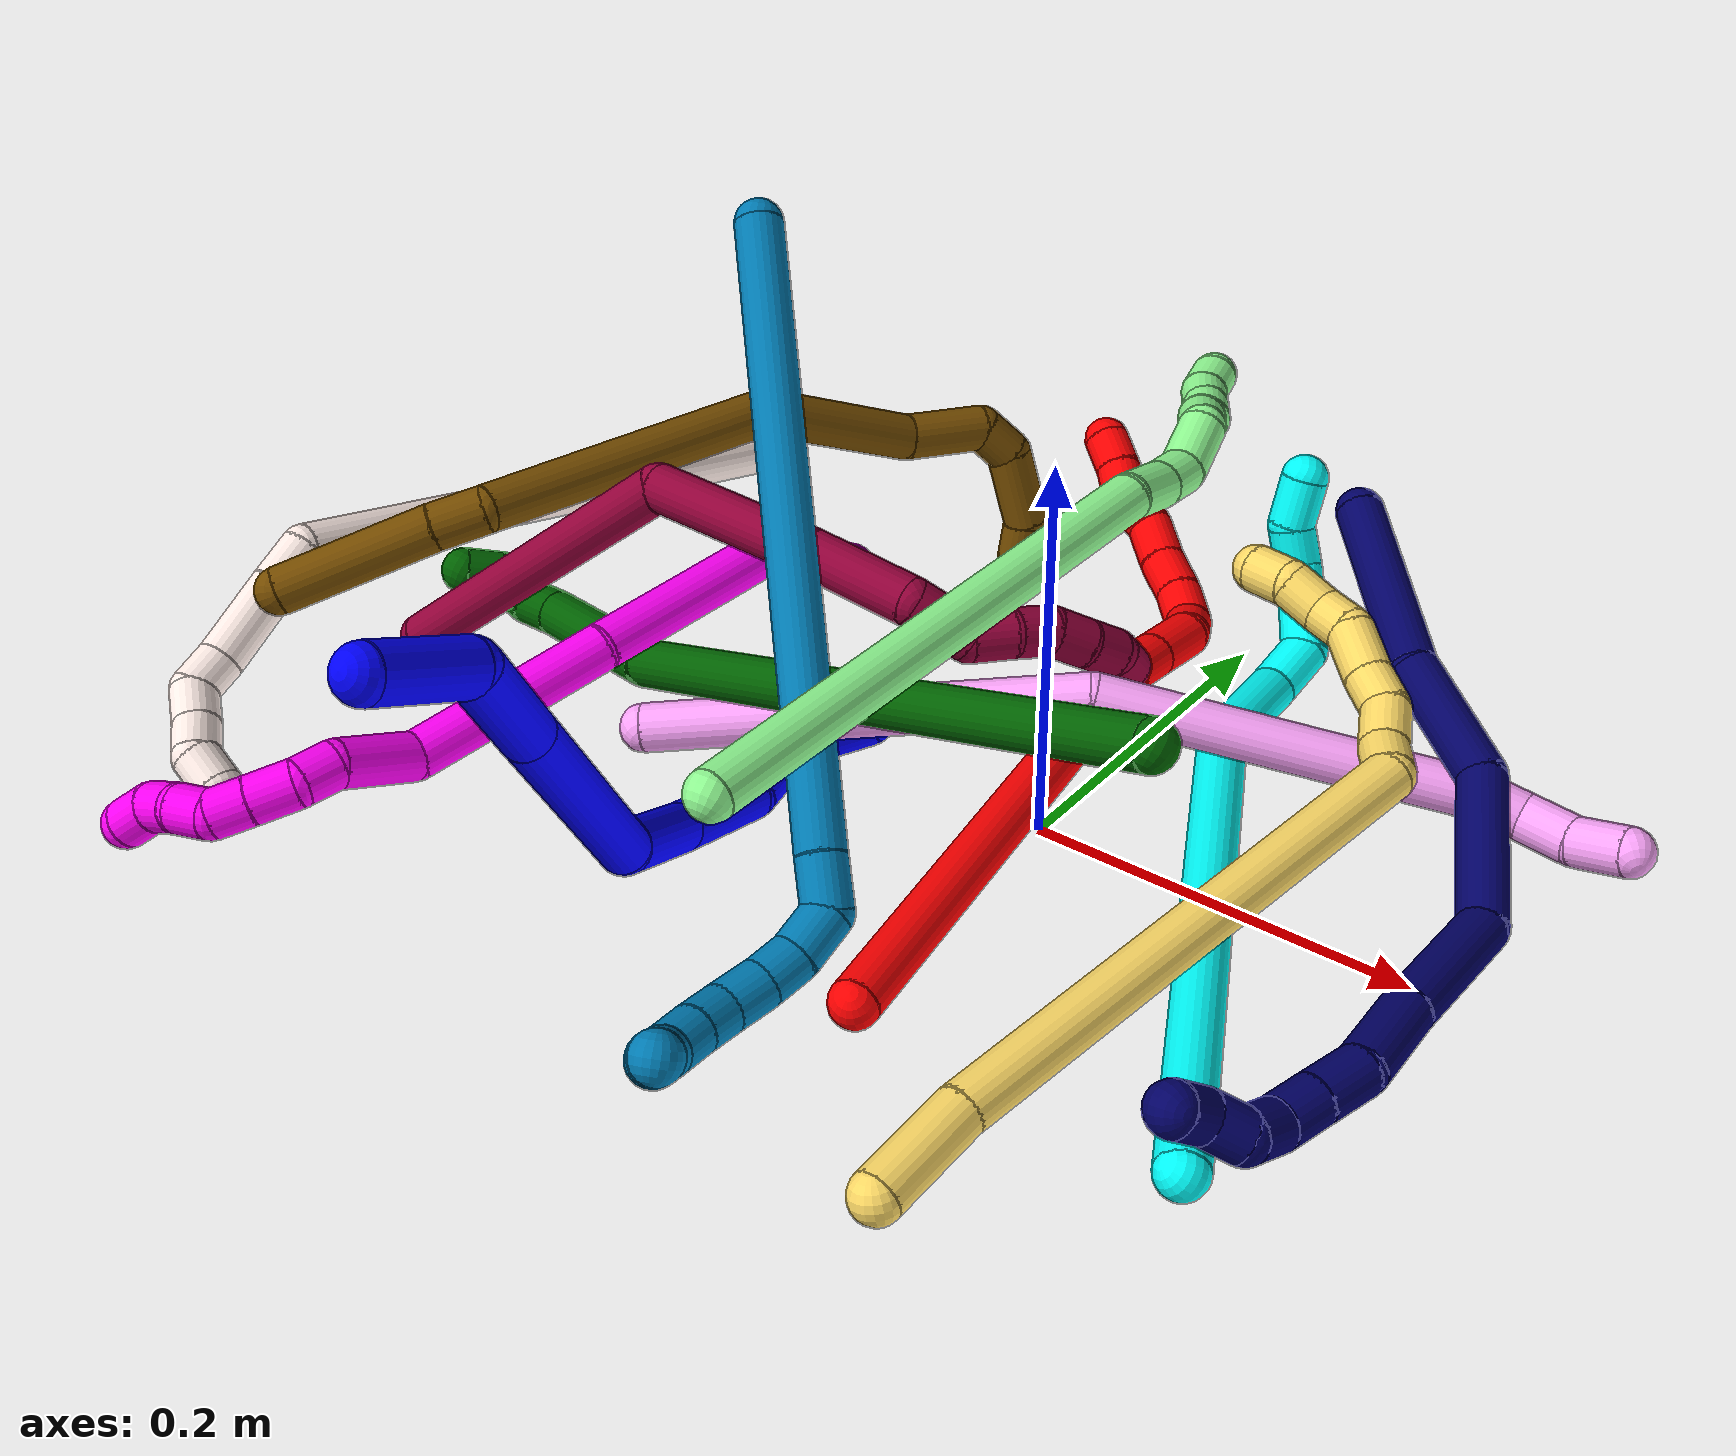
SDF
<sdf version="1.7">
 <world name="default">
  <plugin name="TubeGeneratorPlugin" filename="libtube_generator_plugin.so"/>
  <model name="photoneo_s_sensor">
   <static>1</static>
   <pose>0 0 2 1.57079 1.57079 3.14159</pose>
   <link name="link">
    <inertial><mass>0.1</mass></inertial>
    <sensor name="sensor" type="depth">
     <update_rate>30</update_rate>
     <camera>
      <horizontal_fov>1.22</horizontal_fov>
      <image><width>1920</width><height>1200</height><format>B8G8R8</format></image>
      <clip><near>0.1</near><far>4</far></clip>
      <depth_camera><output>points</output></depth_camera>
     </camera>
     <plugin name="camera_plugin" filename="libgazebo_ros_depth_camera.so">
      <baseline>0.2</baseline>
      <alwaysOn>1</alwaysOn>
      <updateRate>0.0</updateRate>
      <cameraName>camera_ir</cameraName>
      <imageTopicName>/camera/color/image_raw</imageTopicName>
      <cameraInfoTopicName>/camera/color/camera_info</cameraInfoTopicName>
      <depthImageTopicName>/camera/depth/image_raw</depthImageTopicName>
      <depthImageCameraInfoTopicName>/camera/depth/camera_info</depthImageCameraInfoTopicName>
      <pointCloudTopicName>/camera/depth/points</pointCloudTopicName>
      <frameName>fr_optical</frameName>
      <pointCloudCutoff>0.1</pointCloudCutoff>
      <pointCloudCutoffMax>2.0</pointCloudCutoffMax>
      <distortionK1>0</distortionK1>
      <distortionK2>0</distortionK2>
      <distortionK3>0</distortionK3>
      <distortionT1>0</distortionT1>
      <distortionT2>0</distortionT2>
      <CxPrime>0</CxPrime>
      <Cx>0</Cx>
      <Cy>0</Cy>
      <focalLength>0</focalLength>
      <hackBaseline>0</hackBaseline>
     </plugin>
    </sensor>
   </link>
  </model>
  <gravity>0 0 -9.8</gravity>
  <magnetic_field>6e-06 2.3e-05 -4.2e-05</magnetic_field>
  <atmosphere type="adiabatic"/>
  <physics name="default_physics" default="0" type="ode">
   <max_step_size>0.003</max_step_size>
   <real_time_factor>1</real_time_factor>
   <real_time_update_rate>1000</real_time_update_rate>
   <max_contacts>10000</max_contacts>
   <ode>
    <solver>
     <type>quick</type>
     <iters>100</iters>
     <sor>1.3</sor>
     <use_dynamic_moi_rescaling>0</use_dynamic_moi_rescaling>
    </solver>
    <constraints>
     <contact_max_correcting_vel>0</contact_max_correcting_vel>
     <contact_surface_layer>0.001</contact_surface_layer>
     <cfm>0</cfm>
     <erp>0.2</erp>
    </constraints>
   </ode>
  </physics>
  <scene><ambient>0.4 0.4 0.4 1</ambient><background>0.7 0.7 0.7 1</background><shadows>0</shadows></scene>
  <audio><device>default</device></audio>
  <spherical_coordinates>
   <surface_model>EARTH_WGS84</surface_model>
   <latitude_deg>0</latitude_deg>
   <longitude_deg>0</longitude_deg>
   <elevation>0</elevation>
   <heading_deg>0</heading_deg>
  </spherical_coordinates>
  <model name="bin">
   <static>1</static>
   <link name="bottom">
    <collision name="collision-bottom">
     <pose>0 0 -0.01 0 -0 0</pose>
     <geometry><box><size>0.8 0.6 0.02</size></box></geometry>
     <surface>
      <friction><ode><mu>100</mu><mu2>100</mu2></ode></friction>
      <contact><collide_bitmask>65535</collide_bitmask></contact>
     </surface>
    </collision>
   </link>
   <link name="west_wall">
    <collision name="collision-west_wall">
     <pose>-0.41 0 0.1 0 -0 0</pose>
     <geometry><box><size>0.02 0.6 0.2</size></box></geometry>
     <surface>
      <friction><ode><mu>100</mu><mu2>100</mu2></ode></friction>
      <contact><collide_bitmask>65535</collide_bitmask></contact>
     </surface>
    </collision>
   </link>
   <link name="east_wall">
    <collision name="collision-east_wall">
     <pose>0.41 0 0.1 0 -0 0</pose>
     <geometry><box><size>0.02 0.6 0.2</size></box></geometry>
     <surface>
      <friction><ode><mu>100</mu><mu2>100</mu2></ode></friction>
      <contact><collide_bitmask>65535</collide_bitmask></contact>
     </surface>
    </collision>
   </link>
   <link name="south_wall">
    <collision name="collision-south_wall">
     <pose>0 -0.31 0.1 0 -0 0</pose>
     <geometry><box><size>0.8 0.02 0.2</size></box></geometry>
     <surface>
      <friction><ode><mu>100</mu><mu2>100</mu2></ode></friction>
      <contact><collide_bitmask>65535</collide_bitmask></contact>
     </surface>
    </collision>
   </link>
   <link name="north_wall">
    <collision name="collision-north_wall">
     <pose>0 0.31 0.1 0 -0 0</pose>
     <geometry><box><size>0.8 0.02 0.2</size></box></geometry>
     <surface>
      <friction><ode><mu>100</mu><mu2>100</mu2></ode></friction>
      <contact><collide_bitmask>65535</collide_bitmask></contact>
     </surface>
    </collision>
   </link>
  </model>
  <model name="1">
   <static>0</static>
   <link name="1">
    <collision name="collision-cylinder-e_1_1_4">
     <pose>0.003977 0.002781 -0.02539 -3.03252 0.154456 -1.91278</pose>
     <geometry><cylinder><radius>0.0125</radius><length>0.0517</length></cylinder></geometry>
     <surface>
      <friction><ode><mu>1.16</mu><mu2>1.16</mu2><slip1>0</slip1><slip2>0</slip2></ode></friction>
      <contact><ode><kp>1e+06</kp><kd>1</kd><max_vel>0</max_vel><min_depth>0.001</min_depth></ode></contact>
     </surface>
    </collision>
    <visual name="visual-cylinder-e_1_1_4">
     <pose>0.003977 0.002781 -0.02539 -3.03252 0.154456 -1.91278</pose>
     <geometry><cylinder><radius>0.0125</radius><length>0.0517</length></cylinder></geometry>
     <material><ambient>0 0 1 1</ambient></material>
    </visual>
    <collision name="collision-cylinder-e_2_4_5">
     <pose>-0.002866 -0.003747 -0.079622 2.82942 -0.342912 -1.66626</pose>
     <geometry><cylinder><radius>0.0125</radius><length>0.06436</length></cylinder></geometry>
     <surface>
      <friction><ode><mu>1.16</mu><mu2>1.16</mu2><slip1>0</slip1><slip2>0</slip2></ode></friction>
      <contact><ode><kp>1e+06</kp><kd>1</kd><max_vel>0</max_vel><min_depth>0.001</min_depth></ode></contact>
     </surface>
    </collision>
    <visual name="visual-cylinder-e_2_4_5">
     <pose>-0.002866 -0.003747 -0.079622 2.82942 -0.342912 -1.66626</pose>
     <geometry><cylinder><radius>0.0125</radius><length>0.06436</length></cylinder></geometry>
     <material><ambient>0 0 1 1</ambient></material>
    </visual>
    <collision name="collision-cylinder-e_3_5_6">
     <pose>-0.035807 -0.032065 -0.168338 2.83415 -0.338575 -1.66881</pose>
     <geometry><cylinder><radius>0.0125</radius><length>0.133202</length></cylinder></geometry>
     <surface>
      <friction><ode><mu>1.16</mu><mu2>1.16</mu2><slip1>0</slip1><slip2>0</slip2></ode></friction>
      <contact><ode><kp>1e+06</kp><kd>1</kd><max_vel>0</max_vel><min_depth>0.001</min_depth></ode></contact>
     </surface>
    </collision>
    <visual name="visual-cylinder-e_3_5_6">
     <pose>-0.035807 -0.032065 -0.168338 2.83415 -0.338575 -1.66881</pose>
     <geometry><cylinder><radius>0.0125</radius><length>0.133202</length></cylinder></geometry>
     <material><ambient>0 0 1 1</ambient></material>
    </visual>
    <collision name="collision-cylinder-e_4_6_7">
     <pose>-0.071988 -0.043891 -0.269933 -2.97106 -0.320651 2.16913</pose>
     <geometry><cylinder><radius>0.0125</radius><length>0.089216</length></cylinder></geometry>
     <surface>
      <friction><ode><mu>1.16</mu><mu2>1.16</mu2><slip1>0</slip1><slip2>0</slip2></ode></friction>
      <contact><ode><kp>1e+06</kp><kd>1</kd><max_vel>0</max_vel><min_depth>0.001</min_depth></ode></contact>
     </surface>
    </collision>
    <visual name="visual-cylinder-e_4_6_7">
     <pose>-0.071988 -0.043891 -0.269933 -2.97106 -0.320651 2.16913</pose>
     <geometry><cylinder><radius>0.0125</radius><length>0.089216</length></cylinder></geometry>
     <material><ambient>0 0 1 1</ambient></material>
    </visual>
    <collision name="collision-cylinder-e_5_7_8">
     <pose>-0.079728 -0.028432 -0.334743 -2.79749 0.252179 -1.26049</pose>
     <geometry><cylinder><radius>0.0125</radius><length>0.050658</length></cylinder></geometry>
     <surface>
      <friction><ode><mu>1.16</mu><mu2>1.16</mu2><slip1>0</slip1><slip2>0</slip2></ode></friction>
      <contact><ode><kp>1e+06</kp><kd>1</kd><max_vel>0</max_vel><min_depth>0.001</min_depth></ode></contact>
     </surface>
    </collision>
    <visual name="visual-cylinder-e_5_7_8">
     <pose>-0.079728 -0.028432 -0.334743 -2.79749 0.252179 -1.26049</pose>
     <geometry><cylinder><radius>0.0125</radius><length>0.050658</length></cylinder></geometry>
     <material><ambient>0 0 1 1</ambient></material>
    </visual>
    <collision name="collision-cylinder-e_6_8_9">
     <pose>-0.072383 -0.008476 -0.374804 -2.53876 0.049693 -0.159537</pose>
     <geometry><cylinder><radius>0.0125</radius><length>0.041257</length></cylinder></geometry>
     <surface>
      <friction><ode><mu>1.16</mu><mu2>1.16</mu2><slip1>0</slip1><slip2>0</slip2></ode></friction>
      <contact><ode><kp>1e+06</kp><kd>1</kd><max_vel>0</max_vel><min_depth>0.001</min_depth></ode></contact>
     </surface>
    </collision>
    <visual name="visual-cylinder-e_6_8_9">
     <pose>-0.072383 -0.008476 -0.374804 -2.53876 0.049693 -0.159537</pose>
     <geometry><cylinder><radius>0.0125</radius><length>0.041257</length></cylinder></geometry>
     <material><ambient>0 0 1 1</ambient></material>
    </visual>
    <collision name="collision-cylinder-e_7_9_10">
     <pose>-0.066103 0.007045 -0.401252 -2.75662 0.474815 -1.78546</pose>
     <geometry><cylinder><radius>0.0125</radius><length>0.022992</length></cylinder></geometry>
     <surface>
      <friction><ode><mu>1.16</mu><mu2>1.16</mu2><slip1>0</slip1><slip2>0</slip2></ode></friction>
      <contact><ode><kp>1e+06</kp><kd>1</kd><max_vel>0</max_vel><min_depth>0.001</min_depth></ode></contact>
     </surface>
    </collision>
    <visual name="visual-cylinder-e_7_9_10">
     <pose>-0.066103 0.007045 -0.401252 -2.75662 0.474815 -1.78546</pose>
     <geometry><cylinder><radius>0.0125</radius><length>0.022992</length></cylinder></geometry>
     <material><ambient>0 0 1 1</ambient></material>
    </visual>
    <collision name="collision-cylinder-e_8_10_11">
     <pose>-0.052056 0.013554 -0.418265 -2.80122 0.832683 -2.40026</pose>
     <geometry><cylinder><radius>0.0125</radius><length>0.023766</length></cylinder></geometry>
     <surface>
      <friction><ode><mu>1.16</mu><mu2>1.16</mu2><slip1>0</slip1><slip2>0</slip2></ode></friction>
      <contact><ode><kp>1e+06</kp><kd>1</kd><max_vel>0</max_vel><min_depth>0.001</min_depth></ode></contact>
     </surface>
    </collision>
    <visual name="visual-cylinder-e_8_10_11">
     <pose>-0.052056 0.013554 -0.418265 -2.80122 0.832683 -2.40026</pose>
     <geometry><cylinder><radius>0.0125</radius><length>0.023766</length></cylinder></geometry>
     <material><ambient>0 0 1 1</ambient></material>
    </visual>
    <collision name="collision-cylinder-e_9_11_2">
     <pose>-0.033264 0.021732 -0.425426 -1.50248 1.06641 -1.00757</pose>
     <geometry><cylinder><radius>0.0125</radius><length>0.02285</length></cylinder></geometry>
     <surface>
      <friction><ode><mu>1.16</mu><mu2>1.16</mu2><slip1>0</slip1><slip2>0</slip2></ode></friction>
      <contact><ode><kp>1e+06</kp><kd>1</kd><max_vel>0</max_vel><min_depth>0.001</min_depth></ode></contact>
     </surface>
    </collision>
    <visual name="visual-cylinder-e_9_11_2">
     <pose>-0.033264 0.021732 -0.425426 -1.50248 1.06641 -1.00757</pose>
     <geometry><cylinder><radius>0.0125</radius><length>0.02285</length></cylinder></geometry>
     <material><ambient>0 0 1 1</ambient></material>
    </visual>
    <collision name="collision-sphere-2">
     <pose>-0.023262 0.02724 -0.425049 0 -0 0</pose>
     <geometry><sphere><radius>0.0125</radius></sphere></geometry>
     <surface>
      <friction><ode><mu>1.16</mu><mu2>1.16</mu2><slip1>0</slip1><slip2>0</slip2></ode></friction>
      <contact><ode><kp>1e+06</kp><kd>1</kd><max_vel>0</max_vel><min_depth>0.001</min_depth></ode></contact>
     </surface>
    </collision>
    <visual name="visual-sphere-2">
     <pose>-0.023262 0.02724 -0.425049 0 -0 0</pose>
     <geometry><sphere><radius>0.0125</radius></sphere></geometry>
     <material><ambient>0 0 1 1</ambient></material>
    </visual>
    <collision name="collision-sphere-11">
     <pose>-0.043266 0.016223 -0.425803 0 -0 0</pose>
     <geometry><sphere><radius>0.0125</radius></sphere></geometry>
     <surface>
      <friction><ode><mu>1.16</mu><mu2>1.16</mu2><slip1>0</slip1><slip2>0</slip2></ode></friction>
      <contact><ode><kp>1e+06</kp><kd>1</kd><max_vel>0</max_vel><min_depth>0.001</min_depth></ode></contact>
     </surface>
    </collision>
    <visual name="visual-sphere-11">
     <pose>-0.043266 0.016223 -0.425803 0 -0 0</pose>
     <geometry><sphere><radius>0.0125</radius></sphere></geometry>
     <material><ambient>0 0 1 1</ambient></material>
    </visual>
    <collision name="collision-sphere-10">
     <pose>-0.060847 0.010885 -0.410728 0 -0 0</pose>
     <geometry><sphere><radius>0.0125</radius></sphere></geometry>
     <surface>
      <friction><ode><mu>1.16</mu><mu2>1.16</mu2><slip1>0</slip1><slip2>0</slip2></ode></friction>
      <contact><ode><kp>1e+06</kp><kd>1</kd><max_vel>0</max_vel><min_depth>0.001</min_depth></ode></contact>
     </surface>
    </collision>
    <visual name="visual-sphere-10">
     <pose>-0.060847 0.010885 -0.410728 0 -0 0</pose>
     <geometry><sphere><radius>0.0125</radius></sphere></geometry>
     <material><ambient>0 0 1 1</ambient></material>
    </visual>
    <collision name="collision-sphere-9">
     <pose>-0.071358 0.003205 -0.391776 0 -0 0</pose>
     <geometry><sphere><radius>0.0125</radius></sphere></geometry>
     <surface>
      <friction><ode><mu>1.16</mu><mu2>1.16</mu2><slip1>0</slip1><slip2>0</slip2></ode></friction>
      <contact><ode><kp>1e+06</kp><kd>1</kd><max_vel>0</max_vel><min_depth>0.001</min_depth></ode></contact>
     </surface>
    </collision>
    <visual name="visual-sphere-9">
     <pose>-0.071358 0.003205 -0.391776 0 -0 0</pose>
     <geometry><sphere><radius>0.0125</radius></sphere></geometry>
     <material><ambient>0 0 1 1</ambient></material>
    </visual>
    <collision name="collision-sphere-4">
     <pose>0.007954 0.005561 -0.050781 0 -0 0</pose>
     <geometry><sphere><radius>0.0125</radius></sphere></geometry>
     <surface>
      <friction><ode><mu>1.16</mu><mu2>1.16</mu2><slip1>0</slip1><slip2>0</slip2></ode></friction>
      <contact><ode><kp>1e+06</kp><kd>1</kd><max_vel>0</max_vel><min_depth>0.001</min_depth></ode></contact>
     </surface>
    </collision>
    <visual name="visual-sphere-4">
     <pose>0.007954 0.005561 -0.050781 0 -0 0</pose>
     <geometry><sphere><radius>0.0125</radius></sphere></geometry>
     <material><ambient>0 0 1 1</ambient></material>
    </visual>
    <collision name="collision-sphere-1">
     <geometry><sphere><radius>0.0125</radius></sphere></geometry>
     <surface>
      <friction><ode><mu>1.16</mu><mu2>1.16</mu2><slip1>0</slip1><slip2>0</slip2></ode></friction>
      <contact><ode><kp>1e+06</kp><kd>1</kd><max_vel>0</max_vel><min_depth>0.001</min_depth></ode></contact>
     </surface>
    </collision>
    <visual name="visual-sphere-1">
     <geometry><sphere><radius>0.0125</radius></sphere></geometry>
     <material><ambient>0 0 1 1</ambient></material>
    </visual>
    <collision name="collision-sphere-8">
     <pose>-0.073408 -0.020157 -0.357833 0 -0 0</pose>
     <geometry><sphere><radius>0.0125</radius></sphere></geometry>
     <surface>
      <friction><ode><mu>1.16</mu><mu2>1.16</mu2><slip1>0</slip1><slip2>0</slip2></ode></friction>
      <contact><ode><kp>1e+06</kp><kd>1</kd><max_vel>0</max_vel><min_depth>0.001</min_depth></ode></contact>
     </surface>
    </collision>
    <visual name="visual-sphere-8">
     <pose>-0.073408 -0.020157 -0.357833 0 -0 0</pose>
     <geometry><sphere><radius>0.0125</radius></sphere></geometry>
     <material><ambient>0 0 1 1</ambient></material>
    </visual>
    <collision name="collision-sphere-5">
     <pose>-0.013686 -0.013055 -0.108464 0 -0 0</pose>
     <geometry><sphere><radius>0.0125</radius></sphere></geometry>
     <surface>
      <friction><ode><mu>1.16</mu><mu2>1.16</mu2><slip1>0</slip1><slip2>0</slip2></ode></friction>
      <contact><ode><kp>1e+06</kp><kd>1</kd><max_vel>0</max_vel><min_depth>0.001</min_depth></ode></contact>
     </surface>
    </collision>
    <visual name="visual-sphere-5">
     <pose>-0.013686 -0.013055 -0.108464 0 -0 0</pose>
     <geometry><sphere><radius>0.0125</radius></sphere></geometry>
     <material><ambient>0 0 1 1</ambient></material>
    </visual>
    <collision name="collision-sphere-6">
     <pose>-0.057928 -0.051076 -0.228213 0 -0 0</pose>
     <geometry><sphere><radius>0.0125</radius></sphere></geometry>
     <surface>
      <friction><ode><mu>1.16</mu><mu2>1.16</mu2><slip1>0</slip1><slip2>0</slip2></ode></friction>
      <contact><ode><kp>1e+06</kp><kd>1</kd><max_vel>0</max_vel><min_depth>0.001</min_depth></ode></contact>
     </surface>
    </collision>
    <visual name="visual-sphere-6">
     <pose>-0.057928 -0.051076 -0.228213 0 -0 0</pose>
     <geometry><sphere><radius>0.0125</radius></sphere></geometry>
     <material><ambient>0 0 1 1</ambient></material>
    </visual>
    <collision name="collision-sphere-7">
     <pose>-0.086048 -0.036706 -0.311653 0 -0 0</pose>
     <geometry><sphere><radius>0.0125</radius></sphere></geometry>
     <surface>
      <friction><ode><mu>1.16</mu><mu2>1.16</mu2><slip1>0</slip1><slip2>0</slip2></ode></friction>
      <contact><ode><kp>1e+06</kp><kd>1</kd><max_vel>0</max_vel><min_depth>0.001</min_depth></ode></contact>
     </surface>
    </collision>
    <visual name="visual-sphere-7">
     <pose>-0.086048 -0.036706 -0.311653 0 -0 0</pose>
     <geometry><sphere><radius>0.0125</radius></sphere></geometry>
     <material><ambient>0 0 1 1</ambient></material>
    </visual>
    <inertial>
     <pose>-0.043426 -0.018187 -0.2285 0 -0 0</pose>
     <mass>0.5</mass>
     <inertia>
      <ixx>-0.000243</ixx>
      <ixy>0</ixy>
      <ixz>0</ixz>
      <iyy>-0.000109</iyy>
      <iyz>0</iyz>
      <izz>9.5e-05</izz>
     </inertia>
    </inertial>
   </link>
   <pose>-0.066291 -0.350303 0.244291 0.959793 -0.403969 0.263269</pose>
  </model>
  <model name="2">
   <static>0</static>
   <link name="2">
    <collision name="collision-cylinder-e_1_1_4">
     <pose>-0.03202 0.120214 0.07095 -1.03762 -0.225487 0.129117</pose>
     <geometry><cylinder><radius>0.0125</radius><length>0.286429</length></cylinder></geometry>
     <surface>
      <friction><ode><mu>1.16</mu><mu2>1.16</mu2><slip1>0</slip1><slip2>0</slip2></ode></friction>
      <contact><ode><kp>1e+06</kp><kd>1</kd><max_vel>0</max_vel><min_depth>0.001</min_depth></ode></contact>
     </surface>
    </collision>
    <visual name="visual-cylinder-e_1_1_4">
     <pose>-0.03202 0.120214 0.07095 -1.03762 -0.225487 0.129117</pose>
     <geometry><cylinder><radius>0.0125</radius><length>0.286429</length></cylinder></geometry>
     <material><ambient>1 0 0 1</ambient></material>
    </visual>
    <collision name="collision-cylinder-e_2_4_5">
     <pose>-0.068343 0.250228 0.15053 -0.848756 -0.318293 0.144789</pose>
     <geometry><cylinder><radius>0.0125</radius><length>0.0275</length></cylinder></geometry>
     <surface>
      <friction><ode><mu>1.16</mu><mu2>1.16</mu2><slip1>0</slip1><slip2>0</slip2></ode></friction>
      <contact><ode><kp>1e+06</kp><kd>1</kd><max_vel>0</max_vel><min_depth>0.001</min_depth></ode></contact>
     </surface>
    </collision>
    <visual name="visual-cylinder-e_2_4_5">
     <pose>-0.068343 0.250228 0.15053 -0.848756 -0.318293 0.144789</pose>
     <geometry><cylinder><radius>0.0125</radius><length>0.0275</length></cylinder></geometry>
     <material><ambient>1 0 0 1</ambient></material>
    </visual>
    <collision name="collision-cylinder-e_3_5_6">
     <pose>-0.078867 0.272588 0.169424 -0.885742 -0.366256 0.175231</pose>
     <geometry><cylinder><radius>0.0125</radius><length>0.034744</length></cylinder></geometry>
     <surface>
      <friction><ode><mu>1.16</mu><mu2>1.16</mu2><slip1>0</slip1><slip2>0</slip2></ode></friction>
      <contact><ode><kp>1e+06</kp><kd>1</kd><max_vel>0</max_vel><min_depth>0.001</min_depth></ode></contact>
     </surface>
    </collision>
    <visual name="visual-cylinder-e_3_5_6">
     <pose>-0.078867 0.272588 0.169424 -0.885742 -0.366256 0.175231</pose>
     <geometry><cylinder><radius>0.0125</radius><length>0.034744</length></cylinder></geometry>
     <material><ambient>1 0 0 1</ambient></material>
    </visual>
    <collision name="collision-cylinder-e_4_6_7">
     <pose>-0.083955 0.292014 0.186871 -0.762705 0.113574 -0.045582</pose>
     <geometry><cylinder><radius>0.0125</radius><length>0.020005</length></cylinder></geometry>
     <surface>
      <friction><ode><mu>1.16</mu><mu2>1.16</mu2><slip1>0</slip1><slip2>0</slip2></ode></friction>
      <contact><ode><kp>1e+06</kp><kd>1</kd><max_vel>0</max_vel><min_depth>0.001</min_depth></ode></contact>
     </surface>
    </collision>
    <visual name="visual-cylinder-e_4_6_7">
     <pose>-0.083955 0.292014 0.186871 -0.762705 0.113574 -0.045582</pose>
     <geometry><cylinder><radius>0.0125</radius><length>0.020005</length></cylinder></geometry>
     <material><ambient>1 0 0 1</ambient></material>
    </visual>
    <collision name="collision-cylinder-e_5_7_8">
     <pose>-0.078228 0.308446 0.195535 -1.41734 0.44311 -0.381487</pose>
     <geometry><cylinder><radius>0.0125</radius><length>0.021428</length></cylinder></geometry>
     <surface>
      <friction><ode><mu>1.16</mu><mu2>1.16</mu2><slip1>0</slip1><slip2>0</slip2></ode></friction>
      <contact><ode><kp>1e+06</kp><kd>1</kd><max_vel>0</max_vel><min_depth>0.001</min_depth></ode></contact>
     </surface>
    </collision>
    <visual name="visual-cylinder-e_5_7_8">
     <pose>-0.078228 0.308446 0.195535 -1.41734 0.44311 -0.381487</pose>
     <geometry><cylinder><radius>0.0125</radius><length>0.021428</length></cylinder></geometry>
     <material><ambient>1 0 0 1</ambient></material>
    </visual>
    <collision name="collision-cylinder-e_6_8_9">
     <pose>-0.067416 0.327435 0.198404 -1.42444 0.578347 -0.502872</pose>
     <geometry><cylinder><radius>0.0125</radius><length>0.022753</length></cylinder></geometry>
     <surface>
      <friction><ode><mu>1.16</mu><mu2>1.16</mu2><slip1>0</slip1><slip2>0</slip2></ode></friction>
      <contact><ode><kp>1e+06</kp><kd>1</kd><max_vel>0</max_vel><min_depth>0.001</min_depth></ode></contact>
     </surface>
    </collision>
    <visual name="visual-cylinder-e_6_8_9">
     <pose>-0.067416 0.327435 0.198404 -1.42444 0.578347 -0.502872</pose>
     <geometry><cylinder><radius>0.0125</radius><length>0.022753</length></cylinder></geometry>
     <material><ambient>1 0 0 1</ambient></material>
    </visual>
    <collision name="collision-cylinder-e_7_9_10">
     <pose>-0.05523 0.348347 0.201045 -1.4623 0.476676 -0.429148</pose>
     <geometry><cylinder><radius>0.0125</radius><length>0.026011</length></cylinder></geometry>
     <surface>
      <friction><ode><mu>1.16</mu><mu2>1.16</mu2><slip1>0</slip1><slip2>0</slip2></ode></friction>
      <contact><ode><kp>1e+06</kp><kd>1</kd><max_vel>0</max_vel><min_depth>0.001</min_depth></ode></contact>
     </surface>
    </collision>
    <visual name="visual-cylinder-e_7_9_10">
     <pose>-0.05523 0.348347 0.201045 -1.4623 0.476676 -0.429148</pose>
     <geometry><cylinder><radius>0.0125</radius><length>0.026011</length></cylinder></geometry>
     <material><ambient>1 0 0 1</ambient></material>
    </visual>
    <collision name="collision-cylinder-e_8_10_11">
     <pose>-0.041556 0.365752 0.199525 -2.00873 0.867549 -1.25901</pose>
     <geometry><cylinder><radius>0.0125</radius><length>0.020206</length></cylinder></geometry>
     <surface>
      <friction><ode><mu>1.16</mu><mu2>1.16</mu2><slip1>0</slip1><slip2>0</slip2></ode></friction>
      <contact><ode><kp>1e+06</kp><kd>1</kd><max_vel>0</max_vel><min_depth>0.001</min_depth></ode></contact>
     </surface>
    </collision>
    <visual name="visual-cylinder-e_8_10_11">
     <pose>-0.041556 0.365752 0.199525 -2.00873 0.867549 -1.25901</pose>
     <geometry><cylinder><radius>0.0125</radius><length>0.020206</length></cylinder></geometry>
     <material><ambient>1 0 0 1</ambient></material>
    </visual>
    <collision name="collision-cylinder-e_9_11_12">
     <pose>-0.030081 0.380953 0.196838 -1.56183 0.38559 -0.382231</pose>
     <geometry><cylinder><radius>0.0125</radius><length>0.02004</length></cylinder></geometry>
     <surface>
      <friction><ode><mu>1.16</mu><mu2>1.16</mu2><slip1>0</slip1><slip2>0</slip2></ode></friction>
      <contact><ode><kp>1e+06</kp><kd>1</kd><max_vel>0</max_vel><min_depth>0.001</min_depth></ode></contact>
     </surface>
    </collision>
    <visual name="visual-cylinder-e_9_11_12">
     <pose>-0.030081 0.380953 0.196838 -1.56183 0.38559 -0.382231</pose>
     <geometry><cylinder><radius>0.0125</radius><length>0.02004</length></cylinder></geometry>
     <material><ambient>1 0 0 1</ambient></material>
    </visual>
    <collision name="collision-cylinder-e_10_12_2">
     <pose>-0.021087 0.399278 0.1969 -1.57317 0.524136 -0.525326</pose>
     <geometry><cylinder><radius>0.0125</radius><length>0.020885</length></cylinder></geometry>
     <surface>
      <friction><ode><mu>1.16</mu><mu2>1.16</mu2><slip1>0</slip1><slip2>0</slip2></ode></friction>
      <contact><ode><kp>1e+06</kp><kd>1</kd><max_vel>0</max_vel><min_depth>0.001</min_depth></ode></contact>
     </surface>
    </collision>
    <visual name="visual-cylinder-e_10_12_2">
     <pose>-0.021087 0.399278 0.1969 -1.57317 0.524136 -0.525326</pose>
     <geometry><cylinder><radius>0.0125</radius><length>0.020885</length></cylinder></geometry>
     <material><ambient>1 0 0 1</ambient></material>
    </visual>
    <collision name="collision-sphere-2">
     <pose>-0.015861 0.408319 0.196878 0 -0 0</pose>
     <geometry><sphere><radius>0.0125</radius></sphere></geometry>
     <surface>
      <friction><ode><mu>1.16</mu><mu2>1.16</mu2><slip1>0</slip1><slip2>0</slip2></ode></friction>
      <contact><ode><kp>1e+06</kp><kd>1</kd><max_vel>0</max_vel><min_depth>0.001</min_depth></ode></contact>
     </surface>
    </collision>
    <visual name="visual-sphere-2">
     <pose>-0.015861 0.408319 0.196878 0 -0 0</pose>
     <geometry><sphere><radius>0.0125</radius></sphere></geometry>
     <material><ambient>1 0 0 1</ambient></material>
    </visual>
    <collision name="collision-sphere-12">
     <pose>-0.026313 0.390237 0.196921 0 -0 0</pose>
     <geometry><sphere><radius>0.0125</radius></sphere></geometry>
     <surface>
      <friction><ode><mu>1.16</mu><mu2>1.16</mu2><slip1>0</slip1><slip2>0</slip2></ode></friction>
      <contact><ode><kp>1e+06</kp><kd>1</kd><max_vel>0</max_vel><min_depth>0.001</min_depth></ode></contact>
     </surface>
    </collision>
    <visual name="visual-sphere-12">
     <pose>-0.026313 0.390237 0.196921 0 -0 0</pose>
     <geometry><sphere><radius>0.0125</radius></sphere></geometry>
     <material><ambient>1 0 0 1</ambient></material>
    </visual>
    <collision name="collision-sphere-11">
     <pose>-0.03385 0.371669 0.196755 0 -0 0</pose>
     <geometry><sphere><radius>0.0125</radius></sphere></geometry>
     <surface>
      <friction><ode><mu>1.16</mu><mu2>1.16</mu2><slip1>0</slip1><slip2>0</slip2></ode></friction>
      <contact><ode><kp>1e+06</kp><kd>1</kd><max_vel>0</max_vel><min_depth>0.001</min_depth></ode></contact>
     </surface>
    </collision>
    <visual name="visual-sphere-11">
     <pose>-0.03385 0.371669 0.196755 0 -0 0</pose>
     <geometry><sphere><radius>0.0125</radius></sphere></geometry>
     <material><ambient>1 0 0 1</ambient></material>
    </visual>
    <collision name="collision-sphere-10">
     <pose>-0.049262 0.359835 0.202296 0 -0 0</pose>
     <geometry><sphere><radius>0.0125</radius></sphere></geometry>
     <surface>
      <friction><ode><mu>1.16</mu><mu2>1.16</mu2><slip1>0</slip1><slip2>0</slip2></ode></friction>
      <contact><ode><kp>1e+06</kp><kd>1</kd><max_vel>0</max_vel><min_depth>0.001</min_depth></ode></contact>
     </surface>
    </collision>
    <visual name="visual-sphere-10">
     <pose>-0.049262 0.359835 0.202296 0 -0 0</pose>
     <geometry><sphere><radius>0.0125</radius></sphere></geometry>
     <material><ambient>1 0 0 1</ambient></material>
    </visual>
    <collision name="collision-sphere-9">
     <pose>-0.061197 0.33686 0.199793 0 -0 0</pose>
     <geometry><sphere><radius>0.0125</radius></sphere></geometry>
     <surface>
      <friction><ode><mu>1.16</mu><mu2>1.16</mu2><slip1>0</slip1><slip2>0</slip2></ode></friction>
      <contact><ode><kp>1e+06</kp><kd>1</kd><max_vel>0</max_vel><min_depth>0.001</min_depth></ode></contact>
     </surface>
    </collision>
    <visual name="visual-sphere-9">
     <pose>-0.061197 0.33686 0.199793 0 -0 0</pose>
     <geometry><sphere><radius>0.0125</radius></sphere></geometry>
     <material><ambient>1 0 0 1</ambient></material>
    </visual>
    <collision name="collision-sphere-4">
     <pose>-0.06404 0.240427 0.141899 0 -0 0</pose>
     <geometry><sphere><radius>0.0125</radius></sphere></geometry>
     <surface>
      <friction><ode><mu>1.16</mu><mu2>1.16</mu2><slip1>0</slip1><slip2>0</slip2></ode></friction>
      <contact><ode><kp>1e+06</kp><kd>1</kd><max_vel>0</max_vel><min_depth>0.001</min_depth></ode></contact>
     </surface>
    </collision>
    <visual name="visual-sphere-4">
     <pose>-0.06404 0.240427 0.141899 0 -0 0</pose>
     <geometry><sphere><radius>0.0125</radius></sphere></geometry>
     <material><ambient>1 0 0 1</ambient></material>
    </visual>
    <collision name="collision-sphere-1">
     <geometry><sphere><radius>0.0125</radius></sphere></geometry>
     <surface>
      <friction><ode><mu>1.16</mu><mu2>1.16</mu2><slip1>0</slip1><slip2>0</slip2></ode></friction>
      <contact><ode><kp>1e+06</kp><kd>1</kd><max_vel>0</max_vel><min_depth>0.001</min_depth></ode></contact>
     </surface>
    </collision>
    <visual name="visual-sphere-1">
     <geometry><sphere><radius>0.0125</radius></sphere></geometry>
     <material><ambient>1 0 0 1</ambient></material>
    </visual>
    <collision name="collision-sphere-8">
     <pose>-0.073634 0.318011 0.197015 0 -0 0</pose>
     <geometry><sphere><radius>0.0125</radius></sphere></geometry>
     <surface>
      <friction><ode><mu>1.16</mu><mu2>1.16</mu2><slip1>0</slip1><slip2>0</slip2></ode></friction>
      <contact><ode><kp>1e+06</kp><kd>1</kd><max_vel>0</max_vel><min_depth>0.001</min_depth></ode></contact>
     </surface>
    </collision>
    <visual name="visual-sphere-8">
     <pose>-0.073634 0.318011 0.197015 0 -0 0</pose>
     <geometry><sphere><radius>0.0125</radius></sphere></geometry>
     <material><ambient>1 0 0 1</ambient></material>
    </visual>
    <collision name="collision-sphere-5">
     <pose>-0.072646 0.260028 0.159161 0 -0 0</pose>
     <geometry><sphere><radius>0.0125</radius></sphere></geometry>
     <surface>
      <friction><ode><mu>1.16</mu><mu2>1.16</mu2><slip1>0</slip1><slip2>0</slip2></ode></friction>
      <contact><ode><kp>1e+06</kp><kd>1</kd><max_vel>0</max_vel><min_depth>0.001</min_depth></ode></contact>
     </surface>
    </collision>
    <visual name="visual-sphere-5">
     <pose>-0.072646 0.260028 0.159161 0 -0 0</pose>
     <geometry><sphere><radius>0.0125</radius></sphere></geometry>
     <material><ambient>1 0 0 1</ambient></material>
    </visual>
    <collision name="collision-sphere-6">
     <pose>-0.085089 0.285148 0.179686 0 -0 0</pose>
     <geometry><sphere><radius>0.0125</radius></sphere></geometry>
     <surface>
      <friction><ode><mu>1.16</mu><mu2>1.16</mu2><slip1>0</slip1><slip2>0</slip2></ode></friction>
      <contact><ode><kp>1e+06</kp><kd>1</kd><max_vel>0</max_vel><min_depth>0.001</min_depth></ode></contact>
     </surface>
    </collision>
    <visual name="visual-sphere-6">
     <pose>-0.085089 0.285148 0.179686 0 -0 0</pose>
     <geometry><sphere><radius>0.0125</radius></sphere></geometry>
     <material><ambient>1 0 0 1</ambient></material>
    </visual>
    <collision name="collision-sphere-7">
     <pose>-0.082821 0.29888 0.194056 0 -0 0</pose>
     <geometry><sphere><radius>0.0125</radius></sphere></geometry>
     <surface>
      <friction><ode><mu>1.16</mu><mu2>1.16</mu2><slip1>0</slip1><slip2>0</slip2></ode></friction>
      <contact><ode><kp>1e+06</kp><kd>1</kd><max_vel>0</max_vel><min_depth>0.001</min_depth></ode></contact>
     </surface>
    </collision>
    <visual name="visual-sphere-7">
     <pose>-0.082821 0.29888 0.194056 0 -0 0</pose>
     <geometry><sphere><radius>0.0125</radius></sphere></geometry>
     <material><ambient>1 0 0 1</ambient></material>
    </visual>
    <inertial>
     <pose>-0.044 0.20622 0.120217 0 -0 0</pose>
     <mass>0.5</mass>
     <inertia>
      <ixx>0.002162</ixx>
      <ixy>0</ixy>
      <ixz>0</ixz>
      <iyy>0.001327</iyy>
      <iyz>0</iyz>
      <izz>-0.001216</izz>
     </inertia>
    </inertial>
   </link>
   <pose>0.014856 -0.168418 0.011496 2.56928 0.015216 -2.78324</pose>
  </model>
  <model name="3">
   <static>0</static>
   <link name="3">
    <collision name="collision-cylinder-e_1_1_4">
     <pose>-0.077032 0.123366 0.042637 -1.23803 -0.533155 0.384294</pose>
     <geometry><cylinder><radius>0.0125</radius><length>0.303123</length></cylinder></geometry>
     <surface>
      <friction><ode><mu>1.16</mu><mu2>1.16</mu2><slip1>0</slip1><slip2>0</slip2></ode></friction>
      <contact><ode><kp>1e+06</kp><kd>1</kd><max_vel>0</max_vel><min_depth>0.001</min_depth></ode></contact>
     </surface>
    </collision>
    <visual name="visual-cylinder-e_1_1_4">
     <pose>-0.077032 0.123366 0.042637 -1.23803 -0.533155 0.384294</pose>
     <geometry><cylinder><radius>0.0125</radius><length>0.303123</length></cylinder></geometry>
     <material><ambient>0.003922 1 0.996078 1</ambient></material>
    </visual>
    <collision name="collision-cylinder-e_2_4_5">
     <pose>-0.172145 0.267742 0.105692 -0.799721 -0.55296 0.2387</pose>
     <geometry><cylinder><radius>0.0125</radius><length>0.068856</length></cylinder></geometry>
     <surface>
      <friction><ode><mu>1.16</mu><mu2>1.16</mu2><slip1>0</slip1><slip2>0</slip2></ode></friction>
      <contact><ode><kp>1e+06</kp><kd>1</kd><max_vel>0</max_vel><min_depth>0.001</min_depth></ode></contact>
     </surface>
    </collision>
    <visual name="visual-cylinder-e_2_4_5">
     <pose>-0.172145 0.267742 0.105692 -0.799721 -0.55296 0.2387</pose>
     <geometry><cylinder><radius>0.0125</radius><length>0.068856</length></cylinder></geometry>
     <material><ambient>0.003922 1 0.996078 1</ambient></material>
    </visual>
    <collision name="collision-cylinder-e_3_5_6">
     <pose>-0.203274 0.293802 0.13225 -0.688115 -1.02356 0.397214</pose>
     <geometry><cylinder><radius>0.0125</radius><length>0.030556</length></cylinder></geometry>
     <surface>
      <friction><ode><mu>1.16</mu><mu2>1.16</mu2><slip1>0</slip1><slip2>0</slip2></ode></friction>
      <contact><ode><kp>1e+06</kp><kd>1</kd><max_vel>0</max_vel><min_depth>0.001</min_depth></ode></contact>
     </surface>
    </collision>
    <visual name="visual-cylinder-e_3_5_6">
     <pose>-0.203274 0.293802 0.13225 -0.688115 -1.02356 0.397214</pose>
     <geometry><cylinder><radius>0.0125</radius><length>0.030556</length></cylinder></geometry>
     <material><ambient>0.003922 1 0.996078 1</ambient></material>
    </visual>
    <collision name="collision-cylinder-e_4_6_7">
     <pose>-0.226141 0.305661 0.135009 -2.03166 -0.911896 1.33851</pose>
     <geometry><cylinder><radius>0.0125</radius><length>0.02484</length></cylinder></geometry>
     <surface>
      <friction><ode><mu>1.16</mu><mu2>1.16</mu2><slip1>0</slip1><slip2>0</slip2></ode></friction>
      <contact><ode><kp>1e+06</kp><kd>1</kd><max_vel>0</max_vel><min_depth>0.001</min_depth></ode></contact>
     </surface>
    </collision>
    <visual name="visual-cylinder-e_4_6_7">
     <pose>-0.226141 0.305661 0.135009 -2.03166 -0.911896 1.33851</pose>
     <geometry><cylinder><radius>0.0125</radius><length>0.02484</length></cylinder></geometry>
     <material><ambient>0.003922 1 0.996078 1</ambient></material>
    </visual>
    <collision name="collision-cylinder-e_5_7_8">
     <pose>-0.244701 0.319299 0.128554 -1.99376 -0.862483 1.23708</pose>
     <geometry><cylinder><radius>0.0125</radius><length>0.023017</length></cylinder></geometry>
     <surface>
      <friction><ode><mu>1.16</mu><mu2>1.16</mu2><slip1>0</slip1><slip2>0</slip2></ode></friction>
      <contact><ode><kp>1e+06</kp><kd>1</kd><max_vel>0</max_vel><min_depth>0.001</min_depth></ode></contact>
     </surface>
    </collision>
    <visual name="visual-cylinder-e_5_7_8">
     <pose>-0.244701 0.319299 0.128554 -1.99376 -0.862483 1.23708</pose>
     <geometry><cylinder><radius>0.0125</radius><length>0.023017</length></cylinder></geometry>
     <material><ambient>0.003922 1 0.996078 1</ambient></material>
    </visual>
    <collision name="collision-cylinder-e_6_8_9">
     <pose>-0.261446 0.327066 0.117089 -3.03003 -0.75868 2.86325</pose>
     <geometry><cylinder><radius>0.0125</radius><length>0.023271</length></cylinder></geometry>
     <surface>
      <friction><ode><mu>1.16</mu><mu2>1.16</mu2><slip1>0</slip1><slip2>0</slip2></ode></friction>
      <contact><ode><kp>1e+06</kp><kd>1</kd><max_vel>0</max_vel><min_depth>0.001</min_depth></ode></contact>
     </surface>
    </collision>
    <visual name="visual-cylinder-e_6_8_9">
     <pose>-0.261446 0.327066 0.117089 -3.03003 -0.75868 2.86325</pose>
     <geometry><cylinder><radius>0.0125</radius><length>0.023271</length></cylinder></geometry>
     <material><ambient>0.003922 1 0.996078 1</ambient></material>
    </visual>
    <collision name="collision-cylinder-e_7_9_2">
     <pose>-0.281609 0.327087 0.103724 2.95885 -1.17662 -2.8686</pose>
     <geometry><cylinder><radius>0.0125</radius><length>0.026338</length></cylinder></geometry>
     <surface>
      <friction><ode><mu>1.16</mu><mu2>1.16</mu2><slip1>0</slip1><slip2>0</slip2></ode></friction>
      <contact><ode><kp>1e+06</kp><kd>1</kd><max_vel>0</max_vel><min_depth>0.001</min_depth></ode></contact>
     </surface>
    </collision>
    <visual name="visual-cylinder-e_7_9_2">
     <pose>-0.281609 0.327087 0.103724 2.95885 -1.17662 -2.8686</pose>
     <geometry><cylinder><radius>0.0125</radius><length>0.026338</length></cylinder></geometry>
     <material><ambient>0.003922 1 0.996078 1</ambient></material>
    </visual>
    <collision name="collision-sphere-2">
     <pose>-0.293768 0.326168 0.098751 0 -0 0</pose>
     <geometry><sphere><radius>0.0125</radius></sphere></geometry>
     <surface>
      <friction><ode><mu>1.16</mu><mu2>1.16</mu2><slip1>0</slip1><slip2>0</slip2></ode></friction>
      <contact><ode><kp>1e+06</kp><kd>1</kd><max_vel>0</max_vel><min_depth>0.001</min_depth></ode></contact>
     </surface>
    </collision>
    <visual name="visual-sphere-2">
     <pose>-0.293768 0.326168 0.098751 0 -0 0</pose>
     <geometry><sphere><radius>0.0125</radius></sphere></geometry>
     <material><ambient>0.003922 1 0.996078 1</ambient></material>
    </visual>
    <collision name="collision-sphere-9">
     <pose>-0.26945 0.328006 0.108697 0 -0 0</pose>
     <geometry><sphere><radius>0.0125</radius></sphere></geometry>
     <surface>
      <friction><ode><mu>1.16</mu><mu2>1.16</mu2><slip1>0</slip1><slip2>0</slip2></ode></friction>
      <contact><ode><kp>1e+06</kp><kd>1</kd><max_vel>0</max_vel><min_depth>0.001</min_depth></ode></contact>
     </surface>
    </collision>
    <visual name="visual-sphere-9">
     <pose>-0.26945 0.328006 0.108697 0 -0 0</pose>
     <geometry><sphere><radius>0.0125</radius></sphere></geometry>
     <material><ambient>0.003922 1 0.996078 1</ambient></material>
    </visual>
    <collision name="collision-sphere-4">
     <pose>-0.154063 0.246731 0.085274 0 -0 0</pose>
     <geometry><sphere><radius>0.0125</radius></sphere></geometry>
     <surface>
      <friction><ode><mu>1.16</mu><mu2>1.16</mu2><slip1>0</slip1><slip2>0</slip2></ode></friction>
      <contact><ode><kp>1e+06</kp><kd>1</kd><max_vel>0</max_vel><min_depth>0.001</min_depth></ode></contact>
     </surface>
    </collision>
    <visual name="visual-sphere-4">
     <pose>-0.154063 0.246731 0.085274 0 -0 0</pose>
     <geometry><sphere><radius>0.0125</radius></sphere></geometry>
     <material><ambient>0.003922 1 0.996078 1</ambient></material>
    </visual>
    <collision name="collision-sphere-1">
     <geometry><sphere><radius>0.0125</radius></sphere></geometry>
     <surface>
      <friction><ode><mu>1.16</mu><mu2>1.16</mu2><slip1>0</slip1><slip2>0</slip2></ode></friction>
      <contact><ode><kp>1e+06</kp><kd>1</kd><max_vel>0</max_vel><min_depth>0.001</min_depth></ode></contact>
     </surface>
    </collision>
    <visual name="visual-sphere-1">
     <geometry><sphere><radius>0.0125</radius></sphere></geometry>
     <material><ambient>0.003922 1 0.996078 1</ambient></material>
    </visual>
    <collision name="collision-sphere-8">
     <pose>-0.253441 0.326126 0.125481 0 -0 0</pose>
     <geometry><sphere><radius>0.0125</radius></sphere></geometry>
     <surface>
      <friction><ode><mu>1.16</mu><mu2>1.16</mu2><slip1>0</slip1><slip2>0</slip2></ode></friction>
      <contact><ode><kp>1e+06</kp><kd>1</kd><max_vel>0</max_vel><min_depth>0.001</min_depth></ode></contact>
     </surface>
    </collision>
    <visual name="visual-sphere-8">
     <pose>-0.253441 0.326126 0.125481 0 -0 0</pose>
     <geometry><sphere><radius>0.0125</radius></sphere></geometry>
     <material><ambient>0.003922 1 0.996078 1</ambient></material>
    </visual>
    <collision name="collision-sphere-5">
     <pose>-0.190227 0.288753 0.126109 0 -0 0</pose>
     <geometry><sphere><radius>0.0125</radius></sphere></geometry>
     <surface>
      <friction><ode><mu>1.16</mu><mu2>1.16</mu2><slip1>0</slip1><slip2>0</slip2></ode></friction>
      <contact><ode><kp>1e+06</kp><kd>1</kd><max_vel>0</max_vel><min_depth>0.001</min_depth></ode></contact>
     </surface>
    </collision>
    <visual name="visual-sphere-5">
     <pose>-0.190227 0.288753 0.126109 0 -0 0</pose>
     <geometry><sphere><radius>0.0125</radius></sphere></geometry>
     <material><ambient>0.003922 1 0.996078 1</ambient></material>
    </visual>
    <collision name="collision-sphere-6">
     <pose>-0.216321 0.298851 0.13839 0 -0 0</pose>
     <geometry><sphere><radius>0.0125</radius></sphere></geometry>
     <surface>
      <friction><ode><mu>1.16</mu><mu2>1.16</mu2><slip1>0</slip1><slip2>0</slip2></ode></friction>
      <contact><ode><kp>1e+06</kp><kd>1</kd><max_vel>0</max_vel><min_depth>0.001</min_depth></ode></contact>
     </surface>
    </collision>
    <visual name="visual-sphere-6">
     <pose>-0.216321 0.298851 0.13839 0 -0 0</pose>
     <geometry><sphere><radius>0.0125</radius></sphere></geometry>
     <material><ambient>0.003922 1 0.996078 1</ambient></material>
    </visual>
    <collision name="collision-sphere-7">
     <pose>-0.235961 0.312472 0.131627 0 -0 0</pose>
     <geometry><sphere><radius>0.0125</radius></sphere></geometry>
     <surface>
      <friction><ode><mu>1.16</mu><mu2>1.16</mu2><slip1>0</slip1><slip2>0</slip2></ode></friction>
      <contact><ode><kp>1e+06</kp><kd>1</kd><max_vel>0</max_vel><min_depth>0.001</min_depth></ode></contact>
     </surface>
    </collision>
    <visual name="visual-sphere-7">
     <pose>-0.235961 0.312472 0.131627 0 -0 0</pose>
     <geometry><sphere><radius>0.0125</radius></sphere></geometry>
     <material><ambient>0.003922 1 0.996078 1</ambient></material>
    </visual>
    <inertial>
     <pose>-0.13233 0.191951 0.072024 0 -0 0</pose>
     <mass>0.5</mass>
     <inertia>
      <ixx>0.002627</ixx>
      <ixy>0</ixy>
      <ixz>0</ixz>
      <iyy>0.001948</iyy>
      <iyz>0</iyz>
      <izz>-0.000702</izz>
     </inertia>
    </inertial>
   </link>
   <pose>0.183592 -0.172844 0.011495 -2.80998 0.842393 -1.84039</pose>
  </model>
  <model name="4">
   <static>0</static>
   <link name="4">
    <collision name="collision-cylinder-e_1_1_4">
     <pose>0.097656 0.051441 0.02268 -1.15554 1.04845 -0.720994</pose>
     <geometry><cylinder><radius>0.0125</radius><length>0.225364</length></cylinder></geometry>
     <surface>
      <friction><ode><mu>1.16</mu><mu2>1.16</mu2><slip1>0</slip1><slip2>0</slip2></ode></friction>
      <contact><ode><kp>1e+06</kp><kd>1</kd><max_vel>0</max_vel><min_depth>0.001</min_depth></ode></contact>
     </surface>
    </collision>
    <visual name="visual-cylinder-e_1_1_4">
     <pose>0.097656 0.051441 0.02268 -1.15554 1.04845 -0.720994</pose>
     <geometry><cylinder><radius>0.0125</radius><length>0.225364</length></cylinder></geometry>
     <material><ambient>1 0.65098 0.996078 1</ambient></material>
    </visual>
    <collision name="collision-cylinder-e_2_4_5">
     <pose>0.287107 0.113524 0.073319 -0.363725 1.25575 -0.265396</pose>
     <geometry><cylinder><radius>0.0125</radius><length>0.193093</length></cylinder></geometry>
     <surface>
      <friction><ode><mu>1.16</mu><mu2>1.16</mu2><slip1>0</slip1><slip2>0</slip2></ode></friction>
      <contact><ode><kp>1e+06</kp><kd>1</kd><max_vel>0</max_vel><min_depth>0.001</min_depth></ode></contact>
     </surface>
    </collision>
    <visual name="visual-cylinder-e_2_4_5">
     <pose>0.287107 0.113524 0.073319 -0.363725 1.25575 -0.265396</pose>
     <geometry><cylinder><radius>0.0125</radius><length>0.193093</length></cylinder></geometry>
     <material><ambient>1 0.65098 0.996078 1</ambient></material>
    </visual>
    <collision name="collision-cylinder-e_3_5_6">
     <pose>0.38934 0.124321 0.106832 -0.027784 1.0816 -0.016685</pose>
     <geometry><cylinder><radius>0.0125</radius><length>0.02365</length></cylinder></geometry>
     <surface>
      <friction><ode><mu>1.16</mu><mu2>1.16</mu2><slip1>0</slip1><slip2>0</slip2></ode></friction>
      <contact><ode><kp>1e+06</kp><kd>1</kd><max_vel>0</max_vel><min_depth>0.001</min_depth></ode></contact>
     </surface>
    </collision>
    <visual name="visual-cylinder-e_3_5_6">
     <pose>0.38934 0.124321 0.106832 -0.027784 1.0816 -0.016685</pose>
     <geometry><cylinder><radius>0.0125</radius><length>0.02365</length></cylinder></geometry>
     <material><ambient>1 0.65098 0.996078 1</ambient></material>
    </visual>
    <collision name="collision-cylinder-e_4_6_7">
     <pose>0.406697 0.129952 0.124402 -0.427676 0.482661 -0.106796</pose>
     <geometry><cylinder><radius>0.0125</radius><length>0.029815</length></cylinder></geometry>
     <surface>
      <friction><ode><mu>1.16</mu><mu2>1.16</mu2><slip1>0</slip1><slip2>0</slip2></ode></friction>
      <contact><ode><kp>1e+06</kp><kd>1</kd><max_vel>0</max_vel><min_depth>0.001</min_depth></ode></contact>
     </surface>
    </collision>
    <visual name="visual-cylinder-e_4_6_7">
     <pose>0.406697 0.129952 0.124402 -0.427676 0.482661 -0.106796</pose>
     <geometry><cylinder><radius>0.0125</radius><length>0.029815</length></cylinder></geometry>
     <material><ambient>1 0.65098 0.996078 1</ambient></material>
    </visual>
    <collision name="collision-cylinder-e_5_7_2">
     <pose>0.420823 0.143168 0.14565 -0.697599 0.539069 -0.20026</pose>
     <geometry><cylinder><radius>0.0125</radius><length>0.028078</length></cylinder></geometry>
     <surface>
      <friction><ode><mu>1.16</mu><mu2>1.16</mu2><slip1>0</slip1><slip2>0</slip2></ode></friction>
      <contact><ode><kp>1e+06</kp><kd>1</kd><max_vel>0</max_vel><min_depth>0.001</min_depth></ode></contact>
     </surface>
    </collision>
    <visual name="visual-cylinder-e_5_7_2">
     <pose>0.420823 0.143168 0.14565 -0.697599 0.539069 -0.20026</pose>
     <geometry><cylinder><radius>0.0125</radius><length>0.028078</length></cylinder></geometry>
     <material><ambient>1 0.65098 0.996078 1</ambient></material>
    </visual>
    <collision name="collision-sphere-2">
     <pose>0.42803 0.150908 0.154884 0 -0 0</pose>
     <geometry><sphere><radius>0.0125</radius></sphere></geometry>
     <surface>
      <friction><ode><mu>1.16</mu><mu2>1.16</mu2><slip1>0</slip1><slip2>0</slip2></ode></friction>
      <contact><ode><kp>1e+06</kp><kd>1</kd><max_vel>0</max_vel><min_depth>0.001</min_depth></ode></contact>
     </surface>
    </collision>
    <visual name="visual-sphere-2">
     <pose>0.42803 0.150908 0.154884 0 -0 0</pose>
     <geometry><sphere><radius>0.0125</radius></sphere></geometry>
     <material><ambient>1 0.65098 0.996078 1</ambient></material>
    </visual>
    <collision name="collision-sphere-7">
     <pose>0.413616 0.135429 0.136417 0 -0 0</pose>
     <geometry><sphere><radius>0.0125</radius></sphere></geometry>
     <surface>
      <friction><ode><mu>1.16</mu><mu2>1.16</mu2><slip1>0</slip1><slip2>0</slip2></ode></friction>
      <contact><ode><kp>1e+06</kp><kd>1</kd><max_vel>0</max_vel><min_depth>0.001</min_depth></ode></contact>
     </surface>
    </collision>
    <visual name="visual-sphere-7">
     <pose>0.413616 0.135429 0.136417 0 -0 0</pose>
     <geometry><sphere><radius>0.0125</radius></sphere></geometry>
     <material><ambient>1 0.65098 0.996078 1</ambient></material>
    </visual>
    <collision name="collision-sphere-6">
     <pose>0.399778 0.124476 0.112387 0 -0 0</pose>
     <geometry><sphere><radius>0.0125</radius></sphere></geometry>
     <surface>
      <friction><ode><mu>1.16</mu><mu2>1.16</mu2><slip1>0</slip1><slip2>0</slip2></ode></friction>
      <contact><ode><kp>1e+06</kp><kd>1</kd><max_vel>0</max_vel><min_depth>0.001</min_depth></ode></contact>
     </surface>
    </collision>
    <visual name="visual-sphere-6">
     <pose>0.399778 0.124476 0.112387 0 -0 0</pose>
     <geometry><sphere><radius>0.0125</radius></sphere></geometry>
     <material><ambient>1 0.65098 0.996078 1</ambient></material>
    </visual>
    <collision name="collision-sphere-5">
     <pose>0.378902 0.124167 0.101277 0 -0 0</pose>
     <geometry><sphere><radius>0.0125</radius></sphere></geometry>
     <surface>
      <friction><ode><mu>1.16</mu><mu2>1.16</mu2><slip1>0</slip1><slip2>0</slip2></ode></friction>
      <contact><ode><kp>1e+06</kp><kd>1</kd><max_vel>0</max_vel><min_depth>0.001</min_depth></ode></contact>
     </surface>
    </collision>
    <visual name="visual-sphere-5">
     <pose>0.378902 0.124167 0.101277 0 -0 0</pose>
     <geometry><sphere><radius>0.0125</radius></sphere></geometry>
     <material><ambient>1 0.65098 0.996078 1</ambient></material>
    </visual>
    <collision name="collision-sphere-1">
     <geometry><sphere><radius>0.0125</radius></sphere></geometry>
     <surface>
      <friction><ode><mu>1.16</mu><mu2>1.16</mu2><slip1>0</slip1><slip2>0</slip2></ode></friction>
      <contact><ode><kp>1e+06</kp><kd>1</kd><max_vel>0</max_vel><min_depth>0.001</min_depth></ode></contact>
     </surface>
    </collision>
    <visual name="visual-sphere-1">
     <geometry><sphere><radius>0.0125</radius></sphere></geometry>
     <material><ambient>1 0.65098 0.996078 1</ambient></material>
    </visual>
    <collision name="collision-sphere-4">
     <pose>0.195312 0.102881 0.04536 0 -0 0</pose>
     <geometry><sphere><radius>0.0125</radius></sphere></geometry>
     <surface>
      <friction><ode><mu>1.16</mu><mu2>1.16</mu2><slip1>0</slip1><slip2>0</slip2></ode></friction>
      <contact><ode><kp>1e+06</kp><kd>1</kd><max_vel>0</max_vel><min_depth>0.001</min_depth></ode></contact>
     </surface>
    </collision>
    <visual name="visual-sphere-4">
     <pose>0.195312 0.102881 0.04536 0 -0 0</pose>
     <geometry><sphere><radius>0.0125</radius></sphere></geometry>
     <material><ambient>1 0.65098 0.996078 1</ambient></material>
    </visual>
    <inertial>
     <pose>0.221192 0.088696 0.059187 0 -0 0</pose>
     <mass>0.5</mass>
     <inertia>
      <ixx>0.000215</ixx>
      <ixy>0</ixy>
      <ixz>0</ixz>
      <iyy>0.001049</iyy>
      <iyz>0</iyz>
      <izz>-0.001914</izz>
     </inertia>
    </inertial>
   </link>
   <pose>-0.187728 -0.076152 0.025281 1.78438 0.27349 0.83335</pose>
  </model>
  <model name="5">
   <static>0</static>
   <link name="5">
    <collision name="collision-cylinder-e_1_1_4">
     <pose>0.001348 0.026733 0.003616 -1.43634 0.049923 -0.043627</pose>
     <geometry><cylinder><radius>0.0125</radius><length>0.05402</length></cylinder></geometry>
     <surface>
      <friction><ode><mu>1.16</mu><mu2>1.16</mu2><slip1>0</slip1><slip2>0</slip2></ode></friction>
      <contact><ode><kp>1e+06</kp><kd>1</kd><max_vel>0</max_vel><min_depth>0.001</min_depth></ode></contact>
     </surface>
    </collision>
    <visual name="visual-cylinder-e_1_1_4">
     <pose>0.001348 0.026733 0.003616 -1.43634 0.049923 -0.043627</pose>
     <geometry><cylinder><radius>0.0125</radius><length>0.05402</length></cylinder></geometry>
     <material><ambient>1 0.858824 0.4 1</ambient></material>
    </visual>
    <collision name="collision-cylinder-e_2_4_5">
     <pose>0.024564 0.193936 0.018208 -1.49282 0.153975 -0.142454</pose>
     <geometry><cylinder><radius>0.0125</radius><length>0.285169</length></cylinder></geometry>
     <surface>
      <friction><ode><mu>1.16</mu><mu2>1.16</mu2><slip1>0</slip1><slip2>0</slip2></ode></friction>
      <contact><ode><kp>1e+06</kp><kd>1</kd><max_vel>0</max_vel><min_depth>0.001</min_depth></ode></contact>
     </surface>
    </collision>
    <visual name="visual-cylinder-e_2_4_5">
     <pose>0.024564 0.193936 0.018208 -1.49282 0.153975 -0.142454</pose>
     <geometry><cylinder><radius>0.0125</radius><length>0.285169</length></cylinder></geometry>
     <material><ambient>1 0.858824 0.4 1</ambient></material>
    </visual>
    <collision name="collision-cylinder-e_3_5_6">
     <pose>0.039745 0.34376 0.030178 -1.46484 -0.617949 0.559067</pose>
     <geometry><cylinder><radius>0.0125</radius><length>0.023083</length></cylinder></geometry>
     <surface>
      <friction><ode><mu>1.16</mu><mu2>1.16</mu2><slip1>0</slip1><slip2>0</slip2></ode></friction>
      <contact><ode><kp>1e+06</kp><kd>1</kd><max_vel>0</max_vel><min_depth>0.001</min_depth></ode></contact>
     </surface>
    </collision>
    <visual name="visual-cylinder-e_3_5_6">
     <pose>0.039745 0.34376 0.030178 -1.46484 -0.617949 0.559067</pose>
     <geometry><cylinder><radius>0.0125</radius><length>0.023083</length></cylinder></geometry>
     <material><ambient>1 0.858824 0.4 1</ambient></material>
    </visual>
    <collision name="collision-cylinder-e_4_6_7">
     <pose>0.027922 0.364109 0.035602 -1.18782 -0.40884 0.278166</pose>
     <geometry><cylinder><radius>0.0125</radius><length>0.025835</length></cylinder></geometry>
     <surface>
      <friction><ode><mu>1.16</mu><mu2>1.16</mu2><slip1>0</slip1><slip2>0</slip2></ode></friction>
      <contact><ode><kp>1e+06</kp><kd>1</kd><max_vel>0</max_vel><min_depth>0.001</min_depth></ode></contact>
     </surface>
    </collision>
    <visual name="visual-cylinder-e_4_6_7">
     <pose>0.027922 0.364109 0.035602 -1.18782 -0.40884 0.278166</pose>
     <geometry><cylinder><radius>0.0125</radius><length>0.025835</length></cylinder></geometry>
     <material><ambient>1 0.858824 0.4 1</ambient></material>
    </visual>
    <collision name="collision-cylinder-e_5_7_8">
     <pose>0.015484 0.380283 0.044824 -0.824255 -0.802488 0.366774</pose>
     <geometry><cylinder><radius>0.0125</radius><length>0.020311</length></cylinder></geometry>
     <surface>
      <friction><ode><mu>1.16</mu><mu2>1.16</mu2><slip1>0</slip1><slip2>0</slip2></ode></friction>
      <contact><ode><kp>1e+06</kp><kd>1</kd><max_vel>0</max_vel><min_depth>0.001</min_depth></ode></contact>
     </surface>
    </collision>
    <visual name="visual-cylinder-e_5_7_8">
     <pose>0.015484 0.380283 0.044824 -0.824255 -0.802488 0.366774</pose>
     <geometry><cylinder><radius>0.0125</radius><length>0.020311</length></cylinder></geometry>
     <material><ambient>1 0.858824 0.4 1</ambient></material>
    </visual>
    <collision name="collision-cylinder-e_6_8_9">
     <pose>-0.00057 0.39303 0.057131 -0.788868 -0.687242 0.295707</pose>
     <geometry><cylinder><radius>0.0125</radius><length>0.02759</length></cylinder></geometry>
     <surface>
      <friction><ode><mu>1.16</mu><mu2>1.16</mu2><slip1>0</slip1><slip2>0</slip2></ode></friction>
      <contact><ode><kp>1e+06</kp><kd>1</kd><max_vel>0</max_vel><min_depth>0.001</min_depth></ode></contact>
     </surface>
    </collision>
    <visual name="visual-cylinder-e_6_8_9">
     <pose>-0.00057 0.39303 0.057131 -0.788868 -0.687242 0.295707</pose>
     <geometry><cylinder><radius>0.0125</radius><length>0.02759</length></cylinder></geometry>
     <material><ambient>1 0.858824 0.4 1</ambient></material>
    </visual>
    <collision name="collision-cylinder-e_7_9_10">
     <pose>-0.0188 0.403934 0.067019 -0.952422 -1.16286 0.653676</pose>
     <geometry><cylinder><radius>0.0125</radius><length>0.020651</length></cylinder></geometry>
     <surface>
      <friction><ode><mu>1.16</mu><mu2>1.16</mu2><slip1>0</slip1><slip2>0</slip2></ode></friction>
      <contact><ode><kp>1e+06</kp><kd>1</kd><max_vel>0</max_vel><min_depth>0.001</min_depth></ode></contact>
     </surface>
    </collision>
    <visual name="visual-cylinder-e_7_9_10">
     <pose>-0.0188 0.403934 0.067019 -0.952422 -1.16286 0.653676</pose>
     <geometry><cylinder><radius>0.0125</radius><length>0.020651</length></cylinder></geometry>
     <material><ambient>1 0.858824 0.4 1</ambient></material>
    </visual>
    <collision name="collision-cylinder-e_8_10_11">
     <pose>-0.036926 0.40723 0.075559 0.006773 -0.951481 -0.003489</pose>
     <geometry><cylinder><radius>0.0125</radius><length>0.021241</length></cylinder></geometry>
     <surface>
      <friction><ode><mu>1.16</mu><mu2>1.16</mu2><slip1>0</slip1><slip2>0</slip2></ode></friction>
      <contact><ode><kp>1e+06</kp><kd>1</kd><max_vel>0</max_vel><min_depth>0.001</min_depth></ode></contact>
     </surface>
    </collision>
    <visual name="visual-cylinder-e_8_10_11">
     <pose>-0.036926 0.40723 0.075559 0.006773 -0.951481 -0.003489</pose>
     <geometry><cylinder><radius>0.0125</radius><length>0.021241</length></cylinder></geometry>
     <material><ambient>1 0.858824 0.4 1</ambient></material>
    </visual>
    <collision name="collision-cylinder-e_9_11_2">
     <pose>-0.056304 0.409344 0.083242 -0.95692 -1.32982 0.77241</pose>
     <geometry><cylinder><radius>0.0125</radius><length>0.022099</length></cylinder></geometry>
     <surface>
      <friction><ode><mu>1.16</mu><mu2>1.16</mu2><slip1>0</slip1><slip2>0</slip2></ode></friction>
      <contact><ode><kp>1e+06</kp><kd>1</kd><max_vel>0</max_vel><min_depth>0.001</min_depth></ode></contact>
     </surface>
    </collision>
    <visual name="visual-cylinder-e_9_11_2">
     <pose>-0.056304 0.409344 0.083242 -0.95692 -1.32982 0.77241</pose>
     <geometry><cylinder><radius>0.0125</radius><length>0.022099</length></cylinder></geometry>
     <material><ambient>1 0.858824 0.4 1</ambient></material>
    </visual>
    <collision name="collision-sphere-2">
     <pose>-0.067034 0.411499 0.084761 0 -0 0</pose>
     <geometry><sphere><radius>0.0125</radius></sphere></geometry>
     <surface>
      <friction><ode><mu>1.16</mu><mu2>1.16</mu2><slip1>0</slip1><slip2>0</slip2></ode></friction>
      <contact><ode><kp>1e+06</kp><kd>1</kd><max_vel>0</max_vel><min_depth>0.001</min_depth></ode></contact>
     </surface>
    </collision>
    <visual name="visual-sphere-2">
     <pose>-0.067034 0.411499 0.084761 0 -0 0</pose>
     <geometry><sphere><radius>0.0125</radius></sphere></geometry>
     <material><ambient>1 0.858824 0.4 1</ambient></material>
    </visual>
    <collision name="collision-sphere-11">
     <pose>-0.045574 0.407188 0.081723 0 -0 0</pose>
     <geometry><sphere><radius>0.0125</radius></sphere></geometry>
     <surface>
      <friction><ode><mu>1.16</mu><mu2>1.16</mu2><slip1>0</slip1><slip2>0</slip2></ode></friction>
      <contact><ode><kp>1e+06</kp><kd>1</kd><max_vel>0</max_vel><min_depth>0.001</min_depth></ode></contact>
     </surface>
    </collision>
    <visual name="visual-sphere-11">
     <pose>-0.045574 0.407188 0.081723 0 -0 0</pose>
     <geometry><sphere><radius>0.0125</radius></sphere></geometry>
     <material><ambient>1 0.858824 0.4 1</ambient></material>
    </visual>
    <collision name="collision-sphere-10">
     <pose>-0.028278 0.407272 0.069394 0 -0 0</pose>
     <geometry><sphere><radius>0.0125</radius></sphere></geometry>
     <surface>
      <friction><ode><mu>1.16</mu><mu2>1.16</mu2><slip1>0</slip1><slip2>0</slip2></ode></friction>
      <contact><ode><kp>1e+06</kp><kd>1</kd><max_vel>0</max_vel><min_depth>0.001</min_depth></ode></contact>
     </surface>
    </collision>
    <visual name="visual-sphere-10">
     <pose>-0.028278 0.407272 0.069394 0 -0 0</pose>
     <geometry><sphere><radius>0.0125</radius></sphere></geometry>
     <material><ambient>1 0.858824 0.4 1</ambient></material>
    </visual>
    <collision name="collision-sphere-9">
     <pose>-0.009321 0.400596 0.064645 0 -0 0</pose>
     <geometry><sphere><radius>0.0125</radius></sphere></geometry>
     <surface>
      <friction><ode><mu>1.16</mu><mu2>1.16</mu2><slip1>0</slip1><slip2>0</slip2></ode></friction>
      <contact><ode><kp>1e+06</kp><kd>1</kd><max_vel>0</max_vel><min_depth>0.001</min_depth></ode></contact>
     </surface>
    </collision>
    <visual name="visual-sphere-9">
     <pose>-0.009321 0.400596 0.064645 0 -0 0</pose>
     <geometry><sphere><radius>0.0125</radius></sphere></geometry>
     <material><ambient>1 0.858824 0.4 1</ambient></material>
    </visual>
    <collision name="collision-sphere-4">
     <pose>0.002696 0.053466 0.007232 0 -0 0</pose>
     <geometry><sphere><radius>0.0125</radius></sphere></geometry>
     <surface>
      <friction><ode><mu>1.16</mu><mu2>1.16</mu2><slip1>0</slip1><slip2>0</slip2></ode></friction>
      <contact><ode><kp>1e+06</kp><kd>1</kd><max_vel>0</max_vel><min_depth>0.001</min_depth></ode></contact>
     </surface>
    </collision>
    <visual name="visual-sphere-4">
     <pose>0.002696 0.053466 0.007232 0 -0 0</pose>
     <geometry><sphere><radius>0.0125</radius></sphere></geometry>
     <material><ambient>1 0.858824 0.4 1</ambient></material>
    </visual>
    <collision name="collision-sphere-1">
     <geometry><sphere><radius>0.0125</radius></sphere></geometry>
     <surface>
      <friction><ode><mu>1.16</mu><mu2>1.16</mu2><slip1>0</slip1><slip2>0</slip2></ode></friction>
      <contact><ode><kp>1e+06</kp><kd>1</kd><max_vel>0</max_vel><min_depth>0.001</min_depth></ode></contact>
     </surface>
    </collision>
    <visual name="visual-sphere-1">
     <geometry><sphere><radius>0.0125</radius></sphere></geometry>
     <material><ambient>1 0.858824 0.4 1</ambient></material>
    </visual>
    <collision name="collision-sphere-8">
     <pose>0.008182 0.385464 0.049617 0 -0 0</pose>
     <geometry><sphere><radius>0.0125</radius></sphere></geometry>
     <surface>
      <friction><ode><mu>1.16</mu><mu2>1.16</mu2><slip1>0</slip1><slip2>0</slip2></ode></friction>
      <contact><ode><kp>1e+06</kp><kd>1</kd><max_vel>0</max_vel><min_depth>0.001</min_depth></ode></contact>
     </surface>
    </collision>
    <visual name="visual-sphere-8">
     <pose>0.008182 0.385464 0.049617 0 -0 0</pose>
     <geometry><sphere><radius>0.0125</radius></sphere></geometry>
     <material><ambient>1 0.858824 0.4 1</ambient></material>
    </visual>
    <collision name="collision-sphere-5">
     <pose>0.046431 0.334405 0.029183 0 -0 0</pose>
     <geometry><sphere><radius>0.0125</radius></sphere></geometry>
     <surface>
      <friction><ode><mu>1.16</mu><mu2>1.16</mu2><slip1>0</slip1><slip2>0</slip2></ode></friction>
      <contact><ode><kp>1e+06</kp><kd>1</kd><max_vel>0</max_vel><min_depth>0.001</min_depth></ode></contact>
     </surface>
    </collision>
    <visual name="visual-sphere-5">
     <pose>0.046431 0.334405 0.029183 0 -0 0</pose>
     <geometry><sphere><radius>0.0125</radius></sphere></geometry>
     <material><ambient>1 0.858824 0.4 1</ambient></material>
    </visual>
    <collision name="collision-sphere-6">
     <pose>0.033058 0.353114 0.031173 0 -0 0</pose>
     <geometry><sphere><radius>0.0125</radius></sphere></geometry>
     <surface>
      <friction><ode><mu>1.16</mu><mu2>1.16</mu2><slip1>0</slip1><slip2>0</slip2></ode></friction>
      <contact><ode><kp>1e+06</kp><kd>1</kd><max_vel>0</max_vel><min_depth>0.001</min_depth></ode></contact>
     </surface>
    </collision>
    <visual name="visual-sphere-6">
     <pose>0.033058 0.353114 0.031173 0 -0 0</pose>
     <geometry><sphere><radius>0.0125</radius></sphere></geometry>
     <material><ambient>1 0.858824 0.4 1</ambient></material>
    </visual>
    <collision name="collision-sphere-7">
     <pose>0.022787 0.375103 0.040031 0 -0 0</pose>
     <geometry><sphere><radius>0.0125</radius></sphere></geometry>
     <surface>
      <friction><ode><mu>1.16</mu><mu2>1.16</mu2><slip1>0</slip1><slip2>0</slip2></ode></friction>
      <contact><ode><kp>1e+06</kp><kd>1</kd><max_vel>0</max_vel><min_depth>0.001</min_depth></ode></contact>
     </surface>
    </collision>
    <visual name="visual-sphere-7">
     <pose>0.022787 0.375103 0.040031 0 -0 0</pose>
     <geometry><sphere><radius>0.0125</radius></sphere></geometry>
     <material><ambient>1 0.858824 0.4 1</ambient></material>
    </visual>
    <inertial>
     <pose>0.013197 0.237392 0.028638 0 -0 0</pose>
     <mass>0.5</mass>
     <inertia>
      <ixx>0.001649</ixx>
      <ixy>0</ixy>
      <ixz>0</ixz>
      <iyy>-3.4e-05</iyy>
      <iyz>0</iyz>
      <izz>-0.00222</izz>
     </inertia>
    </inertial>
   </link>
   <pose>0.095367 -0.260253 0.014792 0.002257 -0.202093 -0.033275</pose>
  </model>
  <model name="6">
   <static>0</static>
   <link name="6">
    <collision name="collision-cylinder-e_1_1_4">
     <pose>-0.16516 -0.041464 0.025336 1.02231 -1.28466 -0.794623</pose>
     <geometry><cylinder><radius>0.0125</radius><length>0.344319</length></cylinder></geometry>
     <surface>
      <friction><ode><mu>1.16</mu><mu2>1.16</mu2><slip1>0</slip1><slip2>0</slip2></ode></friction>
      <contact><ode><kp>1e+06</kp><kd>1</kd><max_vel>0</max_vel><min_depth>0.001</min_depth></ode></contact>
     </surface>
    </collision>
    <visual name="visual-cylinder-e_1_1_4">
     <pose>-0.16516 -0.041464 0.025336 1.02231 -1.28466 -0.794623</pose>
     <geometry><cylinder><radius>0.0125</radius><length>0.344319</length></cylinder></geometry>
     <material><ambient>0 0.392157 0.003922 1</ambient></material>
    </visual>
    <collision name="collision-cylinder-e_2_4_5">
     <pose>-0.376417 -0.094947 0.047544 1.82542 -1.30764 -1.56197</pose>
     <geometry><cylinder><radius>0.0125</radius><length>0.095482</length></cylinder></geometry>
     <surface>
      <friction><ode><mu>1.16</mu><mu2>1.16</mu2><slip1>0</slip1><slip2>0</slip2></ode></friction>
      <contact><ode><kp>1e+06</kp><kd>1</kd><max_vel>0</max_vel><min_depth>0.001</min_depth></ode></contact>
     </surface>
    </collision>
    <visual name="visual-cylinder-e_2_4_5">
     <pose>-0.376417 -0.094947 0.047544 1.82542 -1.30764 -1.56197</pose>
     <geometry><cylinder><radius>0.0125</radius><length>0.095482</length></cylinder></geometry>
     <material><ambient>0 0.392157 0.003922 1</ambient></material>
    </visual>
    <collision name="collision-cylinder-e_3_5_6">
     <pose>-0.432362 -0.104892 0.044746 -1.41266 -1.36077 1.2086</pose>
     <geometry><cylinder><radius>0.0125</radius><length>0.020139</length></cylinder></geometry>
     <surface>
      <friction><ode><mu>1.16</mu><mu2>1.16</mu2><slip1>0</slip1><slip2>0</slip2></ode></friction>
      <contact><ode><kp>1e+06</kp><kd>1</kd><max_vel>0</max_vel><min_depth>0.001</min_depth></ode></contact>
     </surface>
    </collision>
    <visual name="visual-cylinder-e_3_5_6">
     <pose>-0.432362 -0.104892 0.044746 -1.41266 -1.36077 1.2086</pose>
     <geometry><cylinder><radius>0.0125</radius><length>0.020139</length></cylinder></geometry>
     <material><ambient>0 0.392157 0.003922 1</ambient></material>
    </visual>
    <collision name="collision-cylinder-e_4_6_7">
     <pose>-0.448959 -0.095984 0.042233 -1.96501 -0.739146 1.05221</pose>
     <geometry><cylinder><radius>0.0125</radius><length>0.020035</length></cylinder></geometry>
     <surface>
      <friction><ode><mu>1.16</mu><mu2>1.16</mu2><slip1>0</slip1><slip2>0</slip2></ode></friction>
      <contact><ode><kp>1e+06</kp><kd>1</kd><max_vel>0</max_vel><min_depth>0.001</min_depth></ode></contact>
     </surface>
    </collision>
    <visual name="visual-cylinder-e_4_6_7">
     <pose>-0.448959 -0.095984 0.042233 -1.96501 -0.739146 1.05221</pose>
     <geometry><cylinder><radius>0.0125</radius><length>0.020035</length></cylinder></geometry>
     <material><ambient>0 0.392157 0.003922 1</ambient></material>
    </visual>
    <collision name="collision-cylinder-e_5_7_2">
     <pose>-0.461198 -0.081689 0.043192 -1.09947 -0.580461 0.362002</pose>
     <geometry><cylinder><radius>0.0125</radius><length>0.020025</length></cylinder></geometry>
     <surface>
      <friction><ode><mu>1.16</mu><mu2>1.16</mu2><slip1>0</slip1><slip2>0</slip2></ode></friction>
      <contact><ode><kp>1e+06</kp><kd>1</kd><max_vel>0</max_vel><min_depth>0.001</min_depth></ode></contact>
     </surface>
    </collision>
    <visual name="visual-cylinder-e_5_7_2">
     <pose>-0.461198 -0.081689 0.043192 -1.09947 -0.580461 0.362002</pose>
     <geometry><cylinder><radius>0.0125</radius><length>0.020025</length></cylinder></geometry>
     <material><ambient>0 0.392157 0.003922 1</ambient></material>
    </visual>
    <collision name="collision-sphere-2">
     <pose>-0.466689 -0.074229 0.046994 0 -0 0</pose>
     <geometry><sphere><radius>0.0125</radius></sphere></geometry>
     <surface>
      <friction><ode><mu>1.16</mu><mu2>1.16</mu2><slip1>0</slip1><slip2>0</slip2></ode></friction>
      <contact><ode><kp>1e+06</kp><kd>1</kd><max_vel>0</max_vel><min_depth>0.001</min_depth></ode></contact>
     </surface>
    </collision>
    <visual name="visual-sphere-2">
     <pose>-0.466689 -0.074229 0.046994 0 -0 0</pose>
     <geometry><sphere><radius>0.0125</radius></sphere></geometry>
     <material><ambient>0 0.392157 0.003922 1</ambient></material>
    </visual>
    <collision name="collision-sphere-7">
     <pose>-0.455707 -0.089148 0.03939 0 -0 0</pose>
     <geometry><sphere><radius>0.0125</radius></sphere></geometry>
     <surface>
      <friction><ode><mu>1.16</mu><mu2>1.16</mu2><slip1>0</slip1><slip2>0</slip2></ode></friction>
      <contact><ode><kp>1e+06</kp><kd>1</kd><max_vel>0</max_vel><min_depth>0.001</min_depth></ode></contact>
     </surface>
    </collision>
    <visual name="visual-sphere-7">
     <pose>-0.455707 -0.089148 0.03939 0 -0 0</pose>
     <geometry><sphere><radius>0.0125</radius></sphere></geometry>
     <material><ambient>0 0.392157 0.003922 1</ambient></material>
    </visual>
    <collision name="collision-sphere-6">
     <pose>-0.442211 -0.102819 0.045077 0 -0 0</pose>
     <geometry><sphere><radius>0.0125</radius></sphere></geometry>
     <surface>
      <friction><ode><mu>1.16</mu><mu2>1.16</mu2><slip1>0</slip1><slip2>0</slip2></ode></friction>
      <contact><ode><kp>1e+06</kp><kd>1</kd><max_vel>0</max_vel><min_depth>0.001</min_depth></ode></contact>
     </surface>
    </collision>
    <visual name="visual-sphere-6">
     <pose>-0.442211 -0.102819 0.045077 0 -0 0</pose>
     <geometry><sphere><radius>0.0125</radius></sphere></geometry>
     <material><ambient>0 0.392157 0.003922 1</ambient></material>
    </visual>
    <collision name="collision-sphere-5">
     <pose>-0.422514 -0.106965 0.044416 0 -0 0</pose>
     <geometry><sphere><radius>0.0125</radius></sphere></geometry>
     <surface>
      <friction><ode><mu>1.16</mu><mu2>1.16</mu2><slip1>0</slip1><slip2>0</slip2></ode></friction>
      <contact><ode><kp>1e+06</kp><kd>1</kd><max_vel>0</max_vel><min_depth>0.001</min_depth></ode></contact>
     </surface>
    </collision>
    <visual name="visual-sphere-5">
     <pose>-0.422514 -0.106965 0.044416 0 -0 0</pose>
     <geometry><sphere><radius>0.0125</radius></sphere></geometry>
     <material><ambient>0 0.392157 0.003922 1</ambient></material>
    </visual>
    <collision name="collision-sphere-1">
     <geometry><sphere><radius>0.0125</radius></sphere></geometry>
     <surface>
      <friction><ode><mu>1.16</mu><mu2>1.16</mu2><slip1>0</slip1><slip2>0</slip2></ode></friction>
      <contact><ode><kp>1e+06</kp><kd>1</kd><max_vel>0</max_vel><min_depth>0.001</min_depth></ode></contact>
     </surface>
    </collision>
    <visual name="visual-sphere-1">
     <geometry><sphere><radius>0.0125</radius></sphere></geometry>
     <material><ambient>0 0.392157 0.003922 1</ambient></material>
    </visual>
    <collision name="collision-sphere-4">
     <pose>-0.330319 -0.082929 0.050672 0 -0 0</pose>
     <geometry><sphere><radius>0.0125</radius></sphere></geometry>
     <surface>
      <friction><ode><mu>1.16</mu><mu2>1.16</mu2><slip1>0</slip1><slip2>0</slip2></ode></friction>
      <contact><ode><kp>1e+06</kp><kd>1</kd><max_vel>0</max_vel><min_depth>0.001</min_depth></ode></contact>
     </surface>
    </collision>
    <visual name="visual-sphere-4">
     <pose>-0.330319 -0.082929 0.050672 0 -0 0</pose>
     <geometry><sphere><radius>0.0125</radius></sphere></geometry>
     <material><ambient>0 0.392157 0.003922 1</ambient></material>
    </visual>
    <inertial>
     <pose>-0.239493 -0.058028 0.031751 0 -0 0</pose>
     <mass>0.5</mass>
     <inertia>
      <ixx>-6.5e-05</ixx>
      <ixy>0</ixy>
      <ixz>0</ixz>
      <iyy>0.002605</iyy>
      <iyz>0</iyz>
      <izz>0.004196</izz>
     </inertia>
    </inertial>
   </link>
   <pose>0.108023 -0.088213 0.142291 2.33748 -0.036757 -0.077435</pose>
  </model>
  <model name="7">
   <static>0</static>
   <link name="7">
    <collision name="collision-cylinder-e_1_1_4">
     <pose>0.020679 -0.032017 0.035319 0.736402 0.409294 0.159804</pose>
     <geometry><cylinder><radius>0.0125</radius><length>0.103925</length></cylinder></geometry>
     <surface>
      <friction><ode><mu>1.16</mu><mu2>1.16</mu2><slip1>0</slip1><slip2>0</slip2></ode></friction>
      <contact><ode><kp>1e+06</kp><kd>1</kd><max_vel>0</max_vel><min_depth>0.001</min_depth></ode></contact>
     </surface>
    </collision>
    <visual name="visual-cylinder-e_1_1_4">
     <pose>0.020679 -0.032017 0.035319 0.736402 0.409294 0.159804</pose>
     <geometry><cylinder><radius>0.0125</radius><length>0.103925</length></cylinder></geometry>
     <material><ambient>0.003922 0 0.403922 1</ambient></material>
    </visual>
    <collision name="collision-cylinder-e_2_4_5">
     <pose>0.060095 -0.078182 0.095352 0.519922 0.581942 0.158971</pose>
     <geometry><cylinder><radius>0.0125</radius><length>0.068179</length></cylinder></geometry>
     <surface>
      <friction><ode><mu>1.16</mu><mu2>1.16</mu2><slip1>0</slip1><slip2>0</slip2></ode></friction>
      <contact><ode><kp>1e+06</kp><kd>1</kd><max_vel>0</max_vel><min_depth>0.001</min_depth></ode></contact>
     </surface>
    </collision>
    <visual name="visual-cylinder-e_2_4_5">
     <pose>0.060095 -0.078182 0.095352 0.519922 0.581942 0.158971</pose>
     <geometry><cylinder><radius>0.0125</radius><length>0.068179</length></cylinder></geometry>
     <material><ambient>0.003922 0 0.403922 1</ambient></material>
    </visual>
    <collision name="collision-cylinder-e_3_5_6">
     <pose>0.090747 -0.126552 0.142268 0.995317 0.284159 0.15511</pose>
     <geometry><cylinder><radius>0.0125</radius><length>0.084993</length></cylinder></geometry>
     <surface>
      <friction><ode><mu>1.16</mu><mu2>1.16</mu2><slip1>0</slip1><slip2>0</slip2></ode></friction>
      <contact><ode><kp>1e+06</kp><kd>1</kd><max_vel>0</max_vel><min_depth>0.001</min_depth></ode></contact>
     </surface>
    </collision>
    <visual name="visual-cylinder-e_3_5_6">
     <pose>0.090747 -0.126552 0.142268 0.995317 0.284159 0.15511</pose>
     <geometry><cylinder><radius>0.0125</radius><length>0.084993</length></cylinder></geometry>
     <material><ambient>0.003922 0 0.403922 1</ambient></material>
    </visual>
    <collision name="collision-cylinder-e_4_6_7">
     <pose>0.090193 -0.196139 0.178611 1.19038 -0.316333 -0.215159</pose>
     <geometry><cylinder><radius>0.0125</radius><length>0.080153</length></cylinder></geometry>
     <surface>
      <friction><ode><mu>1.16</mu><mu2>1.16</mu2><slip1>0</slip1><slip2>0</slip2></ode></friction>
      <contact><ode><kp>1e+06</kp><kd>1</kd><max_vel>0</max_vel><min_depth>0.001</min_depth></ode></contact>
     </surface>
    </collision>
    <visual name="visual-cylinder-e_4_6_7">
     <pose>0.090193 -0.196139 0.178611 1.19038 -0.316333 -0.215159</pose>
     <geometry><cylinder><radius>0.0125</radius><length>0.080153</length></cylinder></geometry>
     <material><ambient>0.003922 0 0.403922 1</ambient></material>
    </visual>
    <collision name="collision-cylinder-e_5_7_8">
     <pose>0.071748 -0.252769 0.201458 1.18226 -0.254523 -0.171342</pose>
     <geometry><cylinder><radius>0.0125</radius><length>0.047486</length></cylinder></geometry>
     <surface>
      <friction><ode><mu>1.16</mu><mu2>1.16</mu2><slip1>0</slip1><slip2>0</slip2></ode></friction>
      <contact><ode><kp>1e+06</kp><kd>1</kd><max_vel>0</max_vel><min_depth>0.001</min_depth></ode></contact>
     </surface>
    </collision>
    <visual name="visual-cylinder-e_5_7_8">
     <pose>0.071748 -0.252769 0.201458 1.18226 -0.254523 -0.171342</pose>
     <geometry><cylinder><radius>0.0125</radius><length>0.047486</length></cylinder></geometry>
     <material><ambient>0.003922 0 0.403922 1</ambient></material>
    </visual>
    <collision name="collision-cylinder-e_6_8_9">
     <pose>0.061003 -0.287221 0.211153 1.49583 -0.346027 -0.321458</pose>
     <geometry><cylinder><radius>0.0125</radius><length>0.028113</length></cylinder></geometry>
     <surface>
      <friction><ode><mu>1.16</mu><mu2>1.16</mu2><slip1>0</slip1><slip2>0</slip2></ode></friction>
      <contact><ode><kp>1e+06</kp><kd>1</kd><max_vel>0</max_vel><min_depth>0.001</min_depth></ode></contact>
     </surface>
    </collision>
    <visual name="visual-cylinder-e_6_8_9">
     <pose>0.061003 -0.287221 0.211153 1.49583 -0.346027 -0.321458</pose>
     <geometry><cylinder><radius>0.0125</radius><length>0.028113</length></cylinder></geometry>
     <material><ambient>0.003922 0 0.403922 1</ambient></material>
    </visual>
    <collision name="collision-cylinder-e_7_9_10">
     <pose>0.052329 -0.311411 0.213019 1.49138 -0.340114 -0.314567</pose>
     <geometry><cylinder><radius>0.0125</radius><length>0.023418</length></cylinder></geometry>
     <surface>
      <friction><ode><mu>1.16</mu><mu2>1.16</mu2><slip1>0</slip1><slip2>0</slip2></ode></friction>
      <contact><ode><kp>1e+06</kp><kd>1</kd><max_vel>0</max_vel><min_depth>0.001</min_depth></ode></contact>
     </surface>
    </collision>
    <visual name="visual-cylinder-e_7_9_10">
     <pose>0.052329 -0.311411 0.213019 1.49138 -0.340114 -0.314567</pose>
     <geometry><cylinder><radius>0.0125</radius><length>0.023418</length></cylinder></geometry>
     <material><ambient>0.003922 0 0.403922 1</ambient></material>
    </visual>
    <collision name="collision-cylinder-e_8_10_11">
     <pose>0.041548 -0.331211 0.21753 1.17892 -0.625531 -0.425975</pose>
     <geometry><cylinder><radius>0.0125</radius><length>0.023483</length></cylinder></geometry>
     <surface>
      <friction><ode><mu>1.16</mu><mu2>1.16</mu2><slip1>0</slip1><slip2>0</slip2></ode></friction>
      <contact><ode><kp>1e+06</kp><kd>1</kd><max_vel>0</max_vel><min_depth>0.001</min_depth></ode></contact>
     </surface>
    </collision>
    <visual name="visual-cylinder-e_8_10_11">
     <pose>0.041548 -0.331211 0.21753 1.17892 -0.625531 -0.425975</pose>
     <geometry><cylinder><radius>0.0125</radius><length>0.023483</length></cylinder></geometry>
     <material><ambient>0.003922 0 0.403922 1</ambient></material>
    </visual>
    <collision name="collision-cylinder-e_9_11_12">
     <pose>0.02584 -0.343835 0.218261 2.22 -1.07261 -1.74995</pose>
     <geometry><cylinder><radius>0.0125</radius><length>0.020109</length></cylinder></geometry>
     <surface>
      <friction><ode><mu>1.16</mu><mu2>1.16</mu2><slip1>0</slip1><slip2>0</slip2></ode></friction>
      <contact><ode><kp>1e+06</kp><kd>1</kd><max_vel>0</max_vel><min_depth>0.001</min_depth></ode></contact>
     </surface>
    </collision>
    <visual name="visual-cylinder-e_9_11_12">
     <pose>0.02584 -0.343835 0.218261 2.22 -1.07261 -1.74995</pose>
     <geometry><cylinder><radius>0.0125</radius><length>0.020109</length></cylinder></geometry>
     <material><ambient>0.003922 0 0.403922 1</ambient></material>
    </visual>
    <collision name="collision-cylinder-e_10_12_2">
     <pose>0.008751 -0.353037 0.217443 1.20054 -0.961261 -0.685658</pose>
     <geometry><cylinder><radius>0.0125</radius><length>0.02014</length></cylinder></geometry>
     <surface>
      <friction><ode><mu>1.16</mu><mu2>1.16</mu2><slip1>0</slip1><slip2>0</slip2></ode></friction>
      <contact><ode><kp>1e+06</kp><kd>1</kd><max_vel>0</max_vel><min_depth>0.001</min_depth></ode></contact>
     </surface>
    </collision>
    <visual name="visual-cylinder-e_10_12_2">
     <pose>0.008751 -0.353037 0.217443 1.20054 -0.961261 -0.685658</pose>
     <geometry><cylinder><radius>0.0125</radius><length>0.02014</length></cylinder></geometry>
     <material><ambient>0.003922 0 0.403922 1</ambient></material>
    </visual>
    <collision name="collision-sphere-2">
     <pose>0.000494 -0.358411 0.219529 0 -0 0</pose>
     <geometry><sphere><radius>0.0125</radius></sphere></geometry>
     <surface>
      <friction><ode><mu>1.16</mu><mu2>1.16</mu2><slip1>0</slip1><slip2>0</slip2></ode></friction>
      <contact><ode><kp>1e+06</kp><kd>1</kd><max_vel>0</max_vel><min_depth>0.001</min_depth></ode></contact>
     </surface>
    </collision>
    <visual name="visual-sphere-2">
     <pose>0.000494 -0.358411 0.219529 0 -0 0</pose>
     <geometry><sphere><radius>0.0125</radius></sphere></geometry>
     <material><ambient>0.003922 0 0.403922 1</ambient></material>
    </visual>
    <collision name="collision-sphere-12">
     <pose>0.017008 -0.347662 0.215357 0 -0 0</pose>
     <geometry><sphere><radius>0.0125</radius></sphere></geometry>
     <surface>
      <friction><ode><mu>1.16</mu><mu2>1.16</mu2><slip1>0</slip1><slip2>0</slip2></ode></friction>
      <contact><ode><kp>1e+06</kp><kd>1</kd><max_vel>0</max_vel><min_depth>0.001</min_depth></ode></contact>
     </surface>
    </collision>
    <visual name="visual-sphere-12">
     <pose>0.017008 -0.347662 0.215357 0 -0 0</pose>
     <geometry><sphere><radius>0.0125</radius></sphere></geometry>
     <material><ambient>0.003922 0 0.403922 1</ambient></material>
    </visual>
    <collision name="collision-sphere-11">
     <pose>0.034673 -0.340008 0.221166 0 -0 0</pose>
     <geometry><sphere><radius>0.0125</radius></sphere></geometry>
     <surface>
      <friction><ode><mu>1.16</mu><mu2>1.16</mu2><slip1>0</slip1><slip2>0</slip2></ode></friction>
      <contact><ode><kp>1e+06</kp><kd>1</kd><max_vel>0</max_vel><min_depth>0.001</min_depth></ode></contact>
     </surface>
    </collision>
    <visual name="visual-sphere-11">
     <pose>0.034673 -0.340008 0.221166 0 -0 0</pose>
     <geometry><sphere><radius>0.0125</radius></sphere></geometry>
     <material><ambient>0.003922 0 0.403922 1</ambient></material>
    </visual>
    <collision name="collision-sphere-10">
     <pose>0.048423 -0.322414 0.213895 0 -0 0</pose>
     <geometry><sphere><radius>0.0125</radius></sphere></geometry>
     <surface>
      <friction><ode><mu>1.16</mu><mu2>1.16</mu2><slip1>0</slip1><slip2>0</slip2></ode></friction>
      <contact><ode><kp>1e+06</kp><kd>1</kd><max_vel>0</max_vel><min_depth>0.001</min_depth></ode></contact>
     </surface>
    </collision>
    <visual name="visual-sphere-10">
     <pose>0.048423 -0.322414 0.213895 0 -0 0</pose>
     <geometry><sphere><radius>0.0125</radius></sphere></geometry>
     <material><ambient>0.003922 0 0.403922 1</ambient></material>
    </visual>
    <collision name="collision-sphere-9">
     <pose>0.056235 -0.300407 0.212144 0 -0 0</pose>
     <geometry><sphere><radius>0.0125</radius></sphere></geometry>
     <surface>
      <friction><ode><mu>1.16</mu><mu2>1.16</mu2><slip1>0</slip1><slip2>0</slip2></ode></friction>
      <contact><ode><kp>1e+06</kp><kd>1</kd><max_vel>0</max_vel><min_depth>0.001</min_depth></ode></contact>
     </surface>
    </collision>
    <visual name="visual-sphere-9">
     <pose>0.056235 -0.300407 0.212144 0 -0 0</pose>
     <geometry><sphere><radius>0.0125</radius></sphere></geometry>
     <material><ambient>0.003922 0 0.403922 1</ambient></material>
    </visual>
    <collision name="collision-sphere-4">
     <pose>0.041358 -0.064033 0.070637 0 -0 0</pose>
     <geometry><sphere><radius>0.0125</radius></sphere></geometry>
     <surface>
      <friction><ode><mu>1.16</mu><mu2>1.16</mu2><slip1>0</slip1><slip2>0</slip2></ode></friction>
      <contact><ode><kp>1e+06</kp><kd>1</kd><max_vel>0</max_vel><min_depth>0.001</min_depth></ode></contact>
     </surface>
    </collision>
    <visual name="visual-sphere-4">
     <pose>0.041358 -0.064033 0.070637 0 -0 0</pose>
     <geometry><sphere><radius>0.0125</radius></sphere></geometry>
     <material><ambient>0.003922 0 0.403922 1</ambient></material>
    </visual>
    <collision name="collision-sphere-1">
     <geometry><sphere><radius>0.0125</radius></sphere></geometry>
     <surface>
      <friction><ode><mu>1.16</mu><mu2>1.16</mu2><slip1>0</slip1><slip2>0</slip2></ode></friction>
      <contact><ode><kp>1e+06</kp><kd>1</kd><max_vel>0</max_vel><min_depth>0.001</min_depth></ode></contact>
     </surface>
    </collision>
    <visual name="visual-sphere-1">
     <geometry><sphere><radius>0.0125</radius></sphere></geometry>
     <material><ambient>0.003922 0 0.403922 1</ambient></material>
    </visual>
    <collision name="collision-sphere-8">
     <pose>0.06577 -0.274035 0.210163 0 -0 0</pose>
     <geometry><sphere><radius>0.0125</radius></sphere></geometry>
     <surface>
      <friction><ode><mu>1.16</mu><mu2>1.16</mu2><slip1>0</slip1><slip2>0</slip2></ode></friction>
      <contact><ode><kp>1e+06</kp><kd>1</kd><max_vel>0</max_vel><min_depth>0.001</min_depth></ode></contact>
     </surface>
    </collision>
    <visual name="visual-sphere-8">
     <pose>0.06577 -0.274035 0.210163 0 -0 0</pose>
     <geometry><sphere><radius>0.0125</radius></sphere></geometry>
     <material><ambient>0.003922 0 0.403922 1</ambient></material>
    </visual>
    <collision name="collision-sphere-5">
     <pose>0.078833 -0.09233 0.120067 0 -0 0</pose>
     <geometry><sphere><radius>0.0125</radius></sphere></geometry>
     <surface>
      <friction><ode><mu>1.16</mu><mu2>1.16</mu2><slip1>0</slip1><slip2>0</slip2></ode></friction>
      <contact><ode><kp>1e+06</kp><kd>1</kd><max_vel>0</max_vel><min_depth>0.001</min_depth></ode></contact>
     </surface>
    </collision>
    <visual name="visual-sphere-5">
     <pose>0.078833 -0.09233 0.120067 0 -0 0</pose>
     <geometry><sphere><radius>0.0125</radius></sphere></geometry>
     <material><ambient>0.003922 0 0.403922 1</ambient></material>
    </visual>
    <collision name="collision-sphere-6">
     <pose>0.10266 -0.160774 0.164469 0 -0 0</pose>
     <geometry><sphere><radius>0.0125</radius></sphere></geometry>
     <surface>
      <friction><ode><mu>1.16</mu><mu2>1.16</mu2><slip1>0</slip1><slip2>0</slip2></ode></friction>
      <contact><ode><kp>1e+06</kp><kd>1</kd><max_vel>0</max_vel><min_depth>0.001</min_depth></ode></contact>
     </surface>
    </collision>
    <visual name="visual-sphere-6">
     <pose>0.10266 -0.160774 0.164469 0 -0 0</pose>
     <geometry><sphere><radius>0.0125</radius></sphere></geometry>
     <material><ambient>0.003922 0 0.403922 1</ambient></material>
    </visual>
    <collision name="collision-sphere-7">
     <pose>0.077726 -0.231504 0.192753 0 -0 0</pose>
     <geometry><sphere><radius>0.0125</radius></sphere></geometry>
     <surface>
      <friction><ode><mu>1.16</mu><mu2>1.16</mu2><slip1>0</slip1><slip2>0</slip2></ode></friction>
      <contact><ode><kp>1e+06</kp><kd>1</kd><max_vel>0</max_vel><min_depth>0.001</min_depth></ode></contact>
     </surface>
    </collision>
    <visual name="visual-sphere-7">
     <pose>0.077726 -0.231504 0.192753 0 -0 0</pose>
     <geometry><sphere><radius>0.0125</radius></sphere></geometry>
     <material><ambient>0.003922 0 0.403922 1</ambient></material>
    </visual>
    <inertial>
     <pose>0.058415 -0.168615 0.141895 0 -0 0</pose>
     <mass>0.5</mass>
     <inertia>
      <ixx>0.000235</ixx>
      <ixy>0</ixy>
      <ixz>0</ixz>
      <iyy>0.000145</iyy>
      <iyz>0</iyz>
      <izz>0.000143</izz>
     </inertia>
    </inertial>
   </link>
   <pose>0.049488 0.217411 0.097858 0.781925 1.03188 0.518435</pose>
  </model>
  <model name="8">
   <static>0</static>
   <link name="8">
    <collision name="collision-cylinder-e_1_1_4">
     <pose>0.052071 -0.053715 -0.05172 2.33728 0.609595 1.27368</pose>
     <geometry><cylinder><radius>0.0125</radius><length>0.181898</length></cylinder></geometry>
     <surface>
      <friction><ode><mu>1.16</mu><mu2>1.16</mu2><slip1>0</slip1><slip2>0</slip2></ode></friction>
      <contact><ode><kp>1e+06</kp><kd>1</kd><max_vel>0</max_vel><min_depth>0.001</min_depth></ode></contact>
     </surface>
    </collision>
    <visual name="visual-cylinder-e_1_1_4">
     <pose>0.052071 -0.053715 -0.05172 2.33728 0.609595 1.27368</pose>
     <geometry><cylinder><radius>0.0125</radius><length>0.181898</length></cylinder></geometry>
     <material><ambient>0.584314 0 0.227451 1</ambient></material>
    </visual>
    <collision name="collision-cylinder-e_2_4_5">
     <pose>0.12227 -0.105569 -0.150842 -3.10235 0.364991 -2.92973</pose>
     <geometry><cylinder><radius>0.0125</radius><length>0.101566</length></cylinder></geometry>
     <surface>
      <friction><ode><mu>1.16</mu><mu2>1.16</mu2><slip1>0</slip1><slip2>0</slip2></ode></friction>
      <contact><ode><kp>1e+06</kp><kd>1</kd><max_vel>0</max_vel><min_depth>0.001</min_depth></ode></contact>
     </surface>
    </collision>
    <visual name="visual-cylinder-e_2_4_5">
     <pose>0.12227 -0.105569 -0.150842 -3.10235 0.364991 -2.92973</pose>
     <geometry><cylinder><radius>0.0125</radius><length>0.101566</length></cylinder></geometry>
     <material><ambient>0.584314 0 0.227451 1</ambient></material>
    </visual>
    <collision name="collision-cylinder-e_3_5_6">
     <pose>0.151737 -0.09991 -0.224604 -2.99852 0.402561 -2.4661</pose>
     <geometry><cylinder><radius>0.0125</radius><length>0.057893</length></cylinder></geometry>
     <surface>
      <friction><ode><mu>1.16</mu><mu2>1.16</mu2><slip1>0</slip1><slip2>0</slip2></ode></friction>
      <contact><ode><kp>1e+06</kp><kd>1</kd><max_vel>0</max_vel><min_depth>0.001</min_depth></ode></contact>
     </surface>
    </collision>
    <visual name="visual-cylinder-e_3_5_6">
     <pose>0.151737 -0.09991 -0.224604 -2.99852 0.402561 -2.4661</pose>
     <geometry><cylinder><radius>0.0125</radius><length>0.057893</length></cylinder></geometry>
     <material><ambient>0.584314 0 0.227451 1</ambient></material>
    </visual>
    <collision name="collision-cylinder-e_4_6_7">
     <pose>0.174026 -0.085721 -0.258512 -2.19901 0.705921 -1.25187</pose>
     <geometry><cylinder><radius>0.0125</radius><length>0.033755</length></cylinder></geometry>
     <surface>
      <friction><ode><mu>1.16</mu><mu2>1.16</mu2><slip1>0</slip1><slip2>0</slip2></ode></friction>
      <contact><ode><kp>1e+06</kp><kd>1</kd><max_vel>0</max_vel><min_depth>0.001</min_depth></ode></contact>
     </surface>
    </collision>
    <visual name="visual-cylinder-e_4_6_7">
     <pose>0.174026 -0.085721 -0.258512 -2.19901 0.705921 -1.25187</pose>
     <geometry><cylinder><radius>0.0125</radius><length>0.033755</length></cylinder></geometry>
     <material><ambient>0.584314 0 0.227451 1</ambient></material>
    </visual>
    <collision name="collision-cylinder-e_5_7_8">
     <pose>0.195509 -0.074037 -0.268803 -2.70125 1.29061 -2.56368</pose>
     <geometry><cylinder><radius>0.0125</radius><length>0.021923</length></cylinder></geometry>
     <surface>
      <friction><ode><mu>1.16</mu><mu2>1.16</mu2><slip1>0</slip1><slip2>0</slip2></ode></friction>
      <contact><ode><kp>1e+06</kp><kd>1</kd><max_vel>0</max_vel><min_depth>0.001</min_depth></ode></contact>
     </surface>
    </collision>
    <visual name="visual-cylinder-e_5_7_8">
     <pose>0.195509 -0.074037 -0.268803 -2.70125 1.29061 -2.56368</pose>
     <geometry><cylinder><radius>0.0125</radius><length>0.021923</length></cylinder></geometry>
     <material><ambient>0.584314 0 0.227451 1</ambient></material>
    </visual>
    <collision name="collision-cylinder-e_6_8_9">
     <pose>0.21622 -0.069975 -0.272367 -1.85944 1.29413 -1.58327</pose>
     <geometry><cylinder><radius>0.0125</radius><length>0.021158</length></cylinder></geometry>
     <surface>
      <friction><ode><mu>1.16</mu><mu2>1.16</mu2><slip1>0</slip1><slip2>0</slip2></ode></friction>
      <contact><ode><kp>1e+06</kp><kd>1</kd><max_vel>0</max_vel><min_depth>0.001</min_depth></ode></contact>
     </surface>
    </collision>
    <visual name="visual-cylinder-e_6_8_9">
     <pose>0.21622 -0.069975 -0.272367 -1.85944 1.29413 -1.58327</pose>
     <geometry><cylinder><radius>0.0125</radius><length>0.021158</length></cylinder></geometry>
     <material><ambient>0.584314 0 0.227451 1</ambient></material>
    </visual>
    <collision name="collision-cylinder-e_7_9_10">
     <pose>0.234755 -0.061481 -0.275326 -1.92799 0.939571 -1.26294</pose>
     <geometry><cylinder><radius>0.0125</radius><length>0.020705</length></cylinder></geometry>
     <surface>
      <friction><ode><mu>1.16</mu><mu2>1.16</mu2><slip1>0</slip1><slip2>0</slip2></ode></friction>
      <contact><ode><kp>1e+06</kp><kd>1</kd><max_vel>0</max_vel><min_depth>0.001</min_depth></ode></contact>
     </surface>
    </collision>
    <visual name="visual-cylinder-e_7_9_10">
     <pose>0.234755 -0.061481 -0.275326 -1.92799 0.939571 -1.26294</pose>
     <geometry><cylinder><radius>0.0125</radius><length>0.020705</length></cylinder></geometry>
     <material><ambient>0.584314 0 0.227451 1</ambient></material>
    </visual>
    <collision name="collision-cylinder-e_8_10_11">
     <pose>0.25137 -0.049777 -0.27781 -1.6289 0.943258 -0.99111</pose>
     <geometry><cylinder><radius>0.0125</radius><length>0.020403</length></cylinder></geometry>
     <surface>
      <friction><ode><mu>1.16</mu><mu2>1.16</mu2><slip1>0</slip1><slip2>0</slip2></ode></friction>
      <contact><ode><kp>1e+06</kp><kd>1</kd><max_vel>0</max_vel><min_depth>0.001</min_depth></ode></contact>
     </surface>
    </collision>
    <visual name="visual-cylinder-e_8_10_11">
     <pose>0.25137 -0.049777 -0.27781 -1.6289 0.943258 -0.99111</pose>
     <geometry><cylinder><radius>0.0125</radius><length>0.020403</length></cylinder></geometry>
     <material><ambient>0.584314 0 0.227451 1</ambient></material>
    </visual>
    <collision name="collision-cylinder-e_9_11_12">
     <pose>0.265243 -0.035882 -0.275353 -1.23022 0.589367 -0.422507</pose>
     <geometry><cylinder><radius>0.0125</radius><length>0.020205</length></cylinder></geometry>
     <surface>
      <friction><ode><mu>1.16</mu><mu2>1.16</mu2><slip1>0</slip1><slip2>0</slip2></ode></friction>
      <contact><ode><kp>1e+06</kp><kd>1</kd><max_vel>0</max_vel><min_depth>0.001</min_depth></ode></contact>
     </surface>
    </collision>
    <visual name="visual-cylinder-e_9_11_12">
     <pose>0.265243 -0.035882 -0.275353 -1.23022 0.589367 -0.422507</pose>
     <geometry><cylinder><radius>0.0125</radius><length>0.020205</length></cylinder></geometry>
     <material><ambient>0.584314 0 0.227451 1</ambient></material>
    </visual>
    <collision name="collision-cylinder-e_10_12_2">
     <pose>0.273449 -0.021209 -0.265293 -0.749933 0.25559 -0.101062</pose>
     <geometry><cylinder><radius>0.0125</radius><length>0.020494</length></cylinder></geometry>
     <surface>
      <friction><ode><mu>1.16</mu><mu2>1.16</mu2><slip1>0</slip1><slip2>0</slip2></ode></friction>
      <contact><ode><kp>1e+06</kp><kd>1</kd><max_vel>0</max_vel><min_depth>0.001</min_depth></ode></contact>
     </surface>
    </collision>
    <visual name="visual-cylinder-e_10_12_2">
     <pose>0.273449 -0.021209 -0.265293 -0.749933 0.25559 -0.101062</pose>
     <geometry><cylinder><radius>0.0125</radius><length>0.020494</length></cylinder></geometry>
     <material><ambient>0.584314 0 0.227451 1</ambient></material>
    </visual>
    <collision name="collision-sphere-2">
     <pose>0.27604 -0.014452 -0.258038 0 -0 0</pose>
     <geometry><sphere><radius>0.0125</radius></sphere></geometry>
     <surface>
      <friction><ode><mu>1.16</mu><mu2>1.16</mu2><slip1>0</slip1><slip2>0</slip2></ode></friction>
      <contact><ode><kp>1e+06</kp><kd>1</kd><max_vel>0</max_vel><min_depth>0.001</min_depth></ode></contact>
     </surface>
    </collision>
    <visual name="visual-sphere-2">
     <pose>0.27604 -0.014452 -0.258038 0 -0 0</pose>
     <geometry><sphere><radius>0.0125</radius></sphere></geometry>
     <material><ambient>0.584314 0 0.227451 1</ambient></material>
    </visual>
    <collision name="collision-sphere-12">
     <pose>0.270858 -0.027966 -0.272547 0 -0 0</pose>
     <geometry><sphere><radius>0.0125</radius></sphere></geometry>
     <surface>
      <friction><ode><mu>1.16</mu><mu2>1.16</mu2><slip1>0</slip1><slip2>0</slip2></ode></friction>
      <contact><ode><kp>1e+06</kp><kd>1</kd><max_vel>0</max_vel><min_depth>0.001</min_depth></ode></contact>
     </surface>
    </collision>
    <visual name="visual-sphere-12">
     <pose>0.270858 -0.027966 -0.272547 0 -0 0</pose>
     <geometry><sphere><radius>0.0125</radius></sphere></geometry>
     <material><ambient>0.584314 0 0.227451 1</ambient></material>
    </visual>
    <collision name="collision-sphere-11">
     <pose>0.259628 -0.043798 -0.278158 0 -0 0</pose>
     <geometry><sphere><radius>0.0125</radius></sphere></geometry>
     <surface>
      <friction><ode><mu>1.16</mu><mu2>1.16</mu2><slip1>0</slip1><slip2>0</slip2></ode></friction>
      <contact><ode><kp>1e+06</kp><kd>1</kd><max_vel>0</max_vel><min_depth>0.001</min_depth></ode></contact>
     </surface>
    </collision>
    <visual name="visual-sphere-11">
     <pose>0.259628 -0.043798 -0.278158 0 -0 0</pose>
     <geometry><sphere><radius>0.0125</radius></sphere></geometry>
     <material><ambient>0.584314 0 0.227451 1</ambient></material>
    </visual>
    <collision name="collision-sphere-10">
     <pose>0.243112 -0.055757 -0.277462 0 -0 0</pose>
     <geometry><sphere><radius>0.0125</radius></sphere></geometry>
     <surface>
      <friction><ode><mu>1.16</mu><mu2>1.16</mu2><slip1>0</slip1><slip2>0</slip2></ode></friction>
      <contact><ode><kp>1e+06</kp><kd>1</kd><max_vel>0</max_vel><min_depth>0.001</min_depth></ode></contact>
     </surface>
    </collision>
    <visual name="visual-sphere-10">
     <pose>0.243112 -0.055757 -0.277462 0 -0 0</pose>
     <geometry><sphere><radius>0.0125</radius></sphere></geometry>
     <material><ambient>0.584314 0 0.227451 1</ambient></material>
    </visual>
    <collision name="collision-sphere-9">
     <pose>0.226397 -0.067205 -0.27319 0 -0 0</pose>
     <geometry><sphere><radius>0.0125</radius></sphere></geometry>
     <surface>
      <friction><ode><mu>1.16</mu><mu2>1.16</mu2><slip1>0</slip1><slip2>0</slip2></ode></friction>
      <contact><ode><kp>1e+06</kp><kd>1</kd><max_vel>0</max_vel><min_depth>0.001</min_depth></ode></contact>
     </surface>
    </collision>
    <visual name="visual-sphere-9">
     <pose>0.226397 -0.067205 -0.27319 0 -0 0</pose>
     <geometry><sphere><radius>0.0125</radius></sphere></geometry>
     <material><ambient>0.584314 0 0.227451 1</ambient></material>
    </visual>
    <collision name="collision-sphere-4">
     <pose>0.104143 -0.10743 -0.10344 0 -0 0</pose>
     <geometry><sphere><radius>0.0125</radius></sphere></geometry>
     <surface>
      <friction><ode><mu>1.16</mu><mu2>1.16</mu2><slip1>0</slip1><slip2>0</slip2></ode></friction>
      <contact><ode><kp>1e+06</kp><kd>1</kd><max_vel>0</max_vel><min_depth>0.001</min_depth></ode></contact>
     </surface>
    </collision>
    <visual name="visual-sphere-4">
     <pose>0.104143 -0.10743 -0.10344 0 -0 0</pose>
     <geometry><sphere><radius>0.0125</radius></sphere></geometry>
     <material><ambient>0.584314 0 0.227451 1</ambient></material>
    </visual>
    <collision name="collision-sphere-1">
     <geometry><sphere><radius>0.0125</radius></sphere></geometry>
     <surface>
      <friction><ode><mu>1.16</mu><mu2>1.16</mu2><slip1>0</slip1><slip2>0</slip2></ode></friction>
      <contact><ode><kp>1e+06</kp><kd>1</kd><max_vel>0</max_vel><min_depth>0.001</min_depth></ode></contact>
     </surface>
    </collision>
    <visual name="visual-sphere-1">
     <geometry><sphere><radius>0.0125</radius></sphere></geometry>
     <material><ambient>0.584314 0 0.227451 1</ambient></material>
    </visual>
    <collision name="collision-sphere-8">
     <pose>0.206043 -0.072745 -0.271545 0 -0 0</pose>
     <geometry><sphere><radius>0.0125</radius></sphere></geometry>
     <surface>
      <friction><ode><mu>1.16</mu><mu2>1.16</mu2><slip1>0</slip1><slip2>0</slip2></ode></friction>
      <contact><ode><kp>1e+06</kp><kd>1</kd><max_vel>0</max_vel><min_depth>0.001</min_depth></ode></contact>
     </surface>
    </collision>
    <visual name="visual-sphere-8">
     <pose>0.206043 -0.072745 -0.271545 0 -0 0</pose>
     <geometry><sphere><radius>0.0125</radius></sphere></geometry>
     <material><ambient>0.584314 0 0.227451 1</ambient></material>
    </visual>
    <collision name="collision-sphere-5">
     <pose>0.140396 -0.103708 -0.198243 0 -0 0</pose>
     <geometry><sphere><radius>0.0125</radius></sphere></geometry>
     <surface>
      <friction><ode><mu>1.16</mu><mu2>1.16</mu2><slip1>0</slip1><slip2>0</slip2></ode></friction>
      <contact><ode><kp>1e+06</kp><kd>1</kd><max_vel>0</max_vel><min_depth>0.001</min_depth></ode></contact>
     </surface>
    </collision>
    <visual name="visual-sphere-5">
     <pose>0.140396 -0.103708 -0.198243 0 -0 0</pose>
     <geometry><sphere><radius>0.0125</radius></sphere></geometry>
     <material><ambient>0.584314 0 0.227451 1</ambient></material>
    </visual>
    <collision name="collision-sphere-6">
     <pose>0.163077 -0.096113 -0.250964 0 -0 0</pose>
     <geometry><sphere><radius>0.0125</radius></sphere></geometry>
     <surface>
      <friction><ode><mu>1.16</mu><mu2>1.16</mu2><slip1>0</slip1><slip2>0</slip2></ode></friction>
      <contact><ode><kp>1e+06</kp><kd>1</kd><max_vel>0</max_vel><min_depth>0.001</min_depth></ode></contact>
     </surface>
    </collision>
    <visual name="visual-sphere-6">
     <pose>0.163077 -0.096113 -0.250964 0 -0 0</pose>
     <geometry><sphere><radius>0.0125</radius></sphere></geometry>
     <material><ambient>0.584314 0 0.227451 1</ambient></material>
    </visual>
    <collision name="collision-sphere-7">
     <pose>0.184975 -0.075329 -0.266061 0 -0 0</pose>
     <geometry><sphere><radius>0.0125</radius></sphere></geometry>
     <surface>
      <friction><ode><mu>1.16</mu><mu2>1.16</mu2><slip1>0</slip1><slip2>0</slip2></ode></friction>
      <contact><ode><kp>1e+06</kp><kd>1</kd><max_vel>0</max_vel><min_depth>0.001</min_depth></ode></contact>
     </surface>
    </collision>
    <visual name="visual-sphere-7">
     <pose>0.184975 -0.075329 -0.266061 0 -0 0</pose>
     <geometry><sphere><radius>0.0125</radius></sphere></geometry>
     <material><ambient>0.584314 0 0.227451 1</ambient></material>
    </visual>
    <inertial>
     <pose>0.132725 -0.071445 -0.160964 0 -0 0</pose>
     <mass>0.5</mass>
     <inertia>
      <ixx>0.000415</ixx>
      <ixy>0</ixy>
      <ixz>0</ixz>
      <iyy>0.000573</iyy>
      <iyz>0</iyz>
      <izz>-7.4e-05</izz>
     </inertia>
    </inertial>
   </link>
   <pose>-0.355804 -0.065977 0.011492 -1.56517 -0.072737 1.16616</pose>
  </model>
  <model name="9">
   <static>0</static>
   <link name="9">
    <collision name="collision-cylinder-e_1_1_4">
     <pose>-0.010817 -0.054444 0.152546 0.342811 -0.066684 -0.011547</pose>
     <geometry><cylinder><radius>0.0125</radius><length>0.324662</length></cylinder></geometry>
     <surface>
      <friction><ode><mu>1.16</mu><mu2>1.16</mu2><slip1>0</slip1><slip2>0</slip2></ode></friction>
      <contact><ode><kp>1e+06</kp><kd>1</kd><max_vel>0</max_vel><min_depth>0.001</min_depth></ode></contact>
     </surface>
    </collision>
    <visual name="visual-cylinder-e_1_1_4">
     <pose>-0.010817 -0.054444 0.152546 0.342811 -0.066684 -0.011547</pose>
     <geometry><cylinder><radius>0.0125</radius><length>0.324662</length></cylinder></geometry>
     <material><ambient>0 0.490196 0.709804 1</ambient></material>
    </visual>
    <collision name="collision-cylinder-e_2_4_5">
     <pose>-0.023332 -0.112621 0.317705 0.287713 -0.12837 -0.01862</pose>
     <geometry><cylinder><radius>0.0125</radius><length>0.026528</length></cylinder></geometry>
     <surface>
      <friction><ode><mu>1.16</mu><mu2>1.16</mu2><slip1>0</slip1><slip2>0</slip2></ode></friction>
      <contact><ode><kp>1e+06</kp><kd>1</kd><max_vel>0</max_vel><min_depth>0.001</min_depth></ode></contact>
     </surface>
    </collision>
    <visual name="visual-cylinder-e_2_4_5">
     <pose>-0.023332 -0.112621 0.317705 0.287713 -0.12837 -0.01862</pose>
     <geometry><cylinder><radius>0.0125</radius><length>0.026528</length></cylinder></geometry>
     <material><ambient>0 0.490196 0.709804 1</ambient></material>
    </visual>
    <collision name="collision-cylinder-e_3_5_6">
     <pose>-0.017827 -0.116685 0.340692 0.031928 0.60669 0.009994</pose>
     <geometry><cylinder><radius>0.0125</radius><length>0.025265</length></cylinder></geometry>
     <surface>
      <friction><ode><mu>1.16</mu><mu2>1.16</mu2><slip1>0</slip1><slip2>0</slip2></ode></friction>
      <contact><ode><kp>1e+06</kp><kd>1</kd><max_vel>0</max_vel><min_depth>0.001</min_depth></ode></contact>
     </surface>
    </collision>
    <visual name="visual-cylinder-e_3_5_6">
     <pose>-0.017827 -0.116685 0.340692 0.031928 0.60669 0.009994</pose>
     <geometry><cylinder><radius>0.0125</radius><length>0.025265</length></cylinder></geometry>
     <material><ambient>0 0.490196 0.709804 1</ambient></material>
    </visual>
    <collision name="collision-cylinder-e_4_6_7">
     <pose>-0.002874 -0.117439 0.357773 0.062916 0.856398 0.028725</pose>
     <geometry><cylinder><radius>0.0125</radius><length>0.020518</length></cylinder></geometry>
     <surface>
      <friction><ode><mu>1.16</mu><mu2>1.16</mu2><slip1>0</slip1><slip2>0</slip2></ode></friction>
      <contact><ode><kp>1e+06</kp><kd>1</kd><max_vel>0</max_vel><min_depth>0.001</min_depth></ode></contact>
     </surface>
    </collision>
    <visual name="visual-cylinder-e_4_6_7">
     <pose>-0.002874 -0.117439 0.357773 0.062916 0.856398 0.028725</pose>
     <geometry><cylinder><radius>0.0125</radius><length>0.020518</length></cylinder></geometry>
     <material><ambient>0 0.490196 0.709804 1</ambient></material>
    </visual>
    <collision name="collision-cylinder-e_5_7_8">
     <pose>0.013987 -0.118684 0.370953 0.126415 0.949378 0.065026</pose>
     <geometry><cylinder><radius>0.0125</radius><length>0.02241</length></cylinder></geometry>
     <surface>
      <friction><ode><mu>1.16</mu><mu2>1.16</mu2><slip1>0</slip1><slip2>0</slip2></ode></friction>
      <contact><ode><kp>1e+06</kp><kd>1</kd><max_vel>0</max_vel><min_depth>0.001</min_depth></ode></contact>
     </surface>
    </collision>
    <visual name="visual-cylinder-e_5_7_8">
     <pose>0.013987 -0.118684 0.370953 0.126415 0.949378 0.065026</pose>
     <geometry><cylinder><radius>0.0125</radius><length>0.02241</length></cylinder></geometry>
     <material><ambient>0 0.490196 0.709804 1</ambient></material>
    </visual>
    <collision name="collision-cylinder-e_6_8_9">
     <pose>0.03133 -0.122785 0.382204 0.601266 0.957381 0.319044</pose>
     <geometry><cylinder><radius>0.0125</radius><length>0.020138</length></cylinder></geometry>
     <surface>
      <friction><ode><mu>1.16</mu><mu2>1.16</mu2><slip1>0</slip1><slip2>0</slip2></ode></friction>
      <contact><ode><kp>1e+06</kp><kd>1</kd><max_vel>0</max_vel><min_depth>0.001</min_depth></ode></contact>
     </surface>
    </collision>
    <visual name="visual-cylinder-e_6_8_9">
     <pose>0.03133 -0.122785 0.382204 0.601266 0.957381 0.319044</pose>
     <geometry><cylinder><radius>0.0125</radius><length>0.020138</length></cylinder></geometry>
     <material><ambient>0 0.490196 0.709804 1</ambient></material>
    </visual>
    <collision name="collision-cylinder-e_7_9_10">
     <pose>0.047608 -0.129469 0.392097 0.587358 0.918626 0.296952</pose>
     <geometry><cylinder><radius>0.0125</radius><length>0.020245</length></cylinder></geometry>
     <surface>
      <friction><ode><mu>1.16</mu><mu2>1.16</mu2><slip1>0</slip1><slip2>0</slip2></ode></friction>
      <contact><ode><kp>1e+06</kp><kd>1</kd><max_vel>0</max_vel><min_depth>0.001</min_depth></ode></contact>
     </surface>
    </collision>
    <visual name="visual-cylinder-e_7_9_10">
     <pose>0.047608 -0.129469 0.392097 0.587358 0.918626 0.296952</pose>
     <geometry><cylinder><radius>0.0125</radius><length>0.020245</length></cylinder></geometry>
     <material><ambient>0 0.490196 0.709804 1</ambient></material>
    </visual>
    <collision name="collision-cylinder-e_8_10_11">
     <pose>0.062242 -0.140377 0.398342 1.42115 0.715024 0.622059</pose>
     <geometry><cylinder><radius>0.0125</radius><length>0.020102</length></cylinder></geometry>
     <surface>
      <friction><ode><mu>1.16</mu><mu2>1.16</mu2><slip1>0</slip1><slip2>0</slip2></ode></friction>
      <contact><ode><kp>1e+06</kp><kd>1</kd><max_vel>0</max_vel><min_depth>0.001</min_depth></ode></contact>
     </surface>
    </collision>
    <visual name="visual-cylinder-e_8_10_11">
     <pose>0.062242 -0.140377 0.398342 1.42115 0.715024 0.622059</pose>
     <geometry><cylinder><radius>0.0125</radius><length>0.020102</length></cylinder></geometry>
     <material><ambient>0 0.490196 0.709804 1</ambient></material>
    </visual>
    <collision name="collision-cylinder-e_9_11_2">
     <pose>0.073075 -0.156909 0.398119 1.71976 0.435118 0.502565</pose>
     <geometry><cylinder><radius>0.0125</radius><length>0.020134</length></cylinder></geometry>
     <surface>
      <friction><ode><mu>1.16</mu><mu2>1.16</mu2><slip1>0</slip1><slip2>0</slip2></ode></friction>
      <contact><ode><kp>1e+06</kp><kd>1</kd><max_vel>0</max_vel><min_depth>0.001</min_depth></ode></contact>
     </surface>
    </collision>
    <visual name="visual-cylinder-e_9_11_2">
     <pose>0.073075 -0.156909 0.398119 1.71976 0.435118 0.502565</pose>
     <geometry><cylinder><radius>0.0125</radius><length>0.020134</length></cylinder></geometry>
     <material><ambient>0 0.490196 0.709804 1</ambient></material>
    </visual>
    <collision name="collision-sphere-2">
     <pose>0.077319 -0.165937 0.396764 0 -0 0</pose>
     <geometry><sphere><radius>0.0125</radius></sphere></geometry>
     <surface>
      <friction><ode><mu>1.16</mu><mu2>1.16</mu2><slip1>0</slip1><slip2>0</slip2></ode></friction>
      <contact><ode><kp>1e+06</kp><kd>1</kd><max_vel>0</max_vel><min_depth>0.001</min_depth></ode></contact>
     </surface>
    </collision>
    <visual name="visual-sphere-2">
     <pose>0.077319 -0.165937 0.396764 0 -0 0</pose>
     <geometry><sphere><radius>0.0125</radius></sphere></geometry>
     <material><ambient>0 0.490196 0.709804 1</ambient></material>
    </visual>
    <collision name="collision-sphere-11">
     <pose>0.068832 -0.147882 0.399474 0 -0 0</pose>
     <geometry><sphere><radius>0.0125</radius></sphere></geometry>
     <surface>
      <friction><ode><mu>1.16</mu><mu2>1.16</mu2><slip1>0</slip1><slip2>0</slip2></ode></friction>
      <contact><ode><kp>1e+06</kp><kd>1</kd><max_vel>0</max_vel><min_depth>0.001</min_depth></ode></contact>
     </surface>
    </collision>
    <visual name="visual-sphere-11">
     <pose>0.068832 -0.147882 0.399474 0 -0 0</pose>
     <geometry><sphere><radius>0.0125</radius></sphere></geometry>
     <material><ambient>0 0.490196 0.709804 1</ambient></material>
    </visual>
    <collision name="collision-sphere-10">
     <pose>0.055653 -0.132873 0.397211 0 -0 0</pose>
     <geometry><sphere><radius>0.0125</radius></sphere></geometry>
     <surface>
      <friction><ode><mu>1.16</mu><mu2>1.16</mu2><slip1>0</slip1><slip2>0</slip2></ode></friction>
      <contact><ode><kp>1e+06</kp><kd>1</kd><max_vel>0</max_vel><min_depth>0.001</min_depth></ode></contact>
     </surface>
    </collision>
    <visual name="visual-sphere-10">
     <pose>0.055653 -0.132873 0.397211 0 -0 0</pose>
     <geometry><sphere><radius>0.0125</radius></sphere></geometry>
     <material><ambient>0 0.490196 0.709804 1</ambient></material>
    </visual>
    <collision name="collision-sphere-9">
     <pose>0.039563 -0.126064 0.386983 0 -0 0</pose>
     <geometry><sphere><radius>0.0125</radius></sphere></geometry>
     <surface>
      <friction><ode><mu>1.16</mu><mu2>1.16</mu2><slip1>0</slip1><slip2>0</slip2></ode></friction>
      <contact><ode><kp>1e+06</kp><kd>1</kd><max_vel>0</max_vel><min_depth>0.001</min_depth></ode></contact>
     </surface>
    </collision>
    <visual name="visual-sphere-9">
     <pose>0.039563 -0.126064 0.386983 0 -0 0</pose>
     <geometry><sphere><radius>0.0125</radius></sphere></geometry>
     <material><ambient>0 0.490196 0.709804 1</ambient></material>
    </visual>
    <collision name="collision-sphere-4">
     <pose>-0.021634 -0.108888 0.305091 0 -0 0</pose>
     <geometry><sphere><radius>0.0125</radius></sphere></geometry>
     <surface>
      <friction><ode><mu>1.16</mu><mu2>1.16</mu2><slip1>0</slip1><slip2>0</slip2></ode></friction>
      <contact><ode><kp>1e+06</kp><kd>1</kd><max_vel>0</max_vel><min_depth>0.001</min_depth></ode></contact>
     </surface>
    </collision>
    <visual name="visual-sphere-4">
     <pose>-0.021634 -0.108888 0.305091 0 -0 0</pose>
     <geometry><sphere><radius>0.0125</radius></sphere></geometry>
     <material><ambient>0 0.490196 0.709804 1</ambient></material>
    </visual>
    <collision name="collision-sphere-1">
     <geometry><sphere><radius>0.0125</radius></sphere></geometry>
     <surface>
      <friction><ode><mu>1.16</mu><mu2>1.16</mu2><slip1>0</slip1><slip2>0</slip2></ode></friction>
      <contact><ode><kp>1e+06</kp><kd>1</kd><max_vel>0</max_vel><min_depth>0.001</min_depth></ode></contact>
     </surface>
    </collision>
    <visual name="visual-sphere-1">
     <geometry><sphere><radius>0.0125</radius></sphere></geometry>
     <material><ambient>0 0.490196 0.709804 1</ambient></material>
    </visual>
    <collision name="collision-sphere-8">
     <pose>0.023097 -0.119506 0.377424 0 -0 0</pose>
     <geometry><sphere><radius>0.0125</radius></sphere></geometry>
     <surface>
      <friction><ode><mu>1.16</mu><mu2>1.16</mu2><slip1>0</slip1><slip2>0</slip2></ode></friction>
      <contact><ode><kp>1e+06</kp><kd>1</kd><max_vel>0</max_vel><min_depth>0.001</min_depth></ode></contact>
     </surface>
    </collision>
    <visual name="visual-sphere-8">
     <pose>0.023097 -0.119506 0.377424 0 -0 0</pose>
     <geometry><sphere><radius>0.0125</radius></sphere></geometry>
     <material><ambient>0 0.490196 0.709804 1</ambient></material>
    </visual>
    <collision name="collision-sphere-5">
     <pose>-0.02503 -0.116354 0.33032 0 -0 0</pose>
     <geometry><sphere><radius>0.0125</radius></sphere></geometry>
     <surface>
      <friction><ode><mu>1.16</mu><mu2>1.16</mu2><slip1>0</slip1><slip2>0</slip2></ode></friction>
      <contact><ode><kp>1e+06</kp><kd>1</kd><max_vel>0</max_vel><min_depth>0.001</min_depth></ode></contact>
     </surface>
    </collision>
    <visual name="visual-sphere-5">
     <pose>-0.02503 -0.116354 0.33032 0 -0 0</pose>
     <geometry><sphere><radius>0.0125</radius></sphere></geometry>
     <material><ambient>0 0.490196 0.709804 1</ambient></material>
    </visual>
    <collision name="collision-sphere-6">
     <pose>-0.010625 -0.117016 0.351065 0 -0 0</pose>
     <geometry><sphere><radius>0.0125</radius></sphere></geometry>
     <surface>
      <friction><ode><mu>1.16</mu><mu2>1.16</mu2><slip1>0</slip1><slip2>0</slip2></ode></friction>
      <contact><ode><kp>1e+06</kp><kd>1</kd><max_vel>0</max_vel><min_depth>0.001</min_depth></ode></contact>
     </surface>
    </collision>
    <visual name="visual-sphere-6">
     <pose>-0.010625 -0.117016 0.351065 0 -0 0</pose>
     <geometry><sphere><radius>0.0125</radius></sphere></geometry>
     <material><ambient>0 0.490196 0.709804 1</ambient></material>
    </visual>
    <collision name="collision-sphere-7">
     <pose>0.004877 -0.117861 0.364481 0 -0 0</pose>
     <geometry><sphere><radius>0.0125</radius></sphere></geometry>
     <surface>
      <friction><ode><mu>1.16</mu><mu2>1.16</mu2><slip1>0</slip1><slip2>0</slip2></ode></friction>
      <contact><ode><kp>1e+06</kp><kd>1</kd><max_vel>0</max_vel><min_depth>0.001</min_depth></ode></contact>
     </surface>
    </collision>
    <visual name="visual-sphere-7">
     <pose>0.004877 -0.117861 0.364481 0 -0 0</pose>
     <geometry><sphere><radius>0.0125</radius></sphere></geometry>
     <material><ambient>0 0.490196 0.709804 1</ambient></material>
    </visual>
    <inertial>
     <pose>-1.9e-05 -0.079511 0.227745 0 -0 0</pose>
     <mass>0.5</mass>
     <inertia>
      <ixx>0.002843</ixx>
      <ixy>0</ixy>
      <ixz>0</ixz>
      <iyy>0.002666</iyy>
      <iyz>0</iyz>
      <izz>0.001179</izz>
     </inertia>
    </inertial>
   </link>
   <pose>-0.213834 0.055012 0.244782 -2.62033 -0.433724 -2.09554</pose>
  </model>
  <model name="10">
   <static>0</static>
   <link name="10">
    <collision name="collision-cylinder-e_1_1_4">
     <pose>0.032961 -0.042865 0.001409 1.53794 0.655255 0.635488</pose>
     <geometry><cylinder><radius>0.0125</radius><length>0.108181</length></cylinder></geometry>
     <surface>
      <friction><ode><mu>1.16</mu><mu2>1.16</mu2><slip1>0</slip1><slip2>0</slip2></ode></friction>
      <contact><ode><kp>1e+06</kp><kd>1</kd><max_vel>0</max_vel><min_depth>0.001</min_depth></ode></contact>
     </surface>
    </collision>
    <visual name="visual-cylinder-e_1_1_4">
     <pose>0.032961 -0.042865 0.001409 1.53794 0.655255 0.635488</pose>
     <geometry><cylinder><radius>0.0125</radius><length>0.108181</length></cylinder></geometry>
     <material><ambient>1 0 0.964706 1</ambient></material>
    </visual>
    <collision name="collision-cylinder-e_2_4_5">
     <pose>0.064775 -0.139032 0.023569 1.19955 -0.020043 -0.013706</pose>
     <geometry><cylinder><radius>0.0125</radius><length>0.114421</length></cylinder></geometry>
     <surface>
      <friction><ode><mu>1.16</mu><mu2>1.16</mu2><slip1>0</slip1><slip2>0</slip2></ode></friction>
      <contact><ode><kp>1e+06</kp><kd>1</kd><max_vel>0</max_vel><min_depth>0.001</min_depth></ode></contact>
     </surface>
    </collision>
    <visual name="visual-cylinder-e_2_4_5">
     <pose>0.064775 -0.139032 0.023569 1.19955 -0.020043 -0.013706</pose>
     <geometry><cylinder><radius>0.0125</radius><length>0.114421</length></cylinder></geometry>
     <material><ambient>1 0 0.964706 1</ambient></material>
    </visual>
    <collision name="collision-cylinder-e_3_5_6">
     <pose>0.055499 -0.239322 0.070753 1.05836 -0.149661 -0.087631</pose>
     <geometry><cylinder><radius>0.0125</radius><length>0.109044</length></cylinder></geometry>
     <surface>
      <friction><ode><mu>1.16</mu><mu2>1.16</mu2><slip1>0</slip1><slip2>0</slip2></ode></friction>
      <contact><ode><kp>1e+06</kp><kd>1</kd><max_vel>0</max_vel><min_depth>0.001</min_depth></ode></contact>
     </surface>
    </collision>
    <visual name="visual-cylinder-e_3_5_6">
     <pose>0.055499 -0.239322 0.070753 1.05836 -0.149661 -0.087631</pose>
     <geometry><cylinder><radius>0.0125</radius><length>0.109044</length></cylinder></geometry>
     <material><ambient>1 0 0.964706 1</ambient></material>
    </visual>
    <collision name="collision-cylinder-e_4_6_7">
     <pose>0.056136 -0.304746 0.106039 1.12314 0.40496 0.256893</pose>
     <geometry><cylinder><radius>0.0125</radius><length>0.044501</length></cylinder></geometry>
     <surface>
      <friction><ode><mu>1.16</mu><mu2>1.16</mu2><slip1>0</slip1><slip2>0</slip2></ode></friction>
      <contact><ode><kp>1e+06</kp><kd>1</kd><max_vel>0</max_vel><min_depth>0.001</min_depth></ode></contact>
     </surface>
    </collision>
    <visual name="visual-cylinder-e_4_6_7">
     <pose>0.056136 -0.304746 0.106039 1.12314 0.40496 0.256893</pose>
     <geometry><cylinder><radius>0.0125</radius><length>0.044501</length></cylinder></geometry>
     <material><ambient>1 0 0.964706 1</ambient></material>
    </visual>
    <collision name="collision-cylinder-e_5_7_8">
     <pose>0.06478 -0.332279 0.119147 1.13328 -0.012182 -0.007751</pose>
     <geometry><cylinder><radius>0.0125</radius><length>0.020088</length></cylinder></geometry>
     <surface>
      <friction><ode><mu>1.16</mu><mu2>1.16</mu2><slip1>0</slip1><slip2>0</slip2></ode></friction>
      <contact><ode><kp>1e+06</kp><kd>1</kd><max_vel>0</max_vel><min_depth>0.001</min_depth></ode></contact>
     </surface>
    </collision>
    <visual name="visual-cylinder-e_5_7_8">
     <pose>0.06478 -0.332279 0.119147 1.13328 -0.012182 -0.007751</pose>
     <geometry><cylinder><radius>0.0125</radius><length>0.020088</length></cylinder></geometry>
     <material><ambient>1 0 0.964706 1</ambient></material>
    </visual>
    <collision name="collision-cylinder-e_6_8_9">
     <pose>0.061944 -0.34847 0.132371 0.66918 -0.232939 -0.081307</pose>
     <geometry><cylinder><radius>0.0125</radius><length>0.023506</length></cylinder></geometry>
     <surface>
      <friction><ode><mu>1.16</mu><mu2>1.16</mu2><slip1>0</slip1><slip2>0</slip2></ode></friction>
      <contact><ode><kp>1e+06</kp><kd>1</kd><max_vel>0</max_vel><min_depth>0.001</min_depth></ode></contact>
     </surface>
    </collision>
    <visual name="visual-cylinder-e_6_8_9">
     <pose>0.061944 -0.34847 0.132371 0.66918 -0.232939 -0.081307</pose>
     <geometry><cylinder><radius>0.0125</radius><length>0.023506</length></cylinder></geometry>
     <material><ambient>1 0 0.964706 1</ambient></material>
    </visual>
    <collision name="collision-cylinder-e_7_9_10">
     <pose>0.056789 -0.361405 0.149193 0.639555 -0.244588 -0.081355</pose>
     <geometry><cylinder><radius>0.0125</radius><length>0.020174</length></cylinder></geometry>
     <surface>
      <friction><ode><mu>1.16</mu><mu2>1.16</mu2><slip1>0</slip1><slip2>0</slip2></ode></friction>
      <contact><ode><kp>1e+06</kp><kd>1</kd><max_vel>0</max_vel><min_depth>0.001</min_depth></ode></contact>
     </surface>
    </collision>
    <visual name="visual-cylinder-e_7_9_10">
     <pose>0.056789 -0.361405 0.149193 0.639555 -0.244588 -0.081355</pose>
     <geometry><cylinder><radius>0.0125</radius><length>0.020174</length></cylinder></geometry>
     <material><ambient>1 0 0.964706 1</ambient></material>
    </visual>
    <collision name="collision-cylinder-e_8_10_11">
     <pose>0.053191 -0.36733 0.166992 0.008414 -0.115637 -0.000487</pose>
     <geometry><cylinder><radius>0.0125</radius><length>0.020028</length></cylinder></geometry>
     <surface>
      <friction><ode><mu>1.16</mu><mu2>1.16</mu2><slip1>0</slip1><slip2>0</slip2></ode></friction>
      <contact><ode><kp>1e+06</kp><kd>1</kd><max_vel>0</max_vel><min_depth>0.001</min_depth></ode></contact>
     </surface>
    </collision>
    <visual name="visual-cylinder-e_8_10_11">
     <pose>0.053191 -0.36733 0.166992 0.008414 -0.115637 -0.000487</pose>
     <geometry><cylinder><radius>0.0125</radius><length>0.020028</length></cylinder></geometry>
     <material><ambient>1 0 0.964706 1</ambient></material>
    </visual>
    <collision name="collision-cylinder-e_9_11_12">
     <pose>0.048437 -0.365827 0.186153 -0.170537 -0.367393 0.031759</pose>
     <geometry><cylinder><radius>0.0125</radius><length>0.020038</length></cylinder></geometry>
     <surface>
      <friction><ode><mu>1.16</mu><mu2>1.16</mu2><slip1>0</slip1><slip2>0</slip2></ode></friction>
      <contact><ode><kp>1e+06</kp><kd>1</kd><max_vel>0</max_vel><min_depth>0.001</min_depth></ode></contact>
     </surface>
    </collision>
    <visual name="visual-cylinder-e_9_11_12">
     <pose>0.048437 -0.365827 0.186153 -0.170537 -0.367393 0.031759</pose>
     <geometry><cylinder><radius>0.0125</radius><length>0.020038</length></cylinder></geometry>
     <material><ambient>1 0 0.964706 1</ambient></material>
    </visual>
    <collision name="collision-cylinder-e_10_12_2">
     <pose>0.038906 -0.366789 0.203017 0.321727 -0.634341 -0.106428</pose>
     <geometry><cylinder><radius>0.0125</radius><length>0.020018</length></cylinder></geometry>
     <surface>
      <friction><ode><mu>1.16</mu><mu2>1.16</mu2><slip1>0</slip1><slip2>0</slip2></ode></friction>
      <contact><ode><kp>1e+06</kp><kd>1</kd><max_vel>0</max_vel><min_depth>0.001</min_depth></ode></contact>
     </surface>
    </collision>
    <visual name="visual-cylinder-e_10_12_2">
     <pose>0.038906 -0.366789 0.203017 0.321727 -0.634341 -0.106428</pose>
     <geometry><cylinder><radius>0.0125</radius><length>0.020018</length></cylinder></geometry>
     <material><ambient>1 0 0.964706 1</ambient></material>
    </visual>
    <collision name="collision-sphere-2">
     <pose>0.032974 -0.369338 0.210665 0 -0 0</pose>
     <geometry><sphere><radius>0.0125</radius></sphere></geometry>
     <surface>
      <friction><ode><mu>1.16</mu><mu2>1.16</mu2><slip1>0</slip1><slip2>0</slip2></ode></friction>
      <contact><ode><kp>1e+06</kp><kd>1</kd><max_vel>0</max_vel><min_depth>0.001</min_depth></ode></contact>
     </surface>
    </collision>
    <visual name="visual-sphere-2">
     <pose>0.032974 -0.369338 0.210665 0 -0 0</pose>
     <geometry><sphere><radius>0.0125</radius></sphere></geometry>
     <material><ambient>1 0 0.964706 1</ambient></material>
    </visual>
    <collision name="collision-sphere-12">
     <pose>0.044838 -0.36424 0.195368 0 -0 0</pose>
     <geometry><sphere><radius>0.0125</radius></sphere></geometry>
     <surface>
      <friction><ode><mu>1.16</mu><mu2>1.16</mu2><slip1>0</slip1><slip2>0</slip2></ode></friction>
      <contact><ode><kp>1e+06</kp><kd>1</kd><max_vel>0</max_vel><min_depth>0.001</min_depth></ode></contact>
     </surface>
    </collision>
    <visual name="visual-sphere-12">
     <pose>0.044838 -0.36424 0.195368 0 -0 0</pose>
     <geometry><sphere><radius>0.0125</radius></sphere></geometry>
     <material><ambient>1 0 0.964706 1</ambient></material>
    </visual>
    <collision name="collision-sphere-11">
     <pose>0.052035 -0.367414 0.176939 0 -0 0</pose>
     <geometry><sphere><radius>0.0125</radius></sphere></geometry>
     <surface>
      <friction><ode><mu>1.16</mu><mu2>1.16</mu2><slip1>0</slip1><slip2>0</slip2></ode></friction>
      <contact><ode><kp>1e+06</kp><kd>1</kd><max_vel>0</max_vel><min_depth>0.001</min_depth></ode></contact>
     </surface>
    </collision>
    <visual name="visual-sphere-11">
     <pose>0.052035 -0.367414 0.176939 0 -0 0</pose>
     <geometry><sphere><radius>0.0125</radius></sphere></geometry>
     <material><ambient>1 0 0.964706 1</ambient></material>
    </visual>
    <collision name="collision-sphere-10">
     <pose>0.054346 -0.367246 0.157045 0 -0 0</pose>
     <geometry><sphere><radius>0.0125</radius></sphere></geometry>
     <surface>
      <friction><ode><mu>1.16</mu><mu2>1.16</mu2><slip1>0</slip1><slip2>0</slip2></ode></friction>
      <contact><ode><kp>1e+06</kp><kd>1</kd><max_vel>0</max_vel><min_depth>0.001</min_depth></ode></contact>
     </surface>
    </collision>
    <visual name="visual-sphere-10">
     <pose>0.054346 -0.367246 0.157045 0 -0 0</pose>
     <geometry><sphere><radius>0.0125</radius></sphere></geometry>
     <material><ambient>1 0 0.964706 1</ambient></material>
    </visual>
    <collision name="collision-sphere-9">
     <pose>0.059231 -0.355564 0.14134 0 -0 0</pose>
     <geometry><sphere><radius>0.0125</radius></sphere></geometry>
     <surface>
      <friction><ode><mu>1.16</mu><mu2>1.16</mu2><slip1>0</slip1><slip2>0</slip2></ode></friction>
      <contact><ode><kp>1e+06</kp><kd>1</kd><max_vel>0</max_vel><min_depth>0.001</min_depth></ode></contact>
     </surface>
    </collision>
    <visual name="visual-sphere-9">
     <pose>0.059231 -0.355564 0.14134 0 -0 0</pose>
     <geometry><sphere><radius>0.0125</radius></sphere></geometry>
     <material><ambient>1 0 0.964706 1</ambient></material>
    </visual>
    <collision name="collision-sphere-4">
     <pose>0.065922 -0.08573 0.002818 0 -0 0</pose>
     <geometry><sphere><radius>0.0125</radius></sphere></geometry>
     <surface>
      <friction><ode><mu>1.16</mu><mu2>1.16</mu2><slip1>0</slip1><slip2>0</slip2></ode></friction>
      <contact><ode><kp>1e+06</kp><kd>1</kd><max_vel>0</max_vel><min_depth>0.001</min_depth></ode></contact>
     </surface>
    </collision>
    <visual name="visual-sphere-4">
     <pose>0.065922 -0.08573 0.002818 0 -0 0</pose>
     <geometry><sphere><radius>0.0125</radius></sphere></geometry>
     <material><ambient>1 0 0.964706 1</ambient></material>
    </visual>
    <collision name="collision-sphere-1">
     <geometry><sphere><radius>0.0125</radius></sphere></geometry>
     <surface>
      <friction><ode><mu>1.16</mu><mu2>1.16</mu2><slip1>0</slip1><slip2>0</slip2></ode></friction>
      <contact><ode><kp>1e+06</kp><kd>1</kd><max_vel>0</max_vel><min_depth>0.001</min_depth></ode></contact>
     </surface>
    </collision>
    <visual name="visual-sphere-1">
     <geometry><sphere><radius>0.0125</radius></sphere></geometry>
     <material><ambient>1 0 0.964706 1</ambient></material>
    </visual>
    <collision name="collision-sphere-8">
     <pose>0.064657 -0.341376 0.123402 0 -0 0</pose>
     <geometry><sphere><radius>0.0125</radius></sphere></geometry>
     <surface>
      <friction><ode><mu>1.16</mu><mu2>1.16</mu2><slip1>0</slip1><slip2>0</slip2></ode></friction>
      <contact><ode><kp>1e+06</kp><kd>1</kd><max_vel>0</max_vel><min_depth>0.001</min_depth></ode></contact>
     </surface>
    </collision>
    <visual name="visual-sphere-8">
     <pose>0.064657 -0.341376 0.123402 0 -0 0</pose>
     <geometry><sphere><radius>0.0125</radius></sphere></geometry>
     <material><ambient>1 0 0.964706 1</ambient></material>
    </visual>
    <collision name="collision-sphere-5">
     <pose>0.063628 -0.192335 0.04432 0 -0 0</pose>
     <geometry><sphere><radius>0.0125</radius></sphere></geometry>
     <surface>
      <friction><ode><mu>1.16</mu><mu2>1.16</mu2><slip1>0</slip1><slip2>0</slip2></ode></friction>
      <contact><ode><kp>1e+06</kp><kd>1</kd><max_vel>0</max_vel><min_depth>0.001</min_depth></ode></contact>
     </surface>
    </collision>
    <visual name="visual-sphere-5">
     <pose>0.063628 -0.192335 0.04432 0 -0 0</pose>
     <geometry><sphere><radius>0.0125</radius></sphere></geometry>
     <material><ambient>1 0 0.964706 1</ambient></material>
    </visual>
    <collision name="collision-sphere-6">
     <pose>0.04737 -0.28631 0.097187 0 -0 0</pose>
     <geometry><sphere><radius>0.0125</radius></sphere></geometry>
     <surface>
      <friction><ode><mu>1.16</mu><mu2>1.16</mu2><slip1>0</slip1><slip2>0</slip2></ode></friction>
      <contact><ode><kp>1e+06</kp><kd>1</kd><max_vel>0</max_vel><min_depth>0.001</min_depth></ode></contact>
     </surface>
    </collision>
    <visual name="visual-sphere-6">
     <pose>0.04737 -0.28631 0.097187 0 -0 0</pose>
     <geometry><sphere><radius>0.0125</radius></sphere></geometry>
     <material><ambient>1 0 0.964706 1</ambient></material>
    </visual>
    <collision name="collision-sphere-7">
     <pose>0.064902 -0.323181 0.114891 0 -0 0</pose>
     <geometry><sphere><radius>0.0125</radius></sphere></geometry>
     <surface>
      <friction><ode><mu>1.16</mu><mu2>1.16</mu2><slip1>0</slip1><slip2>0</slip2></ode></friction>
      <contact><ode><kp>1e+06</kp><kd>1</kd><max_vel>0</max_vel><min_depth>0.001</min_depth></ode></contact>
     </surface>
    </collision>
    <visual name="visual-sphere-7">
     <pose>0.064902 -0.323181 0.114891 0 -0 0</pose>
     <geometry><sphere><radius>0.0125</radius></sphere></geometry>
     <material><ambient>1 0 0.964706 1</ambient></material>
    </visual>
    <inertial>
     <pose>0.05249 -0.208781 0.069873 0 -0 0</pose>
     <mass>0.5</mass>
     <inertia>
      <ixx>0.000371</ixx>
      <ixy>0</ixy>
      <ixz>0</ixz>
      <iyy>0.000171</iyy>
      <iyz>0</iyz>
      <izz>0.000283</izz>
     </inertia>
    </inertial>
   </link>
   <pose>-0.215467 0.132113 0.012483 1.588 -1.47997 -1.38306</pose>
  </model>
  <model name="11">
   <static>0</static>
   <link name="11">
    <collision name="collision-cylinder-e_1_1_4">
     <pose>-0.032735 -0.050927 0.159423 0.309202 -0.193156 -0.030194</pose>
     <geometry><cylinder><radius>0.0125</radius><length>0.341062</length></cylinder></geometry>
     <surface>
      <friction><ode><mu>1.16</mu><mu2>1.16</mu2><slip1>0</slip1><slip2>0</slip2></ode></friction>
      <contact><ode><kp>1e+06</kp><kd>1</kd><max_vel>0</max_vel><min_depth>0.001</min_depth></ode></contact>
     </surface>
    </collision>
    <visual name="visual-cylinder-e_1_1_4">
     <pose>-0.032735 -0.050927 0.159423 0.309202 -0.193156 -0.030194</pose>
     <geometry><cylinder><radius>0.0125</radius><length>0.341062</length></cylinder></geometry>
     <material><ambient>1 0.933333 0.909804 1</ambient></material>
    </visual>
    <collision name="collision-cylinder-e_2_4_5">
     <pose>-0.063856 -0.112145 0.326625 0.923458 0.124406 0.061965</pose>
     <geometry><cylinder><radius>0.0125</radius><length>0.026</length></cylinder></geometry>
     <surface>
      <friction><ode><mu>1.16</mu><mu2>1.16</mu2><slip1>0</slip1><slip2>0</slip2></ode></friction>
      <contact><ode><kp>1e+06</kp><kd>1</kd><max_vel>0</max_vel><min_depth>0.001</min_depth></ode></contact>
     </surface>
    </collision>
    <visual name="visual-cylinder-e_2_4_5">
     <pose>-0.063856 -0.112145 0.326625 0.923458 0.124406 0.061965</pose>
     <geometry><cylinder><radius>0.0125</radius><length>0.026</length></cylinder></geometry>
     <material><ambient>1 0.933333 0.909804 1</ambient></material>
    </visual>
    <collision name="collision-cylinder-e_3_5_6">
     <pose>-0.058772 -0.141772 0.348496 0.941054 0.144054 0.073364</pose>
     <geometry><cylinder><radius>0.0125</radius><length>0.048355</length></cylinder></geometry>
     <surface>
      <friction><ode><mu>1.16</mu><mu2>1.16</mu2><slip1>0</slip1><slip2>0</slip2></ode></friction>
      <contact><ode><kp>1e+06</kp><kd>1</kd><max_vel>0</max_vel><min_depth>0.001</min_depth></ode></contact>
     </surface>
    </collision>
    <visual name="visual-cylinder-e_3_5_6">
     <pose>-0.058772 -0.141772 0.348496 0.941054 0.144054 0.073364</pose>
     <geometry><cylinder><radius>0.0125</radius><length>0.048355</length></cylinder></geometry>
     <material><ambient>1 0.933333 0.909804 1</ambient></material>
    </visual>
    <collision name="collision-cylinder-e_4_6_7">
     <pose>-0.053792 -0.168647 0.370107 0.786617 0.140853 0.058524</pose>
     <geometry><cylinder><radius>0.0125</radius><length>0.021508</length></cylinder></geometry>
     <surface>
      <friction><ode><mu>1.16</mu><mu2>1.16</mu2><slip1>0</slip1><slip2>0</slip2></ode></friction>
      <contact><ode><kp>1e+06</kp><kd>1</kd><max_vel>0</max_vel><min_depth>0.001</min_depth></ode></contact>
     </surface>
    </collision>
    <visual name="visual-cylinder-e_4_6_7">
     <pose>-0.053792 -0.168647 0.370107 0.786617 0.140853 0.058524</pose>
     <geometry><cylinder><radius>0.0125</radius><length>0.021508</length></cylinder></geometry>
     <material><ambient>1 0.933333 0.909804 1</ambient></material>
    </visual>
    <collision name="collision-cylinder-e_5_7_8">
     <pose>-0.043761 -0.181272 0.38242 0.815111 0.883828 0.402976</pose>
     <geometry><cylinder><radius>0.0125</radius><length>0.022042</length></cylinder></geometry>
     <surface>
      <friction><ode><mu>1.16</mu><mu2>1.16</mu2><slip1>0</slip1><slip2>0</slip2></ode></friction>
      <contact><ode><kp>1e+06</kp><kd>1</kd><max_vel>0</max_vel><min_depth>0.001</min_depth></ode></contact>
     </surface>
    </collision>
    <visual name="visual-cylinder-e_5_7_8">
     <pose>-0.043761 -0.181272 0.38242 0.815111 0.883828 0.402976</pose>
     <geometry><cylinder><radius>0.0125</radius><length>0.022042</length></cylinder></geometry>
     <material><ambient>1 0.933333 0.909804 1</ambient></material>
    </visual>
    <collision name="collision-cylinder-e_6_8_9">
     <pose>-0.027591 -0.190417 0.393043 0.608106 0.822322 0.271938</pose>
     <geometry><cylinder><radius>0.0125</radius><length>0.020877</length></cylinder></geometry>
     <surface>
      <friction><ode><mu>1.16</mu><mu2>1.16</mu2><slip1>0</slip1><slip2>0</slip2></ode></friction>
      <contact><ode><kp>1e+06</kp><kd>1</kd><max_vel>0</max_vel><min_depth>0.001</min_depth></ode></contact>
     </surface>
    </collision>
    <visual name="visual-cylinder-e_6_8_9">
     <pose>-0.027591 -0.190417 0.393043 0.608106 0.822322 0.271938</pose>
     <geometry><cylinder><radius>0.0125</radius><length>0.020877</length></cylinder></geometry>
     <material><ambient>1 0.933333 0.909804 1</ambient></material>
    </visual>
    <collision name="collision-cylinder-e_7_9_2">
     <pose>-0.010301 -0.197398 0.39913 1.48346 1.27544 1.19292</pose>
     <geometry><cylinder><radius>0.0125</radius><length>0.020156</length></cylinder></geometry>
     <surface>
      <friction><ode><mu>1.16</mu><mu2>1.16</mu2><slip1>0</slip1><slip2>0</slip2></ode></friction>
      <contact><ode><kp>1e+06</kp><kd>1</kd><max_vel>0</max_vel><min_depth>0.001</min_depth></ode></contact>
     </surface>
    </collision>
    <visual name="visual-cylinder-e_7_9_2">
     <pose>-0.010301 -0.197398 0.39913 1.48346 1.27544 1.19292</pose>
     <geometry><cylinder><radius>0.0125</radius><length>0.020156</length></cylinder></geometry>
     <material><ambient>1 0.933333 0.909804 1</ambient></material>
    </visual>
    <collision name="collision-sphere-2">
     <pose>-0.000659 -0.200321 0.399386 0 -0 0</pose>
     <geometry><sphere><radius>0.0125</radius></sphere></geometry>
     <surface>
      <friction><ode><mu>1.16</mu><mu2>1.16</mu2><slip1>0</slip1><slip2>0</slip2></ode></friction>
      <contact><ode><kp>1e+06</kp><kd>1</kd><max_vel>0</max_vel><min_depth>0.001</min_depth></ode></contact>
     </surface>
    </collision>
    <visual name="visual-sphere-2">
     <pose>-0.000659 -0.200321 0.399386 0 -0 0</pose>
     <geometry><sphere><radius>0.0125</radius></sphere></geometry>
     <material><ambient>1 0.933333 0.909804 1</ambient></material>
    </visual>
    <collision name="collision-sphere-9">
     <pose>-0.019942 -0.194476 0.398874 0 -0 0</pose>
     <geometry><sphere><radius>0.0125</radius></sphere></geometry>
     <surface>
      <friction><ode><mu>1.16</mu><mu2>1.16</mu2><slip1>0</slip1><slip2>0</slip2></ode></friction>
      <contact><ode><kp>1e+06</kp><kd>1</kd><max_vel>0</max_vel><min_depth>0.001</min_depth></ode></contact>
     </surface>
    </collision>
    <visual name="visual-sphere-9">
     <pose>-0.019942 -0.194476 0.398874 0 -0 0</pose>
     <geometry><sphere><radius>0.0125</radius></sphere></geometry>
     <material><ambient>1 0.933333 0.909804 1</ambient></material>
    </visual>
    <collision name="collision-sphere-4">
     <pose>-0.065469 -0.101855 0.318846 0 -0 0</pose>
     <geometry><sphere><radius>0.0125</radius></sphere></geometry>
     <surface>
      <friction><ode><mu>1.16</mu><mu2>1.16</mu2><slip1>0</slip1><slip2>0</slip2></ode></friction>
      <contact><ode><kp>1e+06</kp><kd>1</kd><max_vel>0</max_vel><min_depth>0.001</min_depth></ode></contact>
     </surface>
    </collision>
    <visual name="visual-sphere-4">
     <pose>-0.065469 -0.101855 0.318846 0 -0 0</pose>
     <geometry><sphere><radius>0.0125</radius></sphere></geometry>
     <material><ambient>1 0.933333 0.909804 1</ambient></material>
    </visual>
    <collision name="collision-sphere-1">
     <geometry><sphere><radius>0.0125</radius></sphere></geometry>
     <surface>
      <friction><ode><mu>1.16</mu><mu2>1.16</mu2><slip1>0</slip1><slip2>0</slip2></ode></friction>
      <contact><ode><kp>1e+06</kp><kd>1</kd><max_vel>0</max_vel><min_depth>0.001</min_depth></ode></contact>
     </surface>
    </collision>
    <visual name="visual-sphere-1">
     <geometry><sphere><radius>0.0125</radius></sphere></geometry>
     <material><ambient>1 0.933333 0.909804 1</ambient></material>
    </visual>
    <collision name="collision-sphere-8">
     <pose>-0.03524 -0.186359 0.387213 0 -0 0</pose>
     <geometry><sphere><radius>0.0125</radius></sphere></geometry>
     <surface>
      <friction><ode><mu>1.16</mu><mu2>1.16</mu2><slip1>0</slip1><slip2>0</slip2></ode></friction>
      <contact><ode><kp>1e+06</kp><kd>1</kd><max_vel>0</max_vel><min_depth>0.001</min_depth></ode></contact>
     </surface>
    </collision>
    <visual name="visual-sphere-8">
     <pose>-0.03524 -0.186359 0.387213 0 -0 0</pose>
     <geometry><sphere><radius>0.0125</radius></sphere></geometry>
     <material><ambient>1 0.933333 0.909804 1</ambient></material>
    </visual>
    <collision name="collision-sphere-5">
     <pose>-0.062243 -0.122435 0.334404 0 -0 0</pose>
     <geometry><sphere><radius>0.0125</radius></sphere></geometry>
     <surface>
      <friction><ode><mu>1.16</mu><mu2>1.16</mu2><slip1>0</slip1><slip2>0</slip2></ode></friction>
      <contact><ode><kp>1e+06</kp><kd>1</kd><max_vel>0</max_vel><min_depth>0.001</min_depth></ode></contact>
     </surface>
    </collision>
    <visual name="visual-sphere-5">
     <pose>-0.062243 -0.122435 0.334404 0 -0 0</pose>
     <geometry><sphere><radius>0.0125</radius></sphere></geometry>
     <material><ambient>1 0.933333 0.909804 1</ambient></material>
    </visual>
    <collision name="collision-sphere-6">
     <pose>-0.055301 -0.161109 0.362587 0 -0 0</pose>
     <geometry><sphere><radius>0.0125</radius></sphere></geometry>
     <surface>
      <friction><ode><mu>1.16</mu><mu2>1.16</mu2><slip1>0</slip1><slip2>0</slip2></ode></friction>
      <contact><ode><kp>1e+06</kp><kd>1</kd><max_vel>0</max_vel><min_depth>0.001</min_depth></ode></contact>
     </surface>
    </collision>
    <visual name="visual-sphere-6">
     <pose>-0.055301 -0.161109 0.362587 0 -0 0</pose>
     <geometry><sphere><radius>0.0125</radius></sphere></geometry>
     <material><ambient>1 0.933333 0.909804 1</ambient></material>
    </visual>
    <collision name="collision-sphere-7">
     <pose>-0.052282 -0.176185 0.377627 0 -0 0</pose>
     <geometry><sphere><radius>0.0125</radius></sphere></geometry>
     <surface>
      <friction><ode><mu>1.16</mu><mu2>1.16</mu2><slip1>0</slip1><slip2>0</slip2></ode></friction>
      <contact><ode><kp>1e+06</kp><kd>1</kd><max_vel>0</max_vel><min_depth>0.001</min_depth></ode></contact>
     </surface>
    </collision>
    <visual name="visual-sphere-7">
     <pose>-0.052282 -0.176185 0.377627 0 -0 0</pose>
     <geometry><sphere><radius>0.0125</radius></sphere></geometry>
     <material><ambient>1 0.933333 0.909804 1</ambient></material>
    </visual>
    <inertial>
     <pose>-0.037144 -0.085435 0.224714 0 -0 0</pose>
     <mass>0.5</mass>
     <inertia>
      <ixx>0.003177</ixx>
      <ixy>0</ixy>
      <ixz>0</ixz>
      <iyy>0.003068</iyy>
      <iyz>0</iyz>
      <izz>0.001668</izz>
     </inertia>
    </inertial>
   </link>
   <pose>-0.339607 0.219999 0.011574 1.10677 0.219205 0.01119</pose>
  </model>
  <model name="12">
   <static>0</static>
   <link name="12">
    <collision name="collision-cylinder-e_1_1_4">
     <pose>0.028521 0.021842 -0.020799 -2.33175 0.757465 -1.49663</pose>
     <geometry><cylinder><radius>0.0125</radius><length>0.083022</length></cylinder></geometry>
     <surface>
      <friction><ode><mu>1.16</mu><mu2>1.16</mu2><slip1>0</slip1><slip2>0</slip2></ode></friction>
      <contact><ode><kp>1e+06</kp><kd>1</kd><max_vel>0</max_vel><min_depth>0.001</min_depth></ode></contact>
     </surface>
    </collision>
    <visual name="visual-cylinder-e_1_1_4">
     <pose>0.028521 0.021842 -0.020799 -2.33175 0.757465 -1.49663</pose>
     <geometry><cylinder><radius>0.0125</radius><length>0.083022</length></cylinder></geometry>
     <material><ambient>0.466667 0.301961 0 1</ambient></material>
    </visual>
    <collision name="collision-cylinder-e_2_4_5">
     <pose>0.06602 0.051529 -0.048286 -2.27671 0.716469 -1.36294</pose>
     <geometry><cylinder><radius>0.0125</radius><length>0.02734</length></cylinder></geometry>
     <surface>
      <friction><ode><mu>1.16</mu><mu2>1.16</mu2><slip1>0</slip1><slip2>0</slip2></ode></friction>
      <contact><ode><kp>1e+06</kp><kd>1</kd><max_vel>0</max_vel><min_depth>0.001</min_depth></ode></contact>
     </surface>
    </collision>
    <visual name="visual-cylinder-e_2_4_5">
     <pose>0.06602 0.051529 -0.048286 -2.27671 0.716469 -1.36294</pose>
     <geometry><cylinder><radius>0.0125</radius><length>0.02734</length></cylinder></geometry>
     <material><ambient>0.466667 0.301961 0 1</ambient></material>
    </visual>
    <collision name="collision-cylinder-e_3_5_6">
     <pose>0.135589 0.117115 -0.056021 -1.58893 0.809398 -0.822606</pose>
     <geometry><cylinder><radius>0.0125</radius><length>0.167408</length></cylinder></geometry>
     <surface>
      <friction><ode><mu>1.16</mu><mu2>1.16</mu2><slip1>0</slip1><slip2>0</slip2></ode></friction>
      <contact><ode><kp>1e+06</kp><kd>1</kd><max_vel>0</max_vel><min_depth>0.001</min_depth></ode></contact>
     </surface>
    </collision>
    <visual name="visual-cylinder-e_3_5_6">
     <pose>0.135589 0.117115 -0.056021 -1.58893 0.809398 -0.822606</pose>
     <geometry><cylinder><radius>0.0125</radius><length>0.167408</length></cylinder></geometry>
     <material><ambient>0.466667 0.301961 0 1</ambient></material>
    </visual>
    <collision name="collision-cylinder-e_4_6_7">
     <pose>0.212381 0.217123 -0.05613 -1.5486 0.365958 -0.358096</pose>
     <geometry><cylinder><radius>0.0125</radius><length>0.09055</length></cylinder></geometry>
     <surface>
      <friction><ode><mu>1.16</mu><mu2>1.16</mu2><slip1>0</slip1><slip2>0</slip2></ode></friction>
      <contact><ode><kp>1e+06</kp><kd>1</kd><max_vel>0</max_vel><min_depth>0.001</min_depth></ode></contact>
     </surface>
    </collision>
    <visual name="visual-cylinder-e_4_6_7">
     <pose>0.212381 0.217123 -0.05613 -1.5486 0.365958 -0.358096</pose>
     <geometry><cylinder><radius>0.0125</radius><length>0.09055</length></cylinder></geometry>
     <material><ambient>0.466667 0.301961 0 1</ambient></material>
    </visual>
    <collision name="collision-cylinder-e_5_7_8">
     <pose>0.241448 0.277498 -0.059291 -1.79344 0.605962 -0.74595</pose>
     <geometry><cylinder><radius>0.0125</radius><length>0.045178</length></cylinder></geometry>
     <surface>
      <friction><ode><mu>1.16</mu><mu2>1.16</mu2><slip1>0</slip1><slip2>0</slip2></ode></friction>
      <contact><ode><kp>1e+06</kp><kd>1</kd><max_vel>0</max_vel><min_depth>0.001</min_depth></ode></contact>
     </surface>
    </collision>
    <visual name="visual-cylinder-e_5_7_8">
     <pose>0.241448 0.277498 -0.059291 -1.79344 0.605962 -0.74595</pose>
     <geometry><cylinder><radius>0.0125</radius><length>0.045178</length></cylinder></geometry>
     <material><ambient>0.466667 0.301961 0 1</ambient></material>
    </visual>
    <collision name="collision-cylinder-e_6_8_9">
     <pose>0.252645 0.306582 -0.063941 -1.62082 -0.150708 0.158411</pose>
     <geometry><cylinder><radius>0.0125</radius><length>0.022228</length></cylinder></geometry>
     <surface>
      <friction><ode><mu>1.16</mu><mu2>1.16</mu2><slip1>0</slip1><slip2>0</slip2></ode></friction>
      <contact><ode><kp>1e+06</kp><kd>1</kd><max_vel>0</max_vel><min_depth>0.001</min_depth></ode></contact>
     </surface>
    </collision>
    <visual name="visual-cylinder-e_6_8_9">
     <pose>0.252645 0.306582 -0.063941 -1.62082 -0.150708 0.158411</pose>
     <geometry><cylinder><radius>0.0125</radius><length>0.022228</length></cylinder></geometry>
     <material><ambient>0.466667 0.301961 0 1</ambient></material>
    </visual>
    <collision name="collision-cylinder-e_7_9_10">
     <pose>0.2383 0.334124 -0.060071 -1.31016 -0.636619 0.495881</pose>
     <geometry><cylinder><radius>0.0125</radius><length>0.042648</length></cylinder></geometry>
     <surface>
      <friction><ode><mu>1.16</mu><mu2>1.16</mu2><slip1>0</slip1><slip2>0</slip2></ode></friction>
      <contact><ode><kp>1e+06</kp><kd>1</kd><max_vel>0</max_vel><min_depth>0.001</min_depth></ode></contact>
     </surface>
    </collision>
    <visual name="visual-cylinder-e_7_9_10">
     <pose>0.2383 0.334124 -0.060071 -1.31016 -0.636619 0.495881</pose>
     <geometry><cylinder><radius>0.0125</radius><length>0.042648</length></cylinder></geometry>
     <material><ambient>0.466667 0.301961 0 1</ambient></material>
    </visual>
    <collision name="collision-cylinder-e_8_10_2">
     <pose>0.217817 0.356189 -0.050578 -0.825372 -0.806639 0.369394</pose>
     <geometry><cylinder><radius>0.0125</radius><length>0.021625</length></cylinder></geometry>
     <surface>
      <friction><ode><mu>1.16</mu><mu2>1.16</mu2><slip1>0</slip1><slip2>0</slip2></ode></friction>
      <contact><ode><kp>1e+06</kp><kd>1</kd><max_vel>0</max_vel><min_depth>0.001</min_depth></ode></contact>
     </surface>
    </collision>
    <visual name="visual-cylinder-e_8_10_2">
     <pose>0.217817 0.356189 -0.050578 -0.825372 -0.806639 0.369394</pose>
     <geometry><cylinder><radius>0.0125</radius><length>0.021625</length></cylinder></geometry>
     <material><ambient>0.466667 0.301961 0 1</ambient></material>
    </visual>
    <collision name="collision-sphere-2">
     <pose>0.21001 0.361687 -0.045503 0 -0 0</pose>
     <geometry><sphere><radius>0.0125</radius></sphere></geometry>
     <surface>
      <friction><ode><mu>1.16</mu><mu2>1.16</mu2><slip1>0</slip1><slip2>0</slip2></ode></friction>
      <contact><ode><kp>1e+06</kp><kd>1</kd><max_vel>0</max_vel><min_depth>0.001</min_depth></ode></contact>
     </surface>
    </collision>
    <visual name="visual-sphere-2">
     <pose>0.21001 0.361687 -0.045503 0 -0 0</pose>
     <geometry><sphere><radius>0.0125</radius></sphere></geometry>
     <material><ambient>0.466667 0.301961 0 1</ambient></material>
    </visual>
    <collision name="collision-sphere-10">
     <pose>0.225623 0.350692 -0.055653 0 -0 0</pose>
     <geometry><sphere><radius>0.0125</radius></sphere></geometry>
     <surface>
      <friction><ode><mu>1.16</mu><mu2>1.16</mu2><slip1>0</slip1><slip2>0</slip2></ode></friction>
      <contact><ode><kp>1e+06</kp><kd>1</kd><max_vel>0</max_vel><min_depth>0.001</min_depth></ode></contact>
     </surface>
    </collision>
    <visual name="visual-sphere-10">
     <pose>0.225623 0.350692 -0.055653 0 -0 0</pose>
     <geometry><sphere><radius>0.0125</radius></sphere></geometry>
     <material><ambient>0.466667 0.301961 0 1</ambient></material>
    </visual>
    <collision name="collision-sphere-9">
     <pose>0.250976 0.317556 -0.06449 0 -0 0</pose>
     <geometry><sphere><radius>0.0125</radius></sphere></geometry>
     <surface>
      <friction><ode><mu>1.16</mu><mu2>1.16</mu2><slip1>0</slip1><slip2>0</slip2></ode></friction>
      <contact><ode><kp>1e+06</kp><kd>1</kd><max_vel>0</max_vel><min_depth>0.001</min_depth></ode></contact>
     </surface>
    </collision>
    <visual name="visual-sphere-9">
     <pose>0.250976 0.317556 -0.06449 0 -0 0</pose>
     <geometry><sphere><radius>0.0125</radius></sphere></geometry>
     <material><ambient>0.466667 0.301961 0 1</ambient></material>
    </visual>
    <collision name="collision-sphere-4">
     <pose>0.057043 0.043684 -0.041599 0 -0 0</pose>
     <geometry><sphere><radius>0.0125</radius></sphere></geometry>
     <surface>
      <friction><ode><mu>1.16</mu><mu2>1.16</mu2><slip1>0</slip1><slip2>0</slip2></ode></friction>
      <contact><ode><kp>1e+06</kp><kd>1</kd><max_vel>0</max_vel><min_depth>0.001</min_depth></ode></contact>
     </surface>
    </collision>
    <visual name="visual-sphere-4">
     <pose>0.057043 0.043684 -0.041599 0 -0 0</pose>
     <geometry><sphere><radius>0.0125</radius></sphere></geometry>
     <material><ambient>0.466667 0.301961 0 1</ambient></material>
    </visual>
    <collision name="collision-sphere-1">
     <geometry><sphere><radius>0.0125</radius></sphere></geometry>
     <surface>
      <friction><ode><mu>1.16</mu><mu2>1.16</mu2><slip1>0</slip1><slip2>0</slip2></ode></friction>
      <contact><ode><kp>1e+06</kp><kd>1</kd><max_vel>0</max_vel><min_depth>0.001</min_depth></ode></contact>
     </surface>
    </collision>
    <visual name="visual-sphere-1">
     <geometry><sphere><radius>0.0125</radius></sphere></geometry>
     <material><ambient>0.466667 0.301961 0 1</ambient></material>
    </visual>
    <collision name="collision-sphere-8">
     <pose>0.254314 0.295607 -0.063391 0 -0 0</pose>
     <geometry><sphere><radius>0.0125</radius></sphere></geometry>
     <surface>
      <friction><ode><mu>1.16</mu><mu2>1.16</mu2><slip1>0</slip1><slip2>0</slip2></ode></friction>
      <contact><ode><kp>1e+06</kp><kd>1</kd><max_vel>0</max_vel><min_depth>0.001</min_depth></ode></contact>
     </surface>
    </collision>
    <visual name="visual-sphere-8">
     <pose>0.254314 0.295607 -0.063391 0 -0 0</pose>
     <geometry><sphere><radius>0.0125</radius></sphere></geometry>
     <material><ambient>0.466667 0.301961 0 1</ambient></material>
    </visual>
    <collision name="collision-sphere-5">
     <pose>0.074998 0.059375 -0.054974 0 -0 0</pose>
     <geometry><sphere><radius>0.0125</radius></sphere></geometry>
     <surface>
      <friction><ode><mu>1.16</mu><mu2>1.16</mu2><slip1>0</slip1><slip2>0</slip2></ode></friction>
      <contact><ode><kp>1e+06</kp><kd>1</kd><max_vel>0</max_vel><min_depth>0.001</min_depth></ode></contact>
     </surface>
    </collision>
    <visual name="visual-sphere-5">
     <pose>0.074998 0.059375 -0.054974 0 -0 0</pose>
     <geometry><sphere><radius>0.0125</radius></sphere></geometry>
     <material><ambient>0.466667 0.301961 0 1</ambient></material>
    </visual>
    <collision name="collision-sphere-6">
     <pose>0.19618 0.174856 -0.057068 0 -0 0</pose>
     <geometry><sphere><radius>0.0125</radius></sphere></geometry>
     <surface>
      <friction><ode><mu>1.16</mu><mu2>1.16</mu2><slip1>0</slip1><slip2>0</slip2></ode></friction>
      <contact><ode><kp>1e+06</kp><kd>1</kd><max_vel>0</max_vel><min_depth>0.001</min_depth></ode></contact>
     </surface>
    </collision>
    <visual name="visual-sphere-6">
     <pose>0.19618 0.174856 -0.057068 0 -0 0</pose>
     <geometry><sphere><radius>0.0125</radius></sphere></geometry>
     <material><ambient>0.466667 0.301961 0 1</ambient></material>
    </visual>
    <collision name="collision-sphere-7">
     <pose>0.228582 0.259389 -0.055191 0 -0 0</pose>
     <geometry><sphere><radius>0.0125</radius></sphere></geometry>
     <surface>
      <friction><ode><mu>1.16</mu><mu2>1.16</mu2><slip1>0</slip1><slip2>0</slip2></ode></friction>
      <contact><ode><kp>1e+06</kp><kd>1</kd><max_vel>0</max_vel><min_depth>0.001</min_depth></ode></contact>
     </surface>
    </collision>
    <visual name="visual-sphere-7">
     <pose>0.228582 0.259389 -0.055191 0 -0 0</pose>
     <geometry><sphere><radius>0.0125</radius></sphere></geometry>
     <material><ambient>0.466667 0.301961 0 1</ambient></material>
    </visual>
    <inertial>
     <pose>0.155 0.167586 -0.050527 0 -0 0</pose>
     <mass>0.5</mass>
     <inertia>
      <ixx>1.5e-05</ixx>
      <ixy>0</ixy>
      <ixz>0</ixz>
      <iyy>1.2e-05</iyy>
      <iyz>0</iyz>
      <izz>-0.000731</izz>
     </inertia>
    </inertial>
   </link>
   <pose>-0.34736 -0.163383 0.089322 -2.19314 -0.678534 1.70446</pose>
  </model>
  <model name="13">
   <static>0</static>
   <link name="13">
    <collision name="collision-cylinder-e_1_1_4">
     <pose>0.006052 0.092417 0.124419 -0.63887 0.039028 -0.01291</pose>
     <geometry><cylinder><radius>0.0125</radius><length>0.310211</length></cylinder></geometry>
     <surface>
      <friction><ode><mu>1.16</mu><mu2>1.16</mu2><slip1>0</slip1><slip2>0</slip2></ode></friction>
      <contact><ode><kp>1e+06</kp><kd>1</kd><max_vel>0</max_vel><min_depth>0.001</min_depth></ode></contact>
     </surface>
    </collision>
    <visual name="visual-cylinder-e_1_1_4">
     <pose>0.006052 0.092417 0.124419 -0.63887 0.039028 -0.01291</pose>
     <geometry><cylinder><radius>0.0125</radius><length>0.310211</length></cylinder></geometry>
     <material><ambient>0.564706 0.984314 0.572549 1</ambient></material>
    </visual>
    <collision name="collision-cylinder-e_2_4_5">
     <pose>0.010696 0.198289 0.259601 -0.896136 -0.081533 0.039207</pose>
     <geometry><cylinder><radius>0.0125</radius><length>0.034574</length></cylinder></geometry>
     <surface>
      <friction><ode><mu>1.16</mu><mu2>1.16</mu2><slip1>0</slip1><slip2>0</slip2></ode></friction>
      <contact><ode><kp>1e+06</kp><kd>1</kd><max_vel>0</max_vel><min_depth>0.001</min_depth></ode></contact>
     </surface>
    </collision>
    <visual name="visual-cylinder-e_2_4_5">
     <pose>0.010696 0.198289 0.259601 -0.896136 -0.081533 0.039207</pose>
     <geometry><cylinder><radius>0.0125</radius><length>0.034574</length></cylinder></geometry>
     <material><ambient>0.564706 0.984314 0.572549 1</ambient></material>
    </visual>
    <collision name="collision-cylinder-e_3_5_6">
     <pose>0.00906 0.219426 0.278857 -0.735209 -0.019877 0.007655</pose>
     <geometry><cylinder><radius>0.0125</radius><length>0.02291</length></cylinder></geometry>
     <surface>
      <friction><ode><mu>1.16</mu><mu2>1.16</mu2><slip1>0</slip1><slip2>0</slip2></ode></friction>
      <contact><ode><kp>1e+06</kp><kd>1</kd><max_vel>0</max_vel><min_depth>0.001</min_depth></ode></contact>
     </surface>
    </collision>
    <visual name="visual-cylinder-e_3_5_6">
     <pose>0.00906 0.219426 0.278857 -0.735209 -0.019877 0.007655</pose>
     <geometry><cylinder><radius>0.0125</radius><length>0.02291</length></cylinder></geometry>
     <material><ambient>0.564706 0.984314 0.572549 1</ambient></material>
    </visual>
    <collision name="collision-cylinder-e_4_6_7">
     <pose>0.006352 0.231497 0.302388 -0.284012 -0.157087 0.022504</pose>
     <geometry><cylinder><radius>0.0125</radius><length>0.031718</length></cylinder></geometry>
     <surface>
      <friction><ode><mu>1.16</mu><mu2>1.16</mu2><slip1>0</slip1><slip2>0</slip2></ode></friction>
      <contact><ode><kp>1e+06</kp><kd>1</kd><max_vel>0</max_vel><min_depth>0.001</min_depth></ode></contact>
     </surface>
    </collision>
    <visual name="visual-cylinder-e_4_6_7">
     <pose>0.006352 0.231497 0.302388 -0.284012 -0.157087 0.022504</pose>
     <geometry><cylinder><radius>0.0125</radius><length>0.031718</length></cylinder></geometry>
     <material><ambient>0.564706 0.984314 0.572549 1</ambient></material>
    </visual>
    <collision name="collision-cylinder-e_5_7_8">
     <pose>-0.001441 0.242479 0.323183 -0.852785 -0.545384 0.252722</pose>
     <geometry><cylinder><radius>0.0125</radius><length>0.020479</length></cylinder></geometry>
     <surface>
      <friction><ode><mu>1.16</mu><mu2>1.16</mu2><slip1>0</slip1><slip2>0</slip2></ode></friction>
      <contact><ode><kp>1e+06</kp><kd>1</kd><max_vel>0</max_vel><min_depth>0.001</min_depth></ode></contact>
     </surface>
    </collision>
    <visual name="visual-cylinder-e_5_7_8">
     <pose>-0.001441 0.242479 0.323183 -0.852785 -0.545384 0.252722</pose>
     <geometry><cylinder><radius>0.0125</radius><length>0.020479</length></cylinder></geometry>
     <material><ambient>0.564706 0.984314 0.572549 1</ambient></material>
    </visual>
    <collision name="collision-cylinder-e_6_8_9">
     <pose>-0.01003 0.257844 0.332578 -1.17786 -0.332316 0.223124</pose>
     <geometry><cylinder><radius>0.0125</radius><length>0.02009</length></cylinder></geometry>
     <surface>
      <friction><ode><mu>1.16</mu><mu2>1.16</mu2><slip1>0</slip1><slip2>0</slip2></ode></friction>
      <contact><ode><kp>1e+06</kp><kd>1</kd><max_vel>0</max_vel><min_depth>0.001</min_depth></ode></contact>
     </surface>
    </collision>
    <visual name="visual-cylinder-e_6_8_9">
     <pose>-0.01003 0.257844 0.332578 -1.17786 -0.332316 0.223124</pose>
     <geometry><cylinder><radius>0.0125</radius><length>0.02009</length></cylinder></geometry>
     <material><ambient>0.564706 0.984314 0.572549 1</ambient></material>
    </visual>
    <collision name="collision-cylinder-e_7_9_10">
     <pose>-0.018735 0.272119 0.342563 -0.714228 -0.573629 0.219214</pose>
     <geometry><cylinder><radius>0.0125</radius><length>0.020007</length></cylinder></geometry>
     <surface>
      <friction><ode><mu>1.16</mu><mu2>1.16</mu2><slip1>0</slip1><slip2>0</slip2></ode></friction>
      <contact><ode><kp>1e+06</kp><kd>1</kd><max_vel>0</max_vel><min_depth>0.001</min_depth></ode></contact>
     </surface>
    </collision>
    <visual name="visual-cylinder-e_7_9_10">
     <pose>-0.018735 0.272119 0.342563 -0.714228 -0.573629 0.219214</pose>
     <geometry><cylinder><radius>0.0125</radius><length>0.020007</length></cylinder></geometry>
     <material><ambient>0.564706 0.984314 0.572549 1</ambient></material>
    </visual>
    <collision name="collision-cylinder-e_8_10_11">
     <pose>-0.029624 0.282829 0.355476 -0.670505 -0.577566 0.206279</pose>
     <geometry><cylinder><radius>0.0125</radius><length>0.020002</length></cylinder></geometry>
     <surface>
      <friction><ode><mu>1.16</mu><mu2>1.16</mu2><slip1>0</slip1><slip2>0</slip2></ode></friction>
      <contact><ode><kp>1e+06</kp><kd>1</kd><max_vel>0</max_vel><min_depth>0.001</min_depth></ode></contact>
     </surface>
    </collision>
    <visual name="visual-cylinder-e_8_10_11">
     <pose>-0.029624 0.282829 0.355476 -0.670505 -0.577566 0.206279</pose>
     <geometry><cylinder><radius>0.0125</radius><length>0.020002</length></cylinder></geometry>
     <material><ambient>0.564706 0.984314 0.572549 1</ambient></material>
    </visual>
    <collision name="collision-cylinder-e_9_11_2">
     <pose>-0.037412 0.293263 0.370248 -0.567183 -0.234801 0.068721</pose>
     <geometry><cylinder><radius>0.0125</radius><length>0.020009</length></cylinder></geometry>
     <surface>
      <friction><ode><mu>1.16</mu><mu2>1.16</mu2><slip1>0</slip1><slip2>0</slip2></ode></friction>
      <contact><ode><kp>1e+06</kp><kd>1</kd><max_vel>0</max_vel><min_depth>0.001</min_depth></ode></contact>
     </surface>
    </collision>
    <visual name="visual-cylinder-e_9_11_2">
     <pose>-0.037412 0.293263 0.370248 -0.567183 -0.234801 0.068721</pose>
     <geometry><cylinder><radius>0.0125</radius><length>0.020009</length></cylinder></geometry>
     <material><ambient>0.564706 0.984314 0.572549 1</ambient></material>
    </visual>
    <collision name="collision-sphere-2">
     <pose>-0.03974 0.298491 0.378454 0 -0 0</pose>
     <geometry><sphere><radius>0.0125</radius></sphere></geometry>
     <surface>
      <friction><ode><mu>1.16</mu><mu2>1.16</mu2><slip1>0</slip1><slip2>0</slip2></ode></friction>
      <contact><ode><kp>1e+06</kp><kd>1</kd><max_vel>0</max_vel><min_depth>0.001</min_depth></ode></contact>
     </surface>
    </collision>
    <visual name="visual-sphere-2">
     <pose>-0.03974 0.298491 0.378454 0 -0 0</pose>
     <geometry><sphere><radius>0.0125</radius></sphere></geometry>
     <material><ambient>0.564706 0.984314 0.572549 1</ambient></material>
    </visual>
    <collision name="collision-sphere-11">
     <pose>-0.035085 0.288036 0.362041 0 -0 0</pose>
     <geometry><sphere><radius>0.0125</radius></sphere></geometry>
     <surface>
      <friction><ode><mu>1.16</mu><mu2>1.16</mu2><slip1>0</slip1><slip2>0</slip2></ode></friction>
      <contact><ode><kp>1e+06</kp><kd>1</kd><max_vel>0</max_vel><min_depth>0.001</min_depth></ode></contact>
     </surface>
    </collision>
    <visual name="visual-sphere-11">
     <pose>-0.035085 0.288036 0.362041 0 -0 0</pose>
     <geometry><sphere><radius>0.0125</radius></sphere></geometry>
     <material><ambient>0.564706 0.984314 0.572549 1</ambient></material>
    </visual>
    <collision name="collision-sphere-10">
     <pose>-0.024164 0.277623 0.348911 0 -0 0</pose>
     <geometry><sphere><radius>0.0125</radius></sphere></geometry>
     <surface>
      <friction><ode><mu>1.16</mu><mu2>1.16</mu2><slip1>0</slip1><slip2>0</slip2></ode></friction>
      <contact><ode><kp>1e+06</kp><kd>1</kd><max_vel>0</max_vel><min_depth>0.001</min_depth></ode></contact>
     </surface>
    </collision>
    <visual name="visual-sphere-10">
     <pose>-0.024164 0.277623 0.348911 0 -0 0</pose>
     <geometry><sphere><radius>0.0125</radius></sphere></geometry>
     <material><ambient>0.564706 0.984314 0.572549 1</ambient></material>
    </visual>
    <collision name="collision-sphere-9">
     <pose>-0.013307 0.266615 0.336214 0 -0 0</pose>
     <geometry><sphere><radius>0.0125</radius></sphere></geometry>
     <surface>
      <friction><ode><mu>1.16</mu><mu2>1.16</mu2><slip1>0</slip1><slip2>0</slip2></ode></friction>
      <contact><ode><kp>1e+06</kp><kd>1</kd><max_vel>0</max_vel><min_depth>0.001</min_depth></ode></contact>
     </surface>
    </collision>
    <visual name="visual-sphere-9">
     <pose>-0.013307 0.266615 0.336214 0 -0 0</pose>
     <geometry><sphere><radius>0.0125</radius></sphere></geometry>
     <material><ambient>0.564706 0.984314 0.572549 1</ambient></material>
    </visual>
    <collision name="collision-sphere-4">
     <pose>0.012104 0.184835 0.248839 0 -0 0</pose>
     <geometry><sphere><radius>0.0125</radius></sphere></geometry>
     <surface>
      <friction><ode><mu>1.16</mu><mu2>1.16</mu2><slip1>0</slip1><slip2>0</slip2></ode></friction>
      <contact><ode><kp>1e+06</kp><kd>1</kd><max_vel>0</max_vel><min_depth>0.001</min_depth></ode></contact>
     </surface>
    </collision>
    <visual name="visual-sphere-4">
     <pose>0.012104 0.184835 0.248839 0 -0 0</pose>
     <geometry><sphere><radius>0.0125</radius></sphere></geometry>
     <material><ambient>0.564706 0.984314 0.572549 1</ambient></material>
    </visual>
    <collision name="collision-sphere-1">
     <geometry><sphere><radius>0.0125</radius></sphere></geometry>
     <surface>
      <friction><ode><mu>1.16</mu><mu2>1.16</mu2><slip1>0</slip1><slip2>0</slip2></ode></friction>
      <contact><ode><kp>1e+06</kp><kd>1</kd><max_vel>0</max_vel><min_depth>0.001</min_depth></ode></contact>
     </surface>
    </collision>
    <visual name="visual-sphere-1">
     <geometry><sphere><radius>0.0125</radius></sphere></geometry>
     <material><ambient>0.564706 0.984314 0.572549 1</ambient></material>
    </visual>
    <collision name="collision-sphere-8">
     <pose>-0.006753 0.249072 0.328942 0 -0 0</pose>
     <geometry><sphere><radius>0.0125</radius></sphere></geometry>
     <surface>
      <friction><ode><mu>1.16</mu><mu2>1.16</mu2><slip1>0</slip1><slip2>0</slip2></ode></friction>
      <contact><ode><kp>1e+06</kp><kd>1</kd><max_vel>0</max_vel><min_depth>0.001</min_depth></ode></contact>
     </surface>
    </collision>
    <visual name="visual-sphere-8">
     <pose>-0.006753 0.249072 0.328942 0 -0 0</pose>
     <geometry><sphere><radius>0.0125</radius></sphere></geometry>
     <material><ambient>0.564706 0.984314 0.572549 1</ambient></material>
    </visual>
    <collision name="collision-sphere-5">
     <pose>0.009288 0.211744 0.270363 0 -0 0</pose>
     <geometry><sphere><radius>0.0125</radius></sphere></geometry>
     <surface>
      <friction><ode><mu>1.16</mu><mu2>1.16</mu2><slip1>0</slip1><slip2>0</slip2></ode></friction>
      <contact><ode><kp>1e+06</kp><kd>1</kd><max_vel>0</max_vel><min_depth>0.001</min_depth></ode></contact>
     </surface>
    </collision>
    <visual name="visual-sphere-5">
     <pose>0.009288 0.211744 0.270363 0 -0 0</pose>
     <geometry><sphere><radius>0.0125</radius></sphere></geometry>
     <material><ambient>0.564706 0.984314 0.572549 1</ambient></material>
    </visual>
    <collision name="collision-sphere-6">
     <pose>0.008833 0.227108 0.287352 0 -0 0</pose>
     <geometry><sphere><radius>0.0125</radius></sphere></geometry>
     <surface>
      <friction><ode><mu>1.16</mu><mu2>1.16</mu2><slip1>0</slip1><slip2>0</slip2></ode></friction>
      <contact><ode><kp>1e+06</kp><kd>1</kd><max_vel>0</max_vel><min_depth>0.001</min_depth></ode></contact>
     </surface>
    </collision>
    <visual name="visual-sphere-6">
     <pose>0.008833 0.227108 0.287352 0 -0 0</pose>
     <geometry><sphere><radius>0.0125</radius></sphere></geometry>
     <material><ambient>0.564706 0.984314 0.572549 1</ambient></material>
    </visual>
    <collision name="collision-sphere-7">
     <pose>0.003871 0.235886 0.317424 0 -0 0</pose>
     <geometry><sphere><radius>0.0125</radius></sphere></geometry>
     <surface>
      <friction><ode><mu>1.16</mu><mu2>1.16</mu2><slip1>0</slip1><slip2>0</slip2></ode></friction>
      <contact><ode><kp>1e+06</kp><kd>1</kd><max_vel>0</max_vel><min_depth>0.001</min_depth></ode></contact>
     </surface>
    </collision>
    <visual name="visual-sphere-7">
     <pose>0.003871 0.235886 0.317424 0 -0 0</pose>
     <geometry><sphere><radius>0.0125</radius></sphere></geometry>
     <material><ambient>0.564706 0.984314 0.572549 1</ambient></material>
    </visual>
    <inertial>
     <pose>0.001418 0.150019 0.196447 0 -0 0</pose>
     <mass>0.5</mass>
     <inertia>
      <ixx>0.002481</ixx>
      <ixy>0</ixy>
      <ixz>0</ixz>
      <iyy>0.002013</iyy>
      <iyz>0</iyz>
      <izz>-0.001564</izz>
     </inertia>
    </inertial>
   </link>
   <pose>-0.038479 -0.197218 0.116639 -0.903243 -0.102574 -0.000334</pose>
  </model>
 </world>
</sdf>
